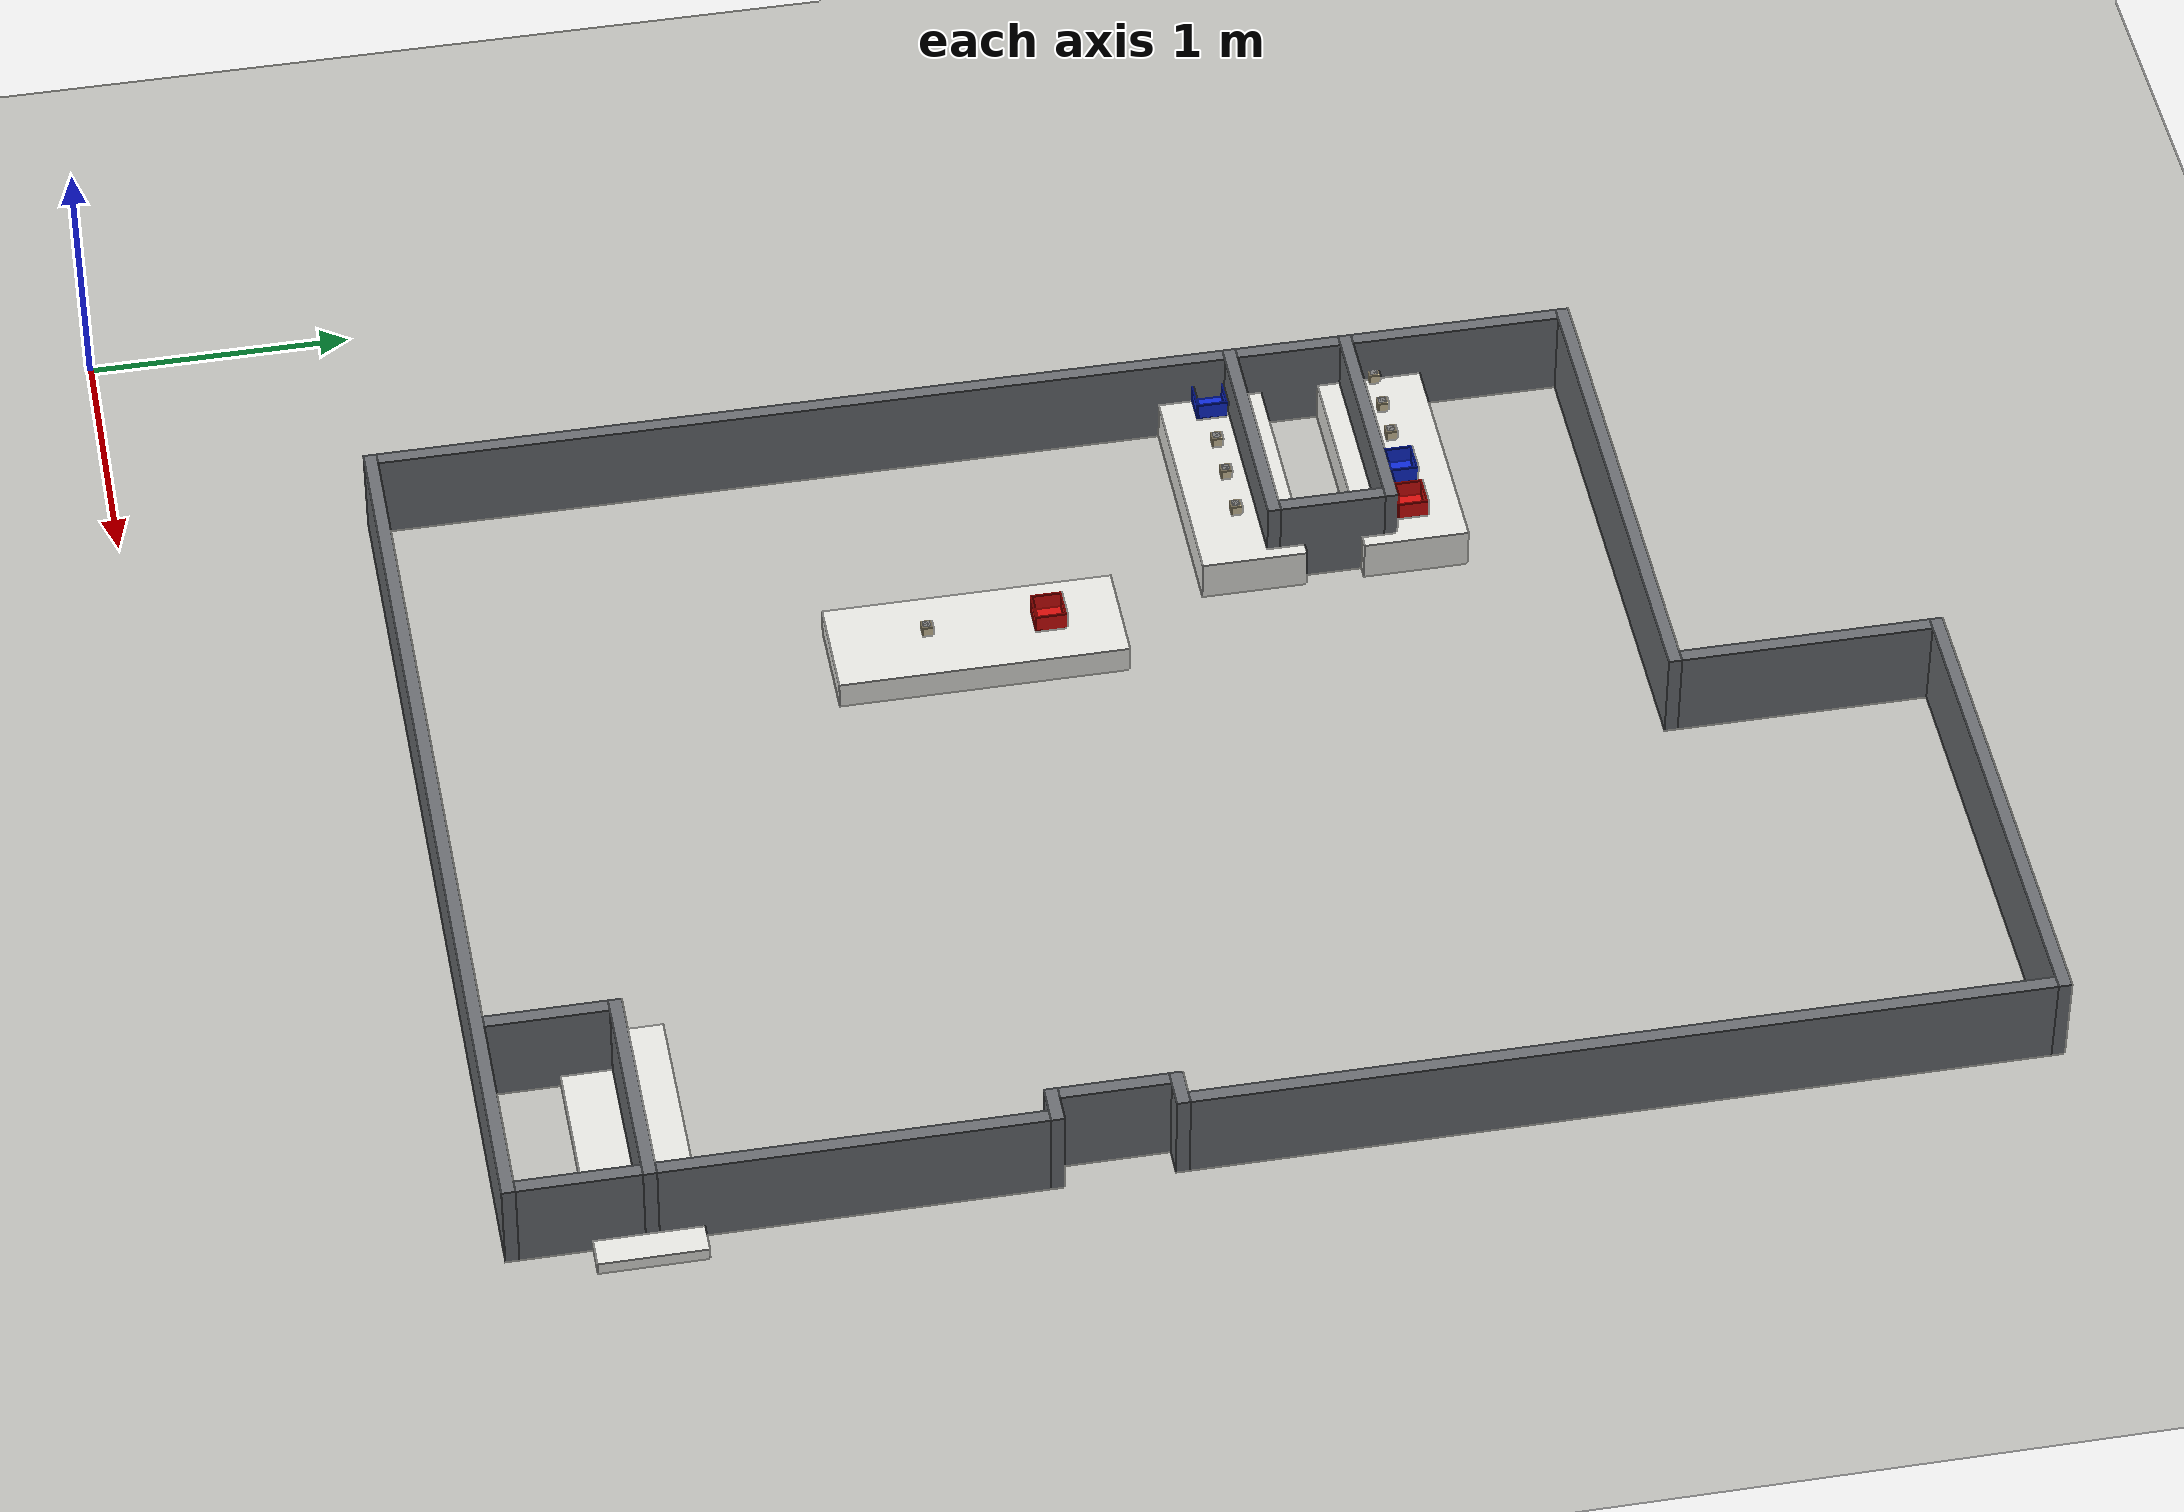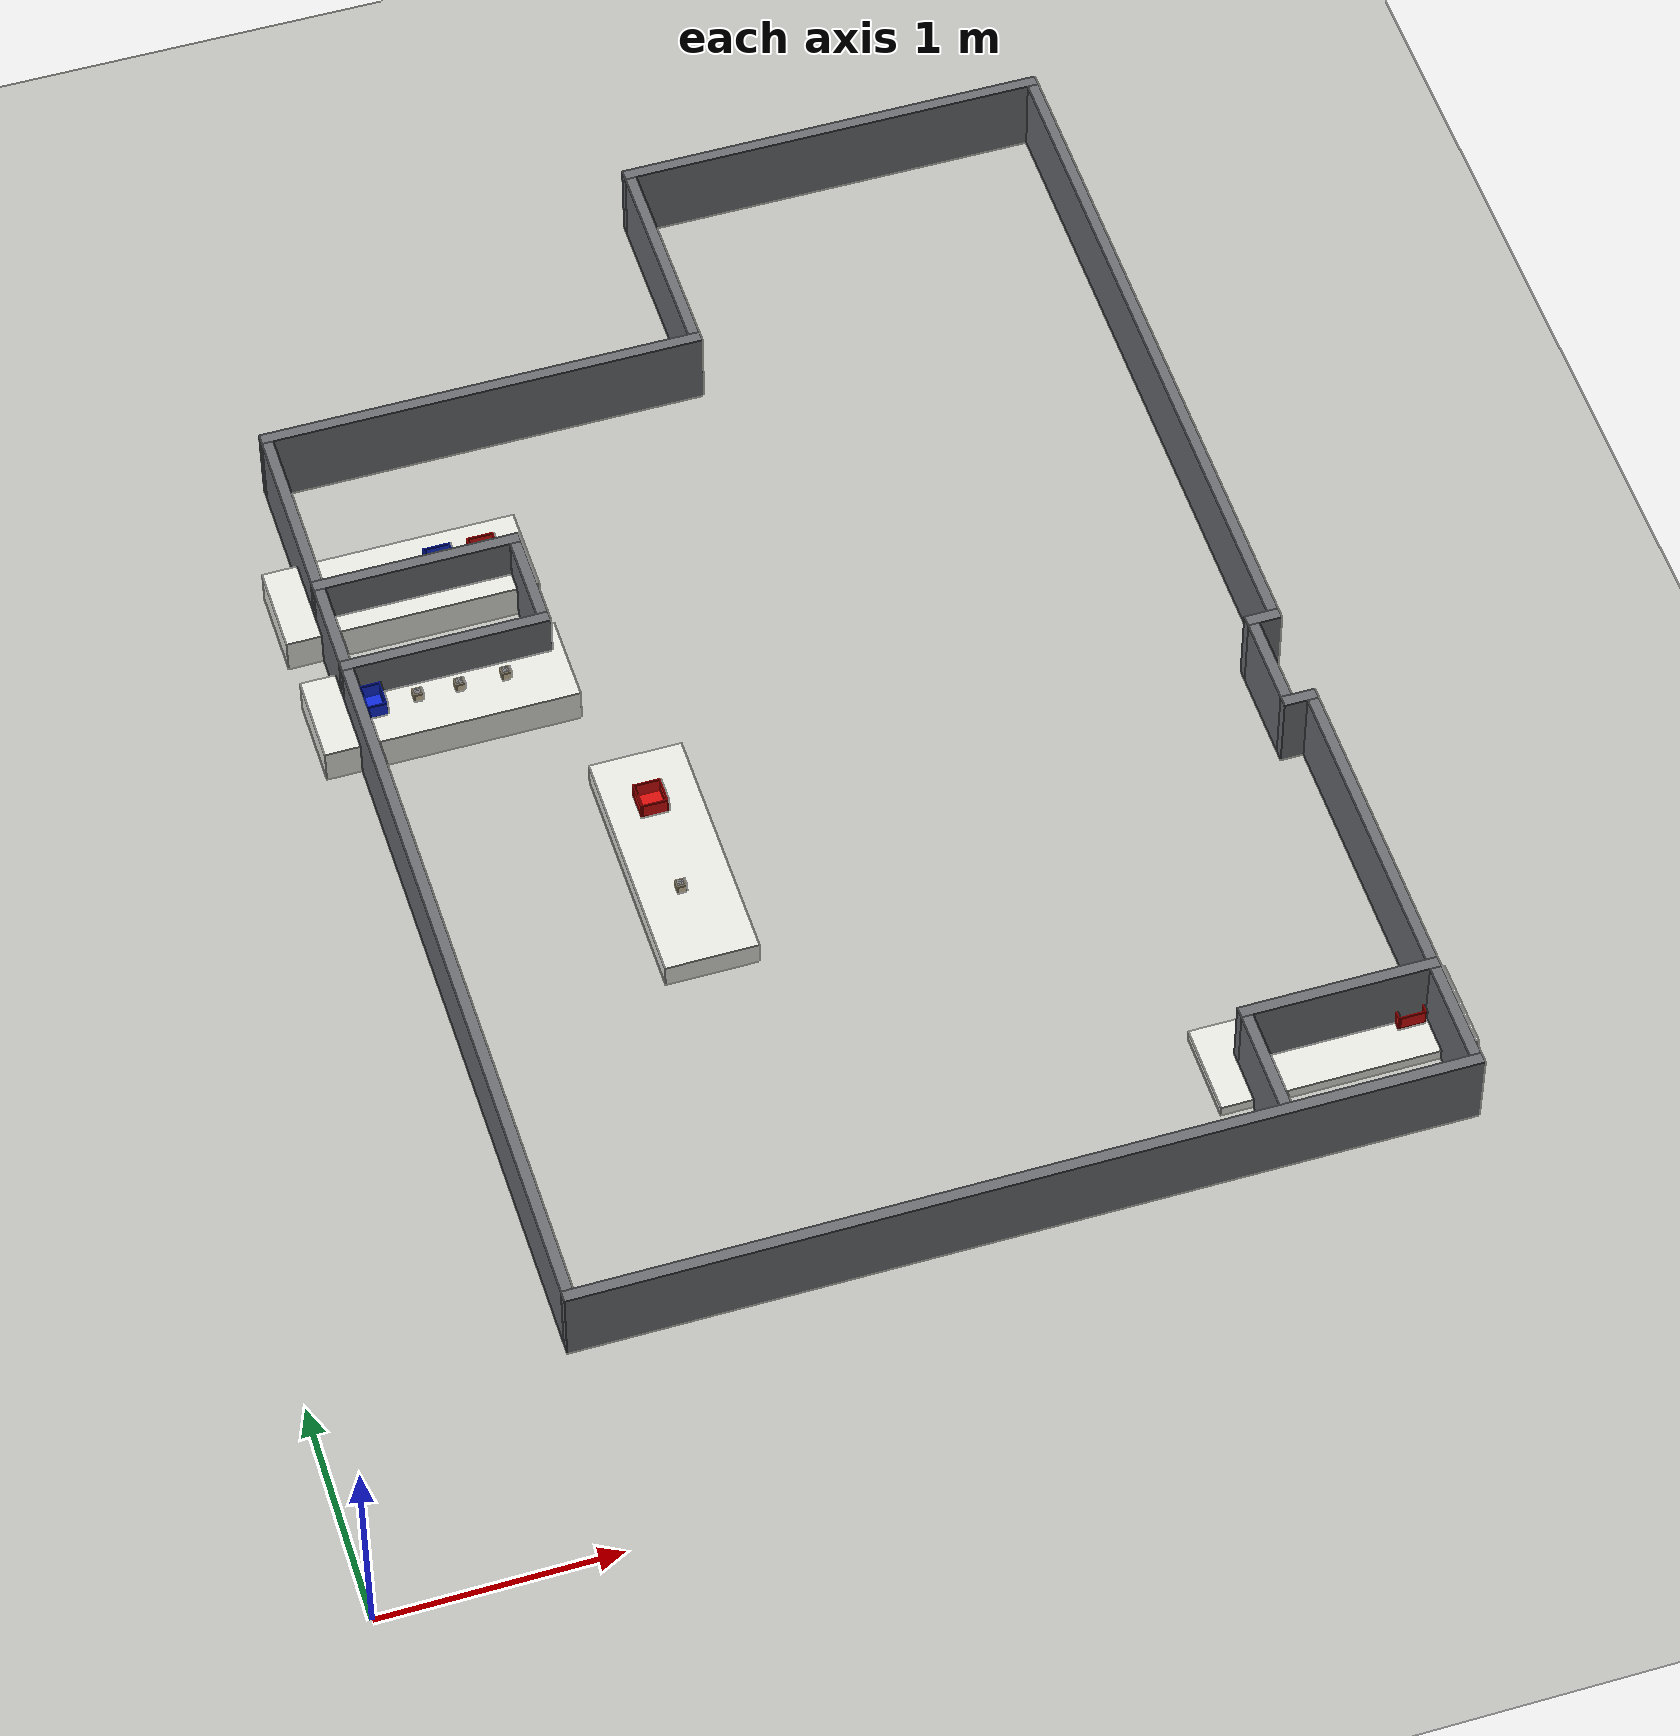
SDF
<?xml version="1.0"?>
<sdf version="1.9"><world name="arena">
  <physics name="physics" type="ignored"><max_step_size>0.004</max_step_size>
    <real_time_factor>1</real_time_factor></physics>
  <plugin filename="gz-sim-physics-system" name="gz::sim::systems::Physics"/>
  <plugin filename="gz-sim-user-commands-system" name="gz::sim::systems::UserCommands"/>
  <plugin filename="gz-sim-scene-broadcaster-system" name="gz::sim::systems::SceneBroadcaster"/>
  <plugin filename="gz-sim-sensors-system" name="gz::sim::systems::Sensors">
    <render_engine>ogre2</render_engine></plugin>
  <plugin filename="gz-sim-imu-system" name="gz::sim::systems::Imu"/>
  <gravity>0 0 -9.81</gravity>
  <light name="sun" type="directional"><pose>0 0 10 0 0 0</pose>
    <diffuse>0.85 0.85 0.85 1</diffuse><specular>0.1 0.1 0.1 1</specular>
    <direction>-0.4 0.2 -0.9</direction></light>
  <model name="floor"><static>true</static><link name="ground">
    <collision name="ground"><geometry><plane><normal>0 0 1</normal>
      <size>20 20</size></plane></geometry></collision>
    <visual name="floor_appearance"><geometry><plane><normal>0 0 1</normal>
      <size>20 20</size></plane></geometry>
      <material><ambient>0.75 0.75 0.73 1</ambient>
        <diffuse>0.75 0.75 0.73 1</diffuse></material></visual>
  </link></model>
<model name="map_wall_0">
      <static>true</static>
      <pose>3.88900 6.57000 0.18000 0 0 0.0000000</pose>
      <link name="body">
        <collision name="collision"><geometry><box><size>1.90000 0.05000 0.36000</size></box></geometry></collision>
        <visual name="appearance"><geometry><box><size>1.90000 0.05000 0.36000</size></box></geometry>
          <material><ambient>0.42 0.43 0.45 1</ambient><diffuse>0.42 0.43 0.45 1</diffuse></material></visual>
      </link>
    </model>
<model name="map_wall_1">
      <static>true</static>
      <pose>2.96400 6.07000 0.18000 0 0 0.0000000</pose>
      <link name="body">
        <collision name="collision"><geometry><box><size>0.05000 0.95000 0.36000</size></box></geometry></collision>
        <visual name="appearance"><geometry><box><size>0.05000 0.95000 0.36000</size></box></geometry>
          <material><ambient>0.42 0.43 0.45 1</ambient><diffuse>0.42 0.43 0.45 1</diffuse></material></visual>
      </link>
    </model>
<model name="map_wall_2">
      <static>true</static>
      <pose>2.01400 5.57000 0.18000 0 0 0.0000000</pose>
      <link name="body">
        <collision name="collision"><geometry><box><size>1.95000 0.05000 0.36000</size></box></geometry></collision>
        <visual name="appearance"><geometry><box><size>1.95000 0.05000 0.36000</size></box></geometry>
          <material><ambient>0.42 0.43 0.45 1</ambient><diffuse>0.42 0.43 0.45 1</diffuse></material></visual>
      </link>
    </model>
<model name="map_wall_3">
      <static>true</static>
      <pose>1.06400 5.14500 0.18000 0 0 0.0000000</pose>
      <link name="body">
        <collision name="collision"><geometry><box><size>0.05000 0.80000 0.36000</size></box></geometry></collision>
        <visual name="appearance"><geometry><box><size>0.05000 0.80000 0.36000</size></box></geometry>
          <material><ambient>0.42 0.43 0.45 1</ambient><diffuse>0.42 0.43 0.45 1</diffuse></material></visual>
      </link>
    </model>
<model name="map_wall_4">
      <static>true</static>
      <pose>1.48900 4.72000 0.18000 0 0 0.0000000</pose>
      <link name="body">
        <collision name="collision"><geometry><box><size>0.90000 0.05000 0.36000</size></box></geometry></collision>
        <visual name="appearance"><geometry><box><size>0.90000 0.05000 0.36000</size></box></geometry>
          <material><ambient>0.42 0.43 0.45 1</ambient><diffuse>0.42 0.43 0.45 1</diffuse></material></visual>
      </link>
    </model>
<model name="map_wall_5">
      <static>true</static>
      <pose>1.06400 4.49500 0.18000 0 0 0.0000000</pose>
      <link name="body">
        <collision name="collision"><geometry><box><size>0.05000 0.40000 0.36000</size></box></geometry></collision>
        <visual name="appearance"><geometry><box><size>0.05000 0.40000 0.36000</size></box></geometry>
          <material><ambient>0.42 0.43 0.45 1</ambient><diffuse>0.42 0.43 0.45 1</diffuse></material></visual>
      </link>
    </model>
<model name="map_wall_6">
      <static>true</static>
      <pose>1.91400 4.49500 0.18000 0 0 0.0000000</pose>
      <link name="body">
        <collision name="collision"><geometry><box><size>0.05000 0.40000 0.36000</size></box></geometry></collision>
        <visual name="appearance"><geometry><box><size>0.05000 0.40000 0.36000</size></box></geometry>
          <material><ambient>0.42 0.43 0.45 1</ambient><diffuse>0.42 0.43 0.45 1</diffuse></material></visual>
      </link>
    </model>
<model name="map_wall_7">
      <static>true</static>
      <pose>1.48900 4.27000 0.18000 0 0 0.0000000</pose>
      <link name="body">
        <collision name="collision"><geometry><box><size>0.90000 0.05000 0.36000</size></box></geometry></collision>
        <visual name="appearance"><geometry><box><size>0.90000 0.05000 0.36000</size></box></geometry>
          <material><ambient>0.42 0.43 0.45 1</ambient><diffuse>0.42 0.43 0.45 1</diffuse></material></visual>
      </link>
    </model>
<model name="map_wall_8">
      <static>true</static>
      <pose>4.81400 4.97000 0.18000 0 0 0.0000000</pose>
      <link name="body">
        <collision name="collision"><geometry><box><size>0.05000 3.15000 0.36000</size></box></geometry></collision>
        <visual name="appearance"><geometry><box><size>0.05000 3.15000 0.36000</size></box></geometry>
          <material><ambient>0.42 0.43 0.45 1</ambient><diffuse>0.42 0.43 0.45 1</diffuse></material></visual>
      </link>
    </model>
<model name="map_wall_9">
      <static>true</static>
      <pose>4.76400 3.37000 0.18000 0 0 0.0000000</pose>
      <link name="body">
        <collision name="collision"><geometry><box><size>0.15000 0.05000 0.36000</size></box></geometry></collision>
        <visual name="appearance"><geometry><box><size>0.15000 0.05000 0.36000</size></box></geometry>
          <material><ambient>0.42 0.43 0.45 1</ambient><diffuse>0.42 0.43 0.45 1</diffuse></material></visual>
      </link>
    </model>
<model name="map_wall_10">
      <static>true</static>
      <pose>4.71400 3.14500 0.18000 0 0 0.0000000</pose>
      <link name="body">
        <collision name="collision"><geometry><box><size>0.05000 0.40000 0.36000</size></box></geometry></collision>
        <visual name="appearance"><geometry><box><size>0.05000 0.40000 0.36000</size></box></geometry>
          <material><ambient>0.42 0.43 0.45 1</ambient><diffuse>0.42 0.43 0.45 1</diffuse></material></visual>
      </link>
    </model>
<model name="map_wall_11">
      <static>true</static>
      <pose>4.76400 2.92000 0.18000 0 0 0.0000000</pose>
      <link name="body">
        <collision name="collision"><geometry><box><size>0.15000 0.05000 0.36000</size></box></geometry></collision>
        <visual name="appearance"><geometry><box><size>0.15000 0.05000 0.36000</size></box></geometry>
          <material><ambient>0.42 0.43 0.45 1</ambient><diffuse>0.42 0.43 0.45 1</diffuse></material></visual>
      </link>
    </model>
<model name="map_wall_12">
      <static>true</static>
      <pose>4.81400 2.19500 0.18000 0 0 0.0000000</pose>
      <link name="body">
        <collision name="collision"><geometry><box><size>0.05000 1.40000 0.36000</size></box></geometry></collision>
        <visual name="appearance"><geometry><box><size>0.05000 1.40000 0.36000</size></box></geometry>
          <material><ambient>0.42 0.43 0.45 1</ambient><diffuse>0.42 0.43 0.45 1</diffuse></material></visual>
      </link>
    </model>
<model name="map_wall_13">
      <static>true</static>
      <pose>4.41400 1.47000 0.18000 0 0 0.0000000</pose>
      <link name="body">
        <collision name="collision"><geometry><box><size>0.85000 0.05000 0.36000</size></box></geometry></collision>
        <visual name="appearance"><geometry><box><size>0.85000 0.05000 0.36000</size></box></geometry>
          <material><ambient>0.42 0.43 0.45 1</ambient><diffuse>0.42 0.43 0.45 1</diffuse></material></visual>
      </link>
    </model>
<model name="map_wall_14">
      <static>true</static>
      <pose>1.06400 2.62000 0.18000 0 0 0.0000000</pose>
      <link name="body">
        <collision name="collision"><geometry><box><size>0.05000 3.25000 0.36000</size></box></geometry></collision>
        <visual name="appearance"><geometry><box><size>0.05000 3.25000 0.36000</size></box></geometry>
          <material><ambient>0.42 0.43 0.45 1</ambient><diffuse>0.42 0.43 0.45 1</diffuse></material></visual>
      </link>
    </model>
<model name="map_wall_15">
      <static>true</static>
      <pose>4.01400 1.22000 0.18000 0 0 0.0000000</pose>
      <link name="body">
        <collision name="collision"><geometry><box><size>0.05000 0.45000 0.36000</size></box></geometry></collision>
        <visual name="appearance"><geometry><box><size>0.05000 0.45000 0.36000</size></box></geometry>
          <material><ambient>0.42 0.43 0.45 1</ambient><diffuse>0.42 0.43 0.45 1</diffuse></material></visual>
      </link>
    </model>
<model name="map_wall_16">
      <static>true</static>
      <pose>4.81400 1.22000 0.18000 0 0 0.0000000</pose>
      <link name="body">
        <collision name="collision"><geometry><box><size>0.05000 0.45000 0.36000</size></box></geometry></collision>
        <visual name="appearance"><geometry><box><size>0.05000 0.45000 0.36000</size></box></geometry>
          <material><ambient>0.42 0.43 0.45 1</ambient><diffuse>0.42 0.43 0.45 1</diffuse></material></visual>
      </link>
    </model>
<model name="map_wall_17">
      <static>true</static>
      <pose>2.93900 0.97000 0.18000 0 0 0.0000000</pose>
      <link name="body">
        <collision name="collision"><geometry><box><size>3.80000 0.05000 0.36000</size></box></geometry></collision>
        <visual name="appearance"><geometry><box><size>3.80000 0.05000 0.36000</size></box></geometry>
          <material><ambient>0.42 0.43 0.45 1</ambient><diffuse>0.42 0.43 0.45 1</diffuse></material></visual>
      </link>
    </model>
<model name="ws_1_table">
      <static>true</static>
      <pose>4.40028 1.45700 0.02500 0 0 -1.5700000</pose>
      <link name="body">
        <collision name="collision"><geometry><box><size>0.40000 1.10000 0.05000</size></box></geometry></collision>
        <visual name="appearance"><geometry><box><size>0.40000 1.10000 0.05000</size></box></geometry>
          <material><ambient>0.91 0.91 0.89 1</ambient><diffuse>0.91 0.91 0.89 1</diffuse></material></visual>
      </link>
    </model>
<model name="cube_1">
      <pose>4.12026 1.47678 0.07000 0 0 0</pose>
      <link name="body">
        <inertial><mass>0.04</mass><inertia>
          <ixx>0.000010667</ixx><iyy>0.000010667</iyy><izz>0.000010667</izz>
          <ixy>0</ixy><ixz>0</ixz><iyz>0</iyz>
        </inertia></inertial>
        <collision name="cube"><geometry><box><size>0.04 0.04 0.04</size></box></geometry>
          <surface><friction><ode><mu>1.2</mu><mu2>1.2</mu2></ode></friction></surface>
        </collision>
        <visual name="cube_appearance"><geometry><box><size>0.04 0.04 0.04</size></box></geometry>
          <material><ambient>0.85 0.79 0.64 1</ambient><diffuse>0.85 0.79 0.64 1</diffuse></material>
        </visual>
        <visual name="tag_0_0">
          <pose>-0.0140 0.0140 0.0202 0 0 0</pose>
          <geometry><plane><normal>0 0 1</normal><size>0.004 0.004</size></plane></geometry>
          <material><ambient>0.01 0.01 0.01 1</ambient>
            <diffuse>0.01 0.01 0.01 1</diffuse></material>
        </visual><visual name="tag_0_1">
          <pose>-0.0100 0.0140 0.0202 0 0 0</pose>
          <geometry><plane><normal>0 0 1</normal><size>0.004 0.004</size></plane></geometry>
          <material><ambient>0.01 0.01 0.01 1</ambient>
            <diffuse>0.01 0.01 0.01 1</diffuse></material>
        </visual><visual name="tag_0_2">
          <pose>-0.0060 0.0140 0.0202 0 0 0</pose>
          <geometry><plane><normal>0 0 1</normal><size>0.004 0.004</size></plane></geometry>
          <material><ambient>0.01 0.01 0.01 1</ambient>
            <diffuse>0.01 0.01 0.01 1</diffuse></material>
        </visual><visual name="tag_0_3">
          <pose>-0.0020 0.0140 0.0202 0 0 0</pose>
          <geometry><plane><normal>0 0 1</normal><size>0.004 0.004</size></plane></geometry>
          <material><ambient>0.01 0.01 0.01 1</ambient>
            <diffuse>0.01 0.01 0.01 1</diffuse></material>
        </visual><visual name="tag_0_4">
          <pose>0.0020 0.0140 0.0202 0 0 0</pose>
          <geometry><plane><normal>0 0 1</normal><size>0.004 0.004</size></plane></geometry>
          <material><ambient>0.01 0.01 0.01 1</ambient>
            <diffuse>0.01 0.01 0.01 1</diffuse></material>
        </visual><visual name="tag_0_5">
          <pose>0.0060 0.0140 0.0202 0 0 0</pose>
          <geometry><plane><normal>0 0 1</normal><size>0.004 0.004</size></plane></geometry>
          <material><ambient>0.01 0.01 0.01 1</ambient>
            <diffuse>0.01 0.01 0.01 1</diffuse></material>
        </visual><visual name="tag_0_6">
          <pose>0.0100 0.0140 0.0202 0 0 0</pose>
          <geometry><plane><normal>0 0 1</normal><size>0.004 0.004</size></plane></geometry>
          <material><ambient>0.01 0.01 0.01 1</ambient>
            <diffuse>0.01 0.01 0.01 1</diffuse></material>
        </visual><visual name="tag_0_7">
          <pose>0.0140 0.0140 0.0202 0 0 0</pose>
          <geometry><plane><normal>0 0 1</normal><size>0.004 0.004</size></plane></geometry>
          <material><ambient>0.01 0.01 0.01 1</ambient>
            <diffuse>0.01 0.01 0.01 1</diffuse></material>
        </visual><visual name="tag_1_0">
          <pose>-0.0140 0.0100 0.0202 0 0 0</pose>
          <geometry><plane><normal>0 0 1</normal><size>0.004 0.004</size></plane></geometry>
          <material><ambient>0.01 0.01 0.01 1</ambient>
            <diffuse>0.01 0.01 0.01 1</diffuse></material>
        </visual><visual name="tag_1_1">
          <pose>-0.0100 0.0100 0.0202 0 0 0</pose>
          <geometry><plane><normal>0 0 1</normal><size>0.004 0.004</size></plane></geometry>
          <material><ambient>0.95 0.95 0.95 1</ambient>
            <diffuse>0.95 0.95 0.95 1</diffuse></material>
        </visual><visual name="tag_1_2">
          <pose>-0.0060 0.0100 0.0202 0 0 0</pose>
          <geometry><plane><normal>0 0 1</normal><size>0.004 0.004</size></plane></geometry>
          <material><ambient>0.01 0.01 0.01 1</ambient>
            <diffuse>0.01 0.01 0.01 1</diffuse></material>
        </visual><visual name="tag_1_3">
          <pose>-0.0020 0.0100 0.0202 0 0 0</pose>
          <geometry><plane><normal>0 0 1</normal><size>0.004 0.004</size></plane></geometry>
          <material><ambient>0.01 0.01 0.01 1</ambient>
            <diffuse>0.01 0.01 0.01 1</diffuse></material>
        </visual><visual name="tag_1_4">
          <pose>0.0020 0.0100 0.0202 0 0 0</pose>
          <geometry><plane><normal>0 0 1</normal><size>0.004 0.004</size></plane></geometry>
          <material><ambient>0.95 0.95 0.95 1</ambient>
            <diffuse>0.95 0.95 0.95 1</diffuse></material>
        </visual><visual name="tag_1_5">
          <pose>0.0060 0.0100 0.0202 0 0 0</pose>
          <geometry><plane><normal>0 0 1</normal><size>0.004 0.004</size></plane></geometry>
          <material><ambient>0.01 0.01 0.01 1</ambient>
            <diffuse>0.01 0.01 0.01 1</diffuse></material>
        </visual><visual name="tag_1_6">
          <pose>0.0100 0.0100 0.0202 0 0 0</pose>
          <geometry><plane><normal>0 0 1</normal><size>0.004 0.004</size></plane></geometry>
          <material><ambient>0.01 0.01 0.01 1</ambient>
            <diffuse>0.01 0.01 0.01 1</diffuse></material>
        </visual><visual name="tag_1_7">
          <pose>0.0140 0.0100 0.0202 0 0 0</pose>
          <geometry><plane><normal>0 0 1</normal><size>0.004 0.004</size></plane></geometry>
          <material><ambient>0.01 0.01 0.01 1</ambient>
            <diffuse>0.01 0.01 0.01 1</diffuse></material>
        </visual><visual name="tag_2_0">
          <pose>-0.0140 0.0060 0.0202 0 0 0</pose>
          <geometry><plane><normal>0 0 1</normal><size>0.004 0.004</size></plane></geometry>
          <material><ambient>0.01 0.01 0.01 1</ambient>
            <diffuse>0.01 0.01 0.01 1</diffuse></material>
        </visual><visual name="tag_2_1">
          <pose>-0.0100 0.0060 0.0202 0 0 0</pose>
          <geometry><plane><normal>0 0 1</normal><size>0.004 0.004</size></plane></geometry>
          <material><ambient>0.95 0.95 0.95 1</ambient>
            <diffuse>0.95 0.95 0.95 1</diffuse></material>
        </visual><visual name="tag_2_2">
          <pose>-0.0060 0.0060 0.0202 0 0 0</pose>
          <geometry><plane><normal>0 0 1</normal><size>0.004 0.004</size></plane></geometry>
          <material><ambient>0.01 0.01 0.01 1</ambient>
            <diffuse>0.01 0.01 0.01 1</diffuse></material>
        </visual><visual name="tag_2_3">
          <pose>-0.0020 0.0060 0.0202 0 0 0</pose>
          <geometry><plane><normal>0 0 1</normal><size>0.004 0.004</size></plane></geometry>
          <material><ambient>0.95 0.95 0.95 1</ambient>
            <diffuse>0.95 0.95 0.95 1</diffuse></material>
        </visual><visual name="tag_2_4">
          <pose>0.0020 0.0060 0.0202 0 0 0</pose>
          <geometry><plane><normal>0 0 1</normal><size>0.004 0.004</size></plane></geometry>
          <material><ambient>0.95 0.95 0.95 1</ambient>
            <diffuse>0.95 0.95 0.95 1</diffuse></material>
        </visual><visual name="tag_2_5">
          <pose>0.0060 0.0060 0.0202 0 0 0</pose>
          <geometry><plane><normal>0 0 1</normal><size>0.004 0.004</size></plane></geometry>
          <material><ambient>0.01 0.01 0.01 1</ambient>
            <diffuse>0.01 0.01 0.01 1</diffuse></material>
        </visual><visual name="tag_2_6">
          <pose>0.0100 0.0060 0.0202 0 0 0</pose>
          <geometry><plane><normal>0 0 1</normal><size>0.004 0.004</size></plane></geometry>
          <material><ambient>0.95 0.95 0.95 1</ambient>
            <diffuse>0.95 0.95 0.95 1</diffuse></material>
        </visual><visual name="tag_2_7">
          <pose>0.0140 0.0060 0.0202 0 0 0</pose>
          <geometry><plane><normal>0 0 1</normal><size>0.004 0.004</size></plane></geometry>
          <material><ambient>0.01 0.01 0.01 1</ambient>
            <diffuse>0.01 0.01 0.01 1</diffuse></material>
        </visual><visual name="tag_3_0">
          <pose>-0.0140 0.0020 0.0202 0 0 0</pose>
          <geometry><plane><normal>0 0 1</normal><size>0.004 0.004</size></plane></geometry>
          <material><ambient>0.01 0.01 0.01 1</ambient>
            <diffuse>0.01 0.01 0.01 1</diffuse></material>
        </visual><visual name="tag_3_1">
          <pose>-0.0100 0.0020 0.0202 0 0 0</pose>
          <geometry><plane><normal>0 0 1</normal><size>0.004 0.004</size></plane></geometry>
          <material><ambient>0.01 0.01 0.01 1</ambient>
            <diffuse>0.01 0.01 0.01 1</diffuse></material>
        </visual><visual name="tag_3_2">
          <pose>-0.0060 0.0020 0.0202 0 0 0</pose>
          <geometry><plane><normal>0 0 1</normal><size>0.004 0.004</size></plane></geometry>
          <material><ambient>0.01 0.01 0.01 1</ambient>
            <diffuse>0.01 0.01 0.01 1</diffuse></material>
        </visual><visual name="tag_3_3">
          <pose>-0.0020 0.0020 0.0202 0 0 0</pose>
          <geometry><plane><normal>0 0 1</normal><size>0.004 0.004</size></plane></geometry>
          <material><ambient>0.01 0.01 0.01 1</ambient>
            <diffuse>0.01 0.01 0.01 1</diffuse></material>
        </visual><visual name="tag_3_4">
          <pose>0.0020 0.0020 0.0202 0 0 0</pose>
          <geometry><plane><normal>0 0 1</normal><size>0.004 0.004</size></plane></geometry>
          <material><ambient>0.95 0.95 0.95 1</ambient>
            <diffuse>0.95 0.95 0.95 1</diffuse></material>
        </visual><visual name="tag_3_5">
          <pose>0.0060 0.0020 0.0202 0 0 0</pose>
          <geometry><plane><normal>0 0 1</normal><size>0.004 0.004</size></plane></geometry>
          <material><ambient>0.95 0.95 0.95 1</ambient>
            <diffuse>0.95 0.95 0.95 1</diffuse></material>
        </visual><visual name="tag_3_6">
          <pose>0.0100 0.0020 0.0202 0 0 0</pose>
          <geometry><plane><normal>0 0 1</normal><size>0.004 0.004</size></plane></geometry>
          <material><ambient>0.01 0.01 0.01 1</ambient>
            <diffuse>0.01 0.01 0.01 1</diffuse></material>
        </visual><visual name="tag_3_7">
          <pose>0.0140 0.0020 0.0202 0 0 0</pose>
          <geometry><plane><normal>0 0 1</normal><size>0.004 0.004</size></plane></geometry>
          <material><ambient>0.01 0.01 0.01 1</ambient>
            <diffuse>0.01 0.01 0.01 1</diffuse></material>
        </visual><visual name="tag_4_0">
          <pose>-0.0140 -0.0020 0.0202 0 0 0</pose>
          <geometry><plane><normal>0 0 1</normal><size>0.004 0.004</size></plane></geometry>
          <material><ambient>0.01 0.01 0.01 1</ambient>
            <diffuse>0.01 0.01 0.01 1</diffuse></material>
        </visual><visual name="tag_4_1">
          <pose>-0.0100 -0.0020 0.0202 0 0 0</pose>
          <geometry><plane><normal>0 0 1</normal><size>0.004 0.004</size></plane></geometry>
          <material><ambient>0.01 0.01 0.01 1</ambient>
            <diffuse>0.01 0.01 0.01 1</diffuse></material>
        </visual><visual name="tag_4_2">
          <pose>-0.0060 -0.0020 0.0202 0 0 0</pose>
          <geometry><plane><normal>0 0 1</normal><size>0.004 0.004</size></plane></geometry>
          <material><ambient>0.01 0.01 0.01 1</ambient>
            <diffuse>0.01 0.01 0.01 1</diffuse></material>
        </visual><visual name="tag_4_3">
          <pose>-0.0020 -0.0020 0.0202 0 0 0</pose>
          <geometry><plane><normal>0 0 1</normal><size>0.004 0.004</size></plane></geometry>
          <material><ambient>0.95 0.95 0.95 1</ambient>
            <diffuse>0.95 0.95 0.95 1</diffuse></material>
        </visual><visual name="tag_4_4">
          <pose>0.0020 -0.0020 0.0202 0 0 0</pose>
          <geometry><plane><normal>0 0 1</normal><size>0.004 0.004</size></plane></geometry>
          <material><ambient>0.95 0.95 0.95 1</ambient>
            <diffuse>0.95 0.95 0.95 1</diffuse></material>
        </visual><visual name="tag_4_5">
          <pose>0.0060 -0.0020 0.0202 0 0 0</pose>
          <geometry><plane><normal>0 0 1</normal><size>0.004 0.004</size></plane></geometry>
          <material><ambient>0.95 0.95 0.95 1</ambient>
            <diffuse>0.95 0.95 0.95 1</diffuse></material>
        </visual><visual name="tag_4_6">
          <pose>0.0100 -0.0020 0.0202 0 0 0</pose>
          <geometry><plane><normal>0 0 1</normal><size>0.004 0.004</size></plane></geometry>
          <material><ambient>0.95 0.95 0.95 1</ambient>
            <diffuse>0.95 0.95 0.95 1</diffuse></material>
        </visual><visual name="tag_4_7">
          <pose>0.0140 -0.0020 0.0202 0 0 0</pose>
          <geometry><plane><normal>0 0 1</normal><size>0.004 0.004</size></plane></geometry>
          <material><ambient>0.01 0.01 0.01 1</ambient>
            <diffuse>0.01 0.01 0.01 1</diffuse></material>
        </visual><visual name="tag_5_0">
          <pose>-0.0140 -0.0060 0.0202 0 0 0</pose>
          <geometry><plane><normal>0 0 1</normal><size>0.004 0.004</size></plane></geometry>
          <material><ambient>0.01 0.01 0.01 1</ambient>
            <diffuse>0.01 0.01 0.01 1</diffuse></material>
        </visual><visual name="tag_5_1">
          <pose>-0.0100 -0.0060 0.0202 0 0 0</pose>
          <geometry><plane><normal>0 0 1</normal><size>0.004 0.004</size></plane></geometry>
          <material><ambient>0.95 0.95 0.95 1</ambient>
            <diffuse>0.95 0.95 0.95 1</diffuse></material>
        </visual><visual name="tag_5_2">
          <pose>-0.0060 -0.0060 0.0202 0 0 0</pose>
          <geometry><plane><normal>0 0 1</normal><size>0.004 0.004</size></plane></geometry>
          <material><ambient>0.95 0.95 0.95 1</ambient>
            <diffuse>0.95 0.95 0.95 1</diffuse></material>
        </visual><visual name="tag_5_3">
          <pose>-0.0020 -0.0060 0.0202 0 0 0</pose>
          <geometry><plane><normal>0 0 1</normal><size>0.004 0.004</size></plane></geometry>
          <material><ambient>0.95 0.95 0.95 1</ambient>
            <diffuse>0.95 0.95 0.95 1</diffuse></material>
        </visual><visual name="tag_5_4">
          <pose>0.0020 -0.0060 0.0202 0 0 0</pose>
          <geometry><plane><normal>0 0 1</normal><size>0.004 0.004</size></plane></geometry>
          <material><ambient>0.01 0.01 0.01 1</ambient>
            <diffuse>0.01 0.01 0.01 1</diffuse></material>
        </visual><visual name="tag_5_5">
          <pose>0.0060 -0.0060 0.0202 0 0 0</pose>
          <geometry><plane><normal>0 0 1</normal><size>0.004 0.004</size></plane></geometry>
          <material><ambient>0.95 0.95 0.95 1</ambient>
            <diffuse>0.95 0.95 0.95 1</diffuse></material>
        </visual><visual name="tag_5_6">
          <pose>0.0100 -0.0060 0.0202 0 0 0</pose>
          <geometry><plane><normal>0 0 1</normal><size>0.004 0.004</size></plane></geometry>
          <material><ambient>0.01 0.01 0.01 1</ambient>
            <diffuse>0.01 0.01 0.01 1</diffuse></material>
        </visual><visual name="tag_5_7">
          <pose>0.0140 -0.0060 0.0202 0 0 0</pose>
          <geometry><plane><normal>0 0 1</normal><size>0.004 0.004</size></plane></geometry>
          <material><ambient>0.01 0.01 0.01 1</ambient>
            <diffuse>0.01 0.01 0.01 1</diffuse></material>
        </visual><visual name="tag_6_0">
          <pose>-0.0140 -0.0100 0.0202 0 0 0</pose>
          <geometry><plane><normal>0 0 1</normal><size>0.004 0.004</size></plane></geometry>
          <material><ambient>0.01 0.01 0.01 1</ambient>
            <diffuse>0.01 0.01 0.01 1</diffuse></material>
        </visual><visual name="tag_6_1">
          <pose>-0.0100 -0.0100 0.0202 0 0 0</pose>
          <geometry><plane><normal>0 0 1</normal><size>0.004 0.004</size></plane></geometry>
          <material><ambient>0.01 0.01 0.01 1</ambient>
            <diffuse>0.01 0.01 0.01 1</diffuse></material>
        </visual><visual name="tag_6_2">
          <pose>-0.0060 -0.0100 0.0202 0 0 0</pose>
          <geometry><plane><normal>0 0 1</normal><size>0.004 0.004</size></plane></geometry>
          <material><ambient>0.95 0.95 0.95 1</ambient>
            <diffuse>0.95 0.95 0.95 1</diffuse></material>
        </visual><visual name="tag_6_3">
          <pose>-0.0020 -0.0100 0.0202 0 0 0</pose>
          <geometry><plane><normal>0 0 1</normal><size>0.004 0.004</size></plane></geometry>
          <material><ambient>0.95 0.95 0.95 1</ambient>
            <diffuse>0.95 0.95 0.95 1</diffuse></material>
        </visual><visual name="tag_6_4">
          <pose>0.0020 -0.0100 0.0202 0 0 0</pose>
          <geometry><plane><normal>0 0 1</normal><size>0.004 0.004</size></plane></geometry>
          <material><ambient>0.01 0.01 0.01 1</ambient>
            <diffuse>0.01 0.01 0.01 1</diffuse></material>
        </visual><visual name="tag_6_5">
          <pose>0.0060 -0.0100 0.0202 0 0 0</pose>
          <geometry><plane><normal>0 0 1</normal><size>0.004 0.004</size></plane></geometry>
          <material><ambient>0.95 0.95 0.95 1</ambient>
            <diffuse>0.95 0.95 0.95 1</diffuse></material>
        </visual><visual name="tag_6_6">
          <pose>0.0100 -0.0100 0.0202 0 0 0</pose>
          <geometry><plane><normal>0 0 1</normal><size>0.004 0.004</size></plane></geometry>
          <material><ambient>0.95 0.95 0.95 1</ambient>
            <diffuse>0.95 0.95 0.95 1</diffuse></material>
        </visual><visual name="tag_6_7">
          <pose>0.0140 -0.0100 0.0202 0 0 0</pose>
          <geometry><plane><normal>0 0 1</normal><size>0.004 0.004</size></plane></geometry>
          <material><ambient>0.01 0.01 0.01 1</ambient>
            <diffuse>0.01 0.01 0.01 1</diffuse></material>
        </visual><visual name="tag_7_0">
          <pose>-0.0140 -0.0140 0.0202 0 0 0</pose>
          <geometry><plane><normal>0 0 1</normal><size>0.004 0.004</size></plane></geometry>
          <material><ambient>0.01 0.01 0.01 1</ambient>
            <diffuse>0.01 0.01 0.01 1</diffuse></material>
        </visual><visual name="tag_7_1">
          <pose>-0.0100 -0.0140 0.0202 0 0 0</pose>
          <geometry><plane><normal>0 0 1</normal><size>0.004 0.004</size></plane></geometry>
          <material><ambient>0.01 0.01 0.01 1</ambient>
            <diffuse>0.01 0.01 0.01 1</diffuse></material>
        </visual><visual name="tag_7_2">
          <pose>-0.0060 -0.0140 0.0202 0 0 0</pose>
          <geometry><plane><normal>0 0 1</normal><size>0.004 0.004</size></plane></geometry>
          <material><ambient>0.01 0.01 0.01 1</ambient>
            <diffuse>0.01 0.01 0.01 1</diffuse></material>
        </visual><visual name="tag_7_3">
          <pose>-0.0020 -0.0140 0.0202 0 0 0</pose>
          <geometry><plane><normal>0 0 1</normal><size>0.004 0.004</size></plane></geometry>
          <material><ambient>0.01 0.01 0.01 1</ambient>
            <diffuse>0.01 0.01 0.01 1</diffuse></material>
        </visual><visual name="tag_7_4">
          <pose>0.0020 -0.0140 0.0202 0 0 0</pose>
          <geometry><plane><normal>0 0 1</normal><size>0.004 0.004</size></plane></geometry>
          <material><ambient>0.01 0.01 0.01 1</ambient>
            <diffuse>0.01 0.01 0.01 1</diffuse></material>
        </visual><visual name="tag_7_5">
          <pose>0.0060 -0.0140 0.0202 0 0 0</pose>
          <geometry><plane><normal>0 0 1</normal><size>0.004 0.004</size></plane></geometry>
          <material><ambient>0.01 0.01 0.01 1</ambient>
            <diffuse>0.01 0.01 0.01 1</diffuse></material>
        </visual><visual name="tag_7_6">
          <pose>0.0100 -0.0140 0.0202 0 0 0</pose>
          <geometry><plane><normal>0 0 1</normal><size>0.004 0.004</size></plane></geometry>
          <material><ambient>0.01 0.01 0.01 1</ambient>
            <diffuse>0.01 0.01 0.01 1</diffuse></material>
        </visual><visual name="tag_7_7">
          <pose>0.0140 -0.0140 0.0202 0 0 0</pose>
          <geometry><plane><normal>0 0 1</normal><size>0.004 0.004</size></plane></geometry>
          <material><ambient>0.01 0.01 0.01 1</ambient>
            <diffuse>0.01 0.01 0.01 1</diffuse></material>
        </visual>
      </link>
    </model>
<model name="cube_2">
      <pose>4.30026 1.47692 0.07000 0 0 0</pose>
      <link name="body">
        <inertial><mass>0.04</mass><inertia>
          <ixx>0.000010667</ixx><iyy>0.000010667</iyy><izz>0.000010667</izz>
          <ixy>0</ixy><ixz>0</ixz><iyz>0</iyz>
        </inertia></inertial>
        <collision name="cube"><geometry><box><size>0.04 0.04 0.04</size></box></geometry>
          <surface><friction><ode><mu>1.2</mu><mu2>1.2</mu2></ode></friction></surface>
        </collision>
        <visual name="cube_appearance"><geometry><box><size>0.04 0.04 0.04</size></box></geometry>
          <material><ambient>0.85 0.79 0.64 1</ambient><diffuse>0.85 0.79 0.64 1</diffuse></material>
        </visual>
        <visual name="tag_0_0">
          <pose>-0.0140 0.0140 0.0202 0 0 0</pose>
          <geometry><plane><normal>0 0 1</normal><size>0.004 0.004</size></plane></geometry>
          <material><ambient>0.01 0.01 0.01 1</ambient>
            <diffuse>0.01 0.01 0.01 1</diffuse></material>
        </visual><visual name="tag_0_1">
          <pose>-0.0100 0.0140 0.0202 0 0 0</pose>
          <geometry><plane><normal>0 0 1</normal><size>0.004 0.004</size></plane></geometry>
          <material><ambient>0.01 0.01 0.01 1</ambient>
            <diffuse>0.01 0.01 0.01 1</diffuse></material>
        </visual><visual name="tag_0_2">
          <pose>-0.0060 0.0140 0.0202 0 0 0</pose>
          <geometry><plane><normal>0 0 1</normal><size>0.004 0.004</size></plane></geometry>
          <material><ambient>0.01 0.01 0.01 1</ambient>
            <diffuse>0.01 0.01 0.01 1</diffuse></material>
        </visual><visual name="tag_0_3">
          <pose>-0.0020 0.0140 0.0202 0 0 0</pose>
          <geometry><plane><normal>0 0 1</normal><size>0.004 0.004</size></plane></geometry>
          <material><ambient>0.01 0.01 0.01 1</ambient>
            <diffuse>0.01 0.01 0.01 1</diffuse></material>
        </visual><visual name="tag_0_4">
          <pose>0.0020 0.0140 0.0202 0 0 0</pose>
          <geometry><plane><normal>0 0 1</normal><size>0.004 0.004</size></plane></geometry>
          <material><ambient>0.01 0.01 0.01 1</ambient>
            <diffuse>0.01 0.01 0.01 1</diffuse></material>
        </visual><visual name="tag_0_5">
          <pose>0.0060 0.0140 0.0202 0 0 0</pose>
          <geometry><plane><normal>0 0 1</normal><size>0.004 0.004</size></plane></geometry>
          <material><ambient>0.01 0.01 0.01 1</ambient>
            <diffuse>0.01 0.01 0.01 1</diffuse></material>
        </visual><visual name="tag_0_6">
          <pose>0.0100 0.0140 0.0202 0 0 0</pose>
          <geometry><plane><normal>0 0 1</normal><size>0.004 0.004</size></plane></geometry>
          <material><ambient>0.01 0.01 0.01 1</ambient>
            <diffuse>0.01 0.01 0.01 1</diffuse></material>
        </visual><visual name="tag_0_7">
          <pose>0.0140 0.0140 0.0202 0 0 0</pose>
          <geometry><plane><normal>0 0 1</normal><size>0.004 0.004</size></plane></geometry>
          <material><ambient>0.01 0.01 0.01 1</ambient>
            <diffuse>0.01 0.01 0.01 1</diffuse></material>
        </visual><visual name="tag_1_0">
          <pose>-0.0140 0.0100 0.0202 0 0 0</pose>
          <geometry><plane><normal>0 0 1</normal><size>0.004 0.004</size></plane></geometry>
          <material><ambient>0.01 0.01 0.01 1</ambient>
            <diffuse>0.01 0.01 0.01 1</diffuse></material>
        </visual><visual name="tag_1_1">
          <pose>-0.0100 0.0100 0.0202 0 0 0</pose>
          <geometry><plane><normal>0 0 1</normal><size>0.004 0.004</size></plane></geometry>
          <material><ambient>0.01 0.01 0.01 1</ambient>
            <diffuse>0.01 0.01 0.01 1</diffuse></material>
        </visual><visual name="tag_1_2">
          <pose>-0.0060 0.0100 0.0202 0 0 0</pose>
          <geometry><plane><normal>0 0 1</normal><size>0.004 0.004</size></plane></geometry>
          <material><ambient>0.95 0.95 0.95 1</ambient>
            <diffuse>0.95 0.95 0.95 1</diffuse></material>
        </visual><visual name="tag_1_3">
          <pose>-0.0020 0.0100 0.0202 0 0 0</pose>
          <geometry><plane><normal>0 0 1</normal><size>0.004 0.004</size></plane></geometry>
          <material><ambient>0.95 0.95 0.95 1</ambient>
            <diffuse>0.95 0.95 0.95 1</diffuse></material>
        </visual><visual name="tag_1_4">
          <pose>0.0020 0.0100 0.0202 0 0 0</pose>
          <geometry><plane><normal>0 0 1</normal><size>0.004 0.004</size></plane></geometry>
          <material><ambient>0.95 0.95 0.95 1</ambient>
            <diffuse>0.95 0.95 0.95 1</diffuse></material>
        </visual><visual name="tag_1_5">
          <pose>0.0060 0.0100 0.0202 0 0 0</pose>
          <geometry><plane><normal>0 0 1</normal><size>0.004 0.004</size></plane></geometry>
          <material><ambient>0.01 0.01 0.01 1</ambient>
            <diffuse>0.01 0.01 0.01 1</diffuse></material>
        </visual><visual name="tag_1_6">
          <pose>0.0100 0.0100 0.0202 0 0 0</pose>
          <geometry><plane><normal>0 0 1</normal><size>0.004 0.004</size></plane></geometry>
          <material><ambient>0.01 0.01 0.01 1</ambient>
            <diffuse>0.01 0.01 0.01 1</diffuse></material>
        </visual><visual name="tag_1_7">
          <pose>0.0140 0.0100 0.0202 0 0 0</pose>
          <geometry><plane><normal>0 0 1</normal><size>0.004 0.004</size></plane></geometry>
          <material><ambient>0.01 0.01 0.01 1</ambient>
            <diffuse>0.01 0.01 0.01 1</diffuse></material>
        </visual><visual name="tag_2_0">
          <pose>-0.0140 0.0060 0.0202 0 0 0</pose>
          <geometry><plane><normal>0 0 1</normal><size>0.004 0.004</size></plane></geometry>
          <material><ambient>0.01 0.01 0.01 1</ambient>
            <diffuse>0.01 0.01 0.01 1</diffuse></material>
        </visual><visual name="tag_2_1">
          <pose>-0.0100 0.0060 0.0202 0 0 0</pose>
          <geometry><plane><normal>0 0 1</normal><size>0.004 0.004</size></plane></geometry>
          <material><ambient>0.01 0.01 0.01 1</ambient>
            <diffuse>0.01 0.01 0.01 1</diffuse></material>
        </visual><visual name="tag_2_2">
          <pose>-0.0060 0.0060 0.0202 0 0 0</pose>
          <geometry><plane><normal>0 0 1</normal><size>0.004 0.004</size></plane></geometry>
          <material><ambient>0.01 0.01 0.01 1</ambient>
            <diffuse>0.01 0.01 0.01 1</diffuse></material>
        </visual><visual name="tag_2_3">
          <pose>-0.0020 0.0060 0.0202 0 0 0</pose>
          <geometry><plane><normal>0 0 1</normal><size>0.004 0.004</size></plane></geometry>
          <material><ambient>0.95 0.95 0.95 1</ambient>
            <diffuse>0.95 0.95 0.95 1</diffuse></material>
        </visual><visual name="tag_2_4">
          <pose>0.0020 0.0060 0.0202 0 0 0</pose>
          <geometry><plane><normal>0 0 1</normal><size>0.004 0.004</size></plane></geometry>
          <material><ambient>0.01 0.01 0.01 1</ambient>
            <diffuse>0.01 0.01 0.01 1</diffuse></material>
        </visual><visual name="tag_2_5">
          <pose>0.0060 0.0060 0.0202 0 0 0</pose>
          <geometry><plane><normal>0 0 1</normal><size>0.004 0.004</size></plane></geometry>
          <material><ambient>0.01 0.01 0.01 1</ambient>
            <diffuse>0.01 0.01 0.01 1</diffuse></material>
        </visual><visual name="tag_2_6">
          <pose>0.0100 0.0060 0.0202 0 0 0</pose>
          <geometry><plane><normal>0 0 1</normal><size>0.004 0.004</size></plane></geometry>
          <material><ambient>0.01 0.01 0.01 1</ambient>
            <diffuse>0.01 0.01 0.01 1</diffuse></material>
        </visual><visual name="tag_2_7">
          <pose>0.0140 0.0060 0.0202 0 0 0</pose>
          <geometry><plane><normal>0 0 1</normal><size>0.004 0.004</size></plane></geometry>
          <material><ambient>0.01 0.01 0.01 1</ambient>
            <diffuse>0.01 0.01 0.01 1</diffuse></material>
        </visual><visual name="tag_3_0">
          <pose>-0.0140 0.0020 0.0202 0 0 0</pose>
          <geometry><plane><normal>0 0 1</normal><size>0.004 0.004</size></plane></geometry>
          <material><ambient>0.01 0.01 0.01 1</ambient>
            <diffuse>0.01 0.01 0.01 1</diffuse></material>
        </visual><visual name="tag_3_1">
          <pose>-0.0100 0.0020 0.0202 0 0 0</pose>
          <geometry><plane><normal>0 0 1</normal><size>0.004 0.004</size></plane></geometry>
          <material><ambient>0.95 0.95 0.95 1</ambient>
            <diffuse>0.95 0.95 0.95 1</diffuse></material>
        </visual><visual name="tag_3_2">
          <pose>-0.0060 0.0020 0.0202 0 0 0</pose>
          <geometry><plane><normal>0 0 1</normal><size>0.004 0.004</size></plane></geometry>
          <material><ambient>0.01 0.01 0.01 1</ambient>
            <diffuse>0.01 0.01 0.01 1</diffuse></material>
        </visual><visual name="tag_3_3">
          <pose>-0.0020 0.0020 0.0202 0 0 0</pose>
          <geometry><plane><normal>0 0 1</normal><size>0.004 0.004</size></plane></geometry>
          <material><ambient>0.01 0.01 0.01 1</ambient>
            <diffuse>0.01 0.01 0.01 1</diffuse></material>
        </visual><visual name="tag_3_4">
          <pose>0.0020 0.0020 0.0202 0 0 0</pose>
          <geometry><plane><normal>0 0 1</normal><size>0.004 0.004</size></plane></geometry>
          <material><ambient>0.95 0.95 0.95 1</ambient>
            <diffuse>0.95 0.95 0.95 1</diffuse></material>
        </visual><visual name="tag_3_5">
          <pose>0.0060 0.0020 0.0202 0 0 0</pose>
          <geometry><plane><normal>0 0 1</normal><size>0.004 0.004</size></plane></geometry>
          <material><ambient>0.01 0.01 0.01 1</ambient>
            <diffuse>0.01 0.01 0.01 1</diffuse></material>
        </visual><visual name="tag_3_6">
          <pose>0.0100 0.0020 0.0202 0 0 0</pose>
          <geometry><plane><normal>0 0 1</normal><size>0.004 0.004</size></plane></geometry>
          <material><ambient>0.01 0.01 0.01 1</ambient>
            <diffuse>0.01 0.01 0.01 1</diffuse></material>
        </visual><visual name="tag_3_7">
          <pose>0.0140 0.0020 0.0202 0 0 0</pose>
          <geometry><plane><normal>0 0 1</normal><size>0.004 0.004</size></plane></geometry>
          <material><ambient>0.01 0.01 0.01 1</ambient>
            <diffuse>0.01 0.01 0.01 1</diffuse></material>
        </visual><visual name="tag_4_0">
          <pose>-0.0140 -0.0020 0.0202 0 0 0</pose>
          <geometry><plane><normal>0 0 1</normal><size>0.004 0.004</size></plane></geometry>
          <material><ambient>0.01 0.01 0.01 1</ambient>
            <diffuse>0.01 0.01 0.01 1</diffuse></material>
        </visual><visual name="tag_4_1">
          <pose>-0.0100 -0.0020 0.0202 0 0 0</pose>
          <geometry><plane><normal>0 0 1</normal><size>0.004 0.004</size></plane></geometry>
          <material><ambient>0.01 0.01 0.01 1</ambient>
            <diffuse>0.01 0.01 0.01 1</diffuse></material>
        </visual><visual name="tag_4_2">
          <pose>-0.0060 -0.0020 0.0202 0 0 0</pose>
          <geometry><plane><normal>0 0 1</normal><size>0.004 0.004</size></plane></geometry>
          <material><ambient>0.01 0.01 0.01 1</ambient>
            <diffuse>0.01 0.01 0.01 1</diffuse></material>
        </visual><visual name="tag_4_3">
          <pose>-0.0020 -0.0020 0.0202 0 0 0</pose>
          <geometry><plane><normal>0 0 1</normal><size>0.004 0.004</size></plane></geometry>
          <material><ambient>0.01 0.01 0.01 1</ambient>
            <diffuse>0.01 0.01 0.01 1</diffuse></material>
        </visual><visual name="tag_4_4">
          <pose>0.0020 -0.0020 0.0202 0 0 0</pose>
          <geometry><plane><normal>0 0 1</normal><size>0.004 0.004</size></plane></geometry>
          <material><ambient>0.01 0.01 0.01 1</ambient>
            <diffuse>0.01 0.01 0.01 1</diffuse></material>
        </visual><visual name="tag_4_5">
          <pose>0.0060 -0.0020 0.0202 0 0 0</pose>
          <geometry><plane><normal>0 0 1</normal><size>0.004 0.004</size></plane></geometry>
          <material><ambient>0.01 0.01 0.01 1</ambient>
            <diffuse>0.01 0.01 0.01 1</diffuse></material>
        </visual><visual name="tag_4_6">
          <pose>0.0100 -0.0020 0.0202 0 0 0</pose>
          <geometry><plane><normal>0 0 1</normal><size>0.004 0.004</size></plane></geometry>
          <material><ambient>0.95 0.95 0.95 1</ambient>
            <diffuse>0.95 0.95 0.95 1</diffuse></material>
        </visual><visual name="tag_4_7">
          <pose>0.0140 -0.0020 0.0202 0 0 0</pose>
          <geometry><plane><normal>0 0 1</normal><size>0.004 0.004</size></plane></geometry>
          <material><ambient>0.01 0.01 0.01 1</ambient>
            <diffuse>0.01 0.01 0.01 1</diffuse></material>
        </visual><visual name="tag_5_0">
          <pose>-0.0140 -0.0060 0.0202 0 0 0</pose>
          <geometry><plane><normal>0 0 1</normal><size>0.004 0.004</size></plane></geometry>
          <material><ambient>0.01 0.01 0.01 1</ambient>
            <diffuse>0.01 0.01 0.01 1</diffuse></material>
        </visual><visual name="tag_5_1">
          <pose>-0.0100 -0.0060 0.0202 0 0 0</pose>
          <geometry><plane><normal>0 0 1</normal><size>0.004 0.004</size></plane></geometry>
          <material><ambient>0.01 0.01 0.01 1</ambient>
            <diffuse>0.01 0.01 0.01 1</diffuse></material>
        </visual><visual name="tag_5_2">
          <pose>-0.0060 -0.0060 0.0202 0 0 0</pose>
          <geometry><plane><normal>0 0 1</normal><size>0.004 0.004</size></plane></geometry>
          <material><ambient>0.95 0.95 0.95 1</ambient>
            <diffuse>0.95 0.95 0.95 1</diffuse></material>
        </visual><visual name="tag_5_3">
          <pose>-0.0020 -0.0060 0.0202 0 0 0</pose>
          <geometry><plane><normal>0 0 1</normal><size>0.004 0.004</size></plane></geometry>
          <material><ambient>0.01 0.01 0.01 1</ambient>
            <diffuse>0.01 0.01 0.01 1</diffuse></material>
        </visual><visual name="tag_5_4">
          <pose>0.0020 -0.0060 0.0202 0 0 0</pose>
          <geometry><plane><normal>0 0 1</normal><size>0.004 0.004</size></plane></geometry>
          <material><ambient>0.01 0.01 0.01 1</ambient>
            <diffuse>0.01 0.01 0.01 1</diffuse></material>
        </visual><visual name="tag_5_5">
          <pose>0.0060 -0.0060 0.0202 0 0 0</pose>
          <geometry><plane><normal>0 0 1</normal><size>0.004 0.004</size></plane></geometry>
          <material><ambient>0.95 0.95 0.95 1</ambient>
            <diffuse>0.95 0.95 0.95 1</diffuse></material>
        </visual><visual name="tag_5_6">
          <pose>0.0100 -0.0060 0.0202 0 0 0</pose>
          <geometry><plane><normal>0 0 1</normal><size>0.004 0.004</size></plane></geometry>
          <material><ambient>0.01 0.01 0.01 1</ambient>
            <diffuse>0.01 0.01 0.01 1</diffuse></material>
        </visual><visual name="tag_5_7">
          <pose>0.0140 -0.0060 0.0202 0 0 0</pose>
          <geometry><plane><normal>0 0 1</normal><size>0.004 0.004</size></plane></geometry>
          <material><ambient>0.01 0.01 0.01 1</ambient>
            <diffuse>0.01 0.01 0.01 1</diffuse></material>
        </visual><visual name="tag_6_0">
          <pose>-0.0140 -0.0100 0.0202 0 0 0</pose>
          <geometry><plane><normal>0 0 1</normal><size>0.004 0.004</size></plane></geometry>
          <material><ambient>0.01 0.01 0.01 1</ambient>
            <diffuse>0.01 0.01 0.01 1</diffuse></material>
        </visual><visual name="tag_6_1">
          <pose>-0.0100 -0.0100 0.0202 0 0 0</pose>
          <geometry><plane><normal>0 0 1</normal><size>0.004 0.004</size></plane></geometry>
          <material><ambient>0.95 0.95 0.95 1</ambient>
            <diffuse>0.95 0.95 0.95 1</diffuse></material>
        </visual><visual name="tag_6_2">
          <pose>-0.0060 -0.0100 0.0202 0 0 0</pose>
          <geometry><plane><normal>0 0 1</normal><size>0.004 0.004</size></plane></geometry>
          <material><ambient>0.95 0.95 0.95 1</ambient>
            <diffuse>0.95 0.95 0.95 1</diffuse></material>
        </visual><visual name="tag_6_3">
          <pose>-0.0020 -0.0100 0.0202 0 0 0</pose>
          <geometry><plane><normal>0 0 1</normal><size>0.004 0.004</size></plane></geometry>
          <material><ambient>0.95 0.95 0.95 1</ambient>
            <diffuse>0.95 0.95 0.95 1</diffuse></material>
        </visual><visual name="tag_6_4">
          <pose>0.0020 -0.0100 0.0202 0 0 0</pose>
          <geometry><plane><normal>0 0 1</normal><size>0.004 0.004</size></plane></geometry>
          <material><ambient>0.01 0.01 0.01 1</ambient>
            <diffuse>0.01 0.01 0.01 1</diffuse></material>
        </visual><visual name="tag_6_5">
          <pose>0.0060 -0.0100 0.0202 0 0 0</pose>
          <geometry><plane><normal>0 0 1</normal><size>0.004 0.004</size></plane></geometry>
          <material><ambient>0.95 0.95 0.95 1</ambient>
            <diffuse>0.95 0.95 0.95 1</diffuse></material>
        </visual><visual name="tag_6_6">
          <pose>0.0100 -0.0100 0.0202 0 0 0</pose>
          <geometry><plane><normal>0 0 1</normal><size>0.004 0.004</size></plane></geometry>
          <material><ambient>0.95 0.95 0.95 1</ambient>
            <diffuse>0.95 0.95 0.95 1</diffuse></material>
        </visual><visual name="tag_6_7">
          <pose>0.0140 -0.0100 0.0202 0 0 0</pose>
          <geometry><plane><normal>0 0 1</normal><size>0.004 0.004</size></plane></geometry>
          <material><ambient>0.01 0.01 0.01 1</ambient>
            <diffuse>0.01 0.01 0.01 1</diffuse></material>
        </visual><visual name="tag_7_0">
          <pose>-0.0140 -0.0140 0.0202 0 0 0</pose>
          <geometry><plane><normal>0 0 1</normal><size>0.004 0.004</size></plane></geometry>
          <material><ambient>0.01 0.01 0.01 1</ambient>
            <diffuse>0.01 0.01 0.01 1</diffuse></material>
        </visual><visual name="tag_7_1">
          <pose>-0.0100 -0.0140 0.0202 0 0 0</pose>
          <geometry><plane><normal>0 0 1</normal><size>0.004 0.004</size></plane></geometry>
          <material><ambient>0.01 0.01 0.01 1</ambient>
            <diffuse>0.01 0.01 0.01 1</diffuse></material>
        </visual><visual name="tag_7_2">
          <pose>-0.0060 -0.0140 0.0202 0 0 0</pose>
          <geometry><plane><normal>0 0 1</normal><size>0.004 0.004</size></plane></geometry>
          <material><ambient>0.01 0.01 0.01 1</ambient>
            <diffuse>0.01 0.01 0.01 1</diffuse></material>
        </visual><visual name="tag_7_3">
          <pose>-0.0020 -0.0140 0.0202 0 0 0</pose>
          <geometry><plane><normal>0 0 1</normal><size>0.004 0.004</size></plane></geometry>
          <material><ambient>0.01 0.01 0.01 1</ambient>
            <diffuse>0.01 0.01 0.01 1</diffuse></material>
        </visual><visual name="tag_7_4">
          <pose>0.0020 -0.0140 0.0202 0 0 0</pose>
          <geometry><plane><normal>0 0 1</normal><size>0.004 0.004</size></plane></geometry>
          <material><ambient>0.01 0.01 0.01 1</ambient>
            <diffuse>0.01 0.01 0.01 1</diffuse></material>
        </visual><visual name="tag_7_5">
          <pose>0.0060 -0.0140 0.0202 0 0 0</pose>
          <geometry><plane><normal>0 0 1</normal><size>0.004 0.004</size></plane></geometry>
          <material><ambient>0.01 0.01 0.01 1</ambient>
            <diffuse>0.01 0.01 0.01 1</diffuse></material>
        </visual><visual name="tag_7_6">
          <pose>0.0100 -0.0140 0.0202 0 0 0</pose>
          <geometry><plane><normal>0 0 1</normal><size>0.004 0.004</size></plane></geometry>
          <material><ambient>0.01 0.01 0.01 1</ambient>
            <diffuse>0.01 0.01 0.01 1</diffuse></material>
        </visual><visual name="tag_7_7">
          <pose>0.0140 -0.0140 0.0202 0 0 0</pose>
          <geometry><plane><normal>0 0 1</normal><size>0.004 0.004</size></plane></geometry>
          <material><ambient>0.01 0.01 0.01 1</ambient>
            <diffuse>0.01 0.01 0.01 1</diffuse></material>
        </visual>
      </link>
    </model>
<model name="cube_10">
      <pose>4.50026 1.47708 0.07000 0 0 0</pose>
      <link name="body">
        <inertial><mass>0.04</mass><inertia>
          <ixx>0.000010667</ixx><iyy>0.000010667</iyy><izz>0.000010667</izz>
          <ixy>0</ixy><ixz>0</ixz><iyz>0</iyz>
        </inertia></inertial>
        <collision name="cube"><geometry><box><size>0.04 0.04 0.04</size></box></geometry>
          <surface><friction><ode><mu>1.2</mu><mu2>1.2</mu2></ode></friction></surface>
        </collision>
        <visual name="cube_appearance"><geometry><box><size>0.04 0.04 0.04</size></box></geometry>
          <material><ambient>0.85 0.79 0.64 1</ambient><diffuse>0.85 0.79 0.64 1</diffuse></material>
        </visual>
        <visual name="tag_0_0">
          <pose>-0.0140 0.0140 0.0202 0 0 0</pose>
          <geometry><plane><normal>0 0 1</normal><size>0.004 0.004</size></plane></geometry>
          <material><ambient>0.01 0.01 0.01 1</ambient>
            <diffuse>0.01 0.01 0.01 1</diffuse></material>
        </visual><visual name="tag_0_1">
          <pose>-0.0100 0.0140 0.0202 0 0 0</pose>
          <geometry><plane><normal>0 0 1</normal><size>0.004 0.004</size></plane></geometry>
          <material><ambient>0.01 0.01 0.01 1</ambient>
            <diffuse>0.01 0.01 0.01 1</diffuse></material>
        </visual><visual name="tag_0_2">
          <pose>-0.0060 0.0140 0.0202 0 0 0</pose>
          <geometry><plane><normal>0 0 1</normal><size>0.004 0.004</size></plane></geometry>
          <material><ambient>0.01 0.01 0.01 1</ambient>
            <diffuse>0.01 0.01 0.01 1</diffuse></material>
        </visual><visual name="tag_0_3">
          <pose>-0.0020 0.0140 0.0202 0 0 0</pose>
          <geometry><plane><normal>0 0 1</normal><size>0.004 0.004</size></plane></geometry>
          <material><ambient>0.01 0.01 0.01 1</ambient>
            <diffuse>0.01 0.01 0.01 1</diffuse></material>
        </visual><visual name="tag_0_4">
          <pose>0.0020 0.0140 0.0202 0 0 0</pose>
          <geometry><plane><normal>0 0 1</normal><size>0.004 0.004</size></plane></geometry>
          <material><ambient>0.01 0.01 0.01 1</ambient>
            <diffuse>0.01 0.01 0.01 1</diffuse></material>
        </visual><visual name="tag_0_5">
          <pose>0.0060 0.0140 0.0202 0 0 0</pose>
          <geometry><plane><normal>0 0 1</normal><size>0.004 0.004</size></plane></geometry>
          <material><ambient>0.01 0.01 0.01 1</ambient>
            <diffuse>0.01 0.01 0.01 1</diffuse></material>
        </visual><visual name="tag_0_6">
          <pose>0.0100 0.0140 0.0202 0 0 0</pose>
          <geometry><plane><normal>0 0 1</normal><size>0.004 0.004</size></plane></geometry>
          <material><ambient>0.01 0.01 0.01 1</ambient>
            <diffuse>0.01 0.01 0.01 1</diffuse></material>
        </visual><visual name="tag_0_7">
          <pose>0.0140 0.0140 0.0202 0 0 0</pose>
          <geometry><plane><normal>0 0 1</normal><size>0.004 0.004</size></plane></geometry>
          <material><ambient>0.01 0.01 0.01 1</ambient>
            <diffuse>0.01 0.01 0.01 1</diffuse></material>
        </visual><visual name="tag_1_0">
          <pose>-0.0140 0.0100 0.0202 0 0 0</pose>
          <geometry><plane><normal>0 0 1</normal><size>0.004 0.004</size></plane></geometry>
          <material><ambient>0.01 0.01 0.01 1</ambient>
            <diffuse>0.01 0.01 0.01 1</diffuse></material>
        </visual><visual name="tag_1_1">
          <pose>-0.0100 0.0100 0.0202 0 0 0</pose>
          <geometry><plane><normal>0 0 1</normal><size>0.004 0.004</size></plane></geometry>
          <material><ambient>0.01 0.01 0.01 1</ambient>
            <diffuse>0.01 0.01 0.01 1</diffuse></material>
        </visual><visual name="tag_1_2">
          <pose>-0.0060 0.0100 0.0202 0 0 0</pose>
          <geometry><plane><normal>0 0 1</normal><size>0.004 0.004</size></plane></geometry>
          <material><ambient>0.95 0.95 0.95 1</ambient>
            <diffuse>0.95 0.95 0.95 1</diffuse></material>
        </visual><visual name="tag_1_3">
          <pose>-0.0020 0.0100 0.0202 0 0 0</pose>
          <geometry><plane><normal>0 0 1</normal><size>0.004 0.004</size></plane></geometry>
          <material><ambient>0.95 0.95 0.95 1</ambient>
            <diffuse>0.95 0.95 0.95 1</diffuse></material>
        </visual><visual name="tag_1_4">
          <pose>0.0020 0.0100 0.0202 0 0 0</pose>
          <geometry><plane><normal>0 0 1</normal><size>0.004 0.004</size></plane></geometry>
          <material><ambient>0.01 0.01 0.01 1</ambient>
            <diffuse>0.01 0.01 0.01 1</diffuse></material>
        </visual><visual name="tag_1_5">
          <pose>0.0060 0.0100 0.0202 0 0 0</pose>
          <geometry><plane><normal>0 0 1</normal><size>0.004 0.004</size></plane></geometry>
          <material><ambient>0.01 0.01 0.01 1</ambient>
            <diffuse>0.01 0.01 0.01 1</diffuse></material>
        </visual><visual name="tag_1_6">
          <pose>0.0100 0.0100 0.0202 0 0 0</pose>
          <geometry><plane><normal>0 0 1</normal><size>0.004 0.004</size></plane></geometry>
          <material><ambient>0.01 0.01 0.01 1</ambient>
            <diffuse>0.01 0.01 0.01 1</diffuse></material>
        </visual><visual name="tag_1_7">
          <pose>0.0140 0.0100 0.0202 0 0 0</pose>
          <geometry><plane><normal>0 0 1</normal><size>0.004 0.004</size></plane></geometry>
          <material><ambient>0.01 0.01 0.01 1</ambient>
            <diffuse>0.01 0.01 0.01 1</diffuse></material>
        </visual><visual name="tag_2_0">
          <pose>-0.0140 0.0060 0.0202 0 0 0</pose>
          <geometry><plane><normal>0 0 1</normal><size>0.004 0.004</size></plane></geometry>
          <material><ambient>0.01 0.01 0.01 1</ambient>
            <diffuse>0.01 0.01 0.01 1</diffuse></material>
        </visual><visual name="tag_2_1">
          <pose>-0.0100 0.0060 0.0202 0 0 0</pose>
          <geometry><plane><normal>0 0 1</normal><size>0.004 0.004</size></plane></geometry>
          <material><ambient>0.01 0.01 0.01 1</ambient>
            <diffuse>0.01 0.01 0.01 1</diffuse></material>
        </visual><visual name="tag_2_2">
          <pose>-0.0060 0.0060 0.0202 0 0 0</pose>
          <geometry><plane><normal>0 0 1</normal><size>0.004 0.004</size></plane></geometry>
          <material><ambient>0.95 0.95 0.95 1</ambient>
            <diffuse>0.95 0.95 0.95 1</diffuse></material>
        </visual><visual name="tag_2_3">
          <pose>-0.0020 0.0060 0.0202 0 0 0</pose>
          <geometry><plane><normal>0 0 1</normal><size>0.004 0.004</size></plane></geometry>
          <material><ambient>0.95 0.95 0.95 1</ambient>
            <diffuse>0.95 0.95 0.95 1</diffuse></material>
        </visual><visual name="tag_2_4">
          <pose>0.0020 0.0060 0.0202 0 0 0</pose>
          <geometry><plane><normal>0 0 1</normal><size>0.004 0.004</size></plane></geometry>
          <material><ambient>0.95 0.95 0.95 1</ambient>
            <diffuse>0.95 0.95 0.95 1</diffuse></material>
        </visual><visual name="tag_2_5">
          <pose>0.0060 0.0060 0.0202 0 0 0</pose>
          <geometry><plane><normal>0 0 1</normal><size>0.004 0.004</size></plane></geometry>
          <material><ambient>0.01 0.01 0.01 1</ambient>
            <diffuse>0.01 0.01 0.01 1</diffuse></material>
        </visual><visual name="tag_2_6">
          <pose>0.0100 0.0060 0.0202 0 0 0</pose>
          <geometry><plane><normal>0 0 1</normal><size>0.004 0.004</size></plane></geometry>
          <material><ambient>0.95 0.95 0.95 1</ambient>
            <diffuse>0.95 0.95 0.95 1</diffuse></material>
        </visual><visual name="tag_2_7">
          <pose>0.0140 0.0060 0.0202 0 0 0</pose>
          <geometry><plane><normal>0 0 1</normal><size>0.004 0.004</size></plane></geometry>
          <material><ambient>0.01 0.01 0.01 1</ambient>
            <diffuse>0.01 0.01 0.01 1</diffuse></material>
        </visual><visual name="tag_3_0">
          <pose>-0.0140 0.0020 0.0202 0 0 0</pose>
          <geometry><plane><normal>0 0 1</normal><size>0.004 0.004</size></plane></geometry>
          <material><ambient>0.01 0.01 0.01 1</ambient>
            <diffuse>0.01 0.01 0.01 1</diffuse></material>
        </visual><visual name="tag_3_1">
          <pose>-0.0100 0.0020 0.0202 0 0 0</pose>
          <geometry><plane><normal>0 0 1</normal><size>0.004 0.004</size></plane></geometry>
          <material><ambient>0.95 0.95 0.95 1</ambient>
            <diffuse>0.95 0.95 0.95 1</diffuse></material>
        </visual><visual name="tag_3_2">
          <pose>-0.0060 0.0020 0.0202 0 0 0</pose>
          <geometry><plane><normal>0 0 1</normal><size>0.004 0.004</size></plane></geometry>
          <material><ambient>0.01 0.01 0.01 1</ambient>
            <diffuse>0.01 0.01 0.01 1</diffuse></material>
        </visual><visual name="tag_3_3">
          <pose>-0.0020 0.0020 0.0202 0 0 0</pose>
          <geometry><plane><normal>0 0 1</normal><size>0.004 0.004</size></plane></geometry>
          <material><ambient>0.01 0.01 0.01 1</ambient>
            <diffuse>0.01 0.01 0.01 1</diffuse></material>
        </visual><visual name="tag_3_4">
          <pose>0.0020 0.0020 0.0202 0 0 0</pose>
          <geometry><plane><normal>0 0 1</normal><size>0.004 0.004</size></plane></geometry>
          <material><ambient>0.01 0.01 0.01 1</ambient>
            <diffuse>0.01 0.01 0.01 1</diffuse></material>
        </visual><visual name="tag_3_5">
          <pose>0.0060 0.0020 0.0202 0 0 0</pose>
          <geometry><plane><normal>0 0 1</normal><size>0.004 0.004</size></plane></geometry>
          <material><ambient>0.95 0.95 0.95 1</ambient>
            <diffuse>0.95 0.95 0.95 1</diffuse></material>
        </visual><visual name="tag_3_6">
          <pose>0.0100 0.0020 0.0202 0 0 0</pose>
          <geometry><plane><normal>0 0 1</normal><size>0.004 0.004</size></plane></geometry>
          <material><ambient>0.01 0.01 0.01 1</ambient>
            <diffuse>0.01 0.01 0.01 1</diffuse></material>
        </visual><visual name="tag_3_7">
          <pose>0.0140 0.0020 0.0202 0 0 0</pose>
          <geometry><plane><normal>0 0 1</normal><size>0.004 0.004</size></plane></geometry>
          <material><ambient>0.01 0.01 0.01 1</ambient>
            <diffuse>0.01 0.01 0.01 1</diffuse></material>
        </visual><visual name="tag_4_0">
          <pose>-0.0140 -0.0020 0.0202 0 0 0</pose>
          <geometry><plane><normal>0 0 1</normal><size>0.004 0.004</size></plane></geometry>
          <material><ambient>0.01 0.01 0.01 1</ambient>
            <diffuse>0.01 0.01 0.01 1</diffuse></material>
        </visual><visual name="tag_4_1">
          <pose>-0.0100 -0.0020 0.0202 0 0 0</pose>
          <geometry><plane><normal>0 0 1</normal><size>0.004 0.004</size></plane></geometry>
          <material><ambient>0.01 0.01 0.01 1</ambient>
            <diffuse>0.01 0.01 0.01 1</diffuse></material>
        </visual><visual name="tag_4_2">
          <pose>-0.0060 -0.0020 0.0202 0 0 0</pose>
          <geometry><plane><normal>0 0 1</normal><size>0.004 0.004</size></plane></geometry>
          <material><ambient>0.95 0.95 0.95 1</ambient>
            <diffuse>0.95 0.95 0.95 1</diffuse></material>
        </visual><visual name="tag_4_3">
          <pose>-0.0020 -0.0020 0.0202 0 0 0</pose>
          <geometry><plane><normal>0 0 1</normal><size>0.004 0.004</size></plane></geometry>
          <material><ambient>0.01 0.01 0.01 1</ambient>
            <diffuse>0.01 0.01 0.01 1</diffuse></material>
        </visual><visual name="tag_4_4">
          <pose>0.0020 -0.0020 0.0202 0 0 0</pose>
          <geometry><plane><normal>0 0 1</normal><size>0.004 0.004</size></plane></geometry>
          <material><ambient>0.95 0.95 0.95 1</ambient>
            <diffuse>0.95 0.95 0.95 1</diffuse></material>
        </visual><visual name="tag_4_5">
          <pose>0.0060 -0.0020 0.0202 0 0 0</pose>
          <geometry><plane><normal>0 0 1</normal><size>0.004 0.004</size></plane></geometry>
          <material><ambient>0.95 0.95 0.95 1</ambient>
            <diffuse>0.95 0.95 0.95 1</diffuse></material>
        </visual><visual name="tag_4_6">
          <pose>0.0100 -0.0020 0.0202 0 0 0</pose>
          <geometry><plane><normal>0 0 1</normal><size>0.004 0.004</size></plane></geometry>
          <material><ambient>0.95 0.95 0.95 1</ambient>
            <diffuse>0.95 0.95 0.95 1</diffuse></material>
        </visual><visual name="tag_4_7">
          <pose>0.0140 -0.0020 0.0202 0 0 0</pose>
          <geometry><plane><normal>0 0 1</normal><size>0.004 0.004</size></plane></geometry>
          <material><ambient>0.01 0.01 0.01 1</ambient>
            <diffuse>0.01 0.01 0.01 1</diffuse></material>
        </visual><visual name="tag_5_0">
          <pose>-0.0140 -0.0060 0.0202 0 0 0</pose>
          <geometry><plane><normal>0 0 1</normal><size>0.004 0.004</size></plane></geometry>
          <material><ambient>0.01 0.01 0.01 1</ambient>
            <diffuse>0.01 0.01 0.01 1</diffuse></material>
        </visual><visual name="tag_5_1">
          <pose>-0.0100 -0.0060 0.0202 0 0 0</pose>
          <geometry><plane><normal>0 0 1</normal><size>0.004 0.004</size></plane></geometry>
          <material><ambient>0.95 0.95 0.95 1</ambient>
            <diffuse>0.95 0.95 0.95 1</diffuse></material>
        </visual><visual name="tag_5_2">
          <pose>-0.0060 -0.0060 0.0202 0 0 0</pose>
          <geometry><plane><normal>0 0 1</normal><size>0.004 0.004</size></plane></geometry>
          <material><ambient>0.95 0.95 0.95 1</ambient>
            <diffuse>0.95 0.95 0.95 1</diffuse></material>
        </visual><visual name="tag_5_3">
          <pose>-0.0020 -0.0060 0.0202 0 0 0</pose>
          <geometry><plane><normal>0 0 1</normal><size>0.004 0.004</size></plane></geometry>
          <material><ambient>0.95 0.95 0.95 1</ambient>
            <diffuse>0.95 0.95 0.95 1</diffuse></material>
        </visual><visual name="tag_5_4">
          <pose>0.0020 -0.0060 0.0202 0 0 0</pose>
          <geometry><plane><normal>0 0 1</normal><size>0.004 0.004</size></plane></geometry>
          <material><ambient>0.95 0.95 0.95 1</ambient>
            <diffuse>0.95 0.95 0.95 1</diffuse></material>
        </visual><visual name="tag_5_5">
          <pose>0.0060 -0.0060 0.0202 0 0 0</pose>
          <geometry><plane><normal>0 0 1</normal><size>0.004 0.004</size></plane></geometry>
          <material><ambient>0.01 0.01 0.01 1</ambient>
            <diffuse>0.01 0.01 0.01 1</diffuse></material>
        </visual><visual name="tag_5_6">
          <pose>0.0100 -0.0060 0.0202 0 0 0</pose>
          <geometry><plane><normal>0 0 1</normal><size>0.004 0.004</size></plane></geometry>
          <material><ambient>0.01 0.01 0.01 1</ambient>
            <diffuse>0.01 0.01 0.01 1</diffuse></material>
        </visual><visual name="tag_5_7">
          <pose>0.0140 -0.0060 0.0202 0 0 0</pose>
          <geometry><plane><normal>0 0 1</normal><size>0.004 0.004</size></plane></geometry>
          <material><ambient>0.01 0.01 0.01 1</ambient>
            <diffuse>0.01 0.01 0.01 1</diffuse></material>
        </visual><visual name="tag_6_0">
          <pose>-0.0140 -0.0100 0.0202 0 0 0</pose>
          <geometry><plane><normal>0 0 1</normal><size>0.004 0.004</size></plane></geometry>
          <material><ambient>0.01 0.01 0.01 1</ambient>
            <diffuse>0.01 0.01 0.01 1</diffuse></material>
        </visual><visual name="tag_6_1">
          <pose>-0.0100 -0.0100 0.0202 0 0 0</pose>
          <geometry><plane><normal>0 0 1</normal><size>0.004 0.004</size></plane></geometry>
          <material><ambient>0.95 0.95 0.95 1</ambient>
            <diffuse>0.95 0.95 0.95 1</diffuse></material>
        </visual><visual name="tag_6_2">
          <pose>-0.0060 -0.0100 0.0202 0 0 0</pose>
          <geometry><plane><normal>0 0 1</normal><size>0.004 0.004</size></plane></geometry>
          <material><ambient>0.01 0.01 0.01 1</ambient>
            <diffuse>0.01 0.01 0.01 1</diffuse></material>
        </visual><visual name="tag_6_3">
          <pose>-0.0020 -0.0100 0.0202 0 0 0</pose>
          <geometry><plane><normal>0 0 1</normal><size>0.004 0.004</size></plane></geometry>
          <material><ambient>0.95 0.95 0.95 1</ambient>
            <diffuse>0.95 0.95 0.95 1</diffuse></material>
        </visual><visual name="tag_6_4">
          <pose>0.0020 -0.0100 0.0202 0 0 0</pose>
          <geometry><plane><normal>0 0 1</normal><size>0.004 0.004</size></plane></geometry>
          <material><ambient>0.95 0.95 0.95 1</ambient>
            <diffuse>0.95 0.95 0.95 1</diffuse></material>
        </visual><visual name="tag_6_5">
          <pose>0.0060 -0.0100 0.0202 0 0 0</pose>
          <geometry><plane><normal>0 0 1</normal><size>0.004 0.004</size></plane></geometry>
          <material><ambient>0.01 0.01 0.01 1</ambient>
            <diffuse>0.01 0.01 0.01 1</diffuse></material>
        </visual><visual name="tag_6_6">
          <pose>0.0100 -0.0100 0.0202 0 0 0</pose>
          <geometry><plane><normal>0 0 1</normal><size>0.004 0.004</size></plane></geometry>
          <material><ambient>0.01 0.01 0.01 1</ambient>
            <diffuse>0.01 0.01 0.01 1</diffuse></material>
        </visual><visual name="tag_6_7">
          <pose>0.0140 -0.0100 0.0202 0 0 0</pose>
          <geometry><plane><normal>0 0 1</normal><size>0.004 0.004</size></plane></geometry>
          <material><ambient>0.01 0.01 0.01 1</ambient>
            <diffuse>0.01 0.01 0.01 1</diffuse></material>
        </visual><visual name="tag_7_0">
          <pose>-0.0140 -0.0140 0.0202 0 0 0</pose>
          <geometry><plane><normal>0 0 1</normal><size>0.004 0.004</size></plane></geometry>
          <material><ambient>0.01 0.01 0.01 1</ambient>
            <diffuse>0.01 0.01 0.01 1</diffuse></material>
        </visual><visual name="tag_7_1">
          <pose>-0.0100 -0.0140 0.0202 0 0 0</pose>
          <geometry><plane><normal>0 0 1</normal><size>0.004 0.004</size></plane></geometry>
          <material><ambient>0.01 0.01 0.01 1</ambient>
            <diffuse>0.01 0.01 0.01 1</diffuse></material>
        </visual><visual name="tag_7_2">
          <pose>-0.0060 -0.0140 0.0202 0 0 0</pose>
          <geometry><plane><normal>0 0 1</normal><size>0.004 0.004</size></plane></geometry>
          <material><ambient>0.01 0.01 0.01 1</ambient>
            <diffuse>0.01 0.01 0.01 1</diffuse></material>
        </visual><visual name="tag_7_3">
          <pose>-0.0020 -0.0140 0.0202 0 0 0</pose>
          <geometry><plane><normal>0 0 1</normal><size>0.004 0.004</size></plane></geometry>
          <material><ambient>0.01 0.01 0.01 1</ambient>
            <diffuse>0.01 0.01 0.01 1</diffuse></material>
        </visual><visual name="tag_7_4">
          <pose>0.0020 -0.0140 0.0202 0 0 0</pose>
          <geometry><plane><normal>0 0 1</normal><size>0.004 0.004</size></plane></geometry>
          <material><ambient>0.01 0.01 0.01 1</ambient>
            <diffuse>0.01 0.01 0.01 1</diffuse></material>
        </visual><visual name="tag_7_5">
          <pose>0.0060 -0.0140 0.0202 0 0 0</pose>
          <geometry><plane><normal>0 0 1</normal><size>0.004 0.004</size></plane></geometry>
          <material><ambient>0.01 0.01 0.01 1</ambient>
            <diffuse>0.01 0.01 0.01 1</diffuse></material>
        </visual><visual name="tag_7_6">
          <pose>0.0100 -0.0140 0.0202 0 0 0</pose>
          <geometry><plane><normal>0 0 1</normal><size>0.004 0.004</size></plane></geometry>
          <material><ambient>0.01 0.01 0.01 1</ambient>
            <diffuse>0.01 0.01 0.01 1</diffuse></material>
        </visual><visual name="tag_7_7">
          <pose>0.0140 -0.0140 0.0202 0 0 0</pose>
          <geometry><plane><normal>0 0 1</normal><size>0.004 0.004</size></plane></geometry>
          <material><ambient>0.01 0.01 0.01 1</ambient>
            <diffuse>0.01 0.01 0.01 1</diffuse></material>
        </visual>
      </link>
    </model>
<model name="ws_1_red_base">
      <static>true</static>
      <pose>4.72027 1.46725 0.05300 0 0 0.0000000</pose>
      <link name="body">
        <collision name="collision"><geometry><box><size>0.12000 0.12000 0.00600</size></box></geometry></collision>
        <visual name="appearance"><geometry><box><size>0.12000 0.12000 0.00600</size></box></geometry>
          <material><ambient>0.85 0.05 0.04 1</ambient><diffuse>0.85 0.05 0.04 1</diffuse></material></visual>
      </link>
    </model>
<model name="ws_1_red_front">
      <static>true</static>
      <pose>4.77727 1.46725 0.08650 0 0 0.0000000</pose>
      <link name="body">
        <collision name="collision"><geometry><box><size>0.00600 0.12000 0.07300</size></box></geometry></collision>
        <visual name="appearance"><geometry><box><size>0.00600 0.12000 0.07300</size></box></geometry>
          <material><ambient>0.85 0.05 0.04 1</ambient><diffuse>0.85 0.05 0.04 1</diffuse></material></visual>
      </link>
    </model>
<model name="ws_1_red_back">
      <static>true</static>
      <pose>4.66327 1.46725 0.08650 0 0 0.0000000</pose>
      <link name="body">
        <collision name="collision"><geometry><box><size>0.00600 0.12000 0.07300</size></box></geometry></collision>
        <visual name="appearance"><geometry><box><size>0.00600 0.12000 0.07300</size></box></geometry>
          <material><ambient>0.85 0.05 0.04 1</ambient><diffuse>0.85 0.05 0.04 1</diffuse></material></visual>
      </link>
    </model>
<model name="ws_1_red_left">
      <static>true</static>
      <pose>4.72027 1.52425 0.08650 0 0 0.0000000</pose>
      <link name="body">
        <collision name="collision"><geometry><box><size>0.12000 0.00600 0.07300</size></box></geometry></collision>
        <visual name="appearance"><geometry><box><size>0.12000 0.00600 0.07300</size></box></geometry>
          <material><ambient>0.85 0.05 0.04 1</ambient><diffuse>0.85 0.05 0.04 1</diffuse></material></visual>
      </link>
    </model>
<model name="ws_1_red_right">
      <static>true</static>
      <pose>4.72027 1.41025 0.08650 0 0 0.0000000</pose>
      <link name="body">
        <collision name="collision"><geometry><box><size>0.12000 0.00600 0.07300</size></box></geometry></collision>
        <visual name="appearance"><geometry><box><size>0.12000 0.00600 0.07300</size></box></geometry>
          <material><ambient>0.85 0.05 0.04 1</ambient><diffuse>0.85 0.05 0.04 1</diffuse></material></visual>
      </link>
    </model>
<model name="ws_2_table">
      <static>true</static>
      <pose>1.43628 4.81000 0.08100 0 0 -1.5700000</pose>
      <link name="body">
        <collision name="collision"><geometry><box><size>0.40000 1.10000 0.16200</size></box></geometry></collision>
        <visual name="appearance"><geometry><box><size>0.40000 1.10000 0.16200</size></box></geometry>
          <material><ambient>0.91 0.91 0.89 1</ambient><diffuse>0.91 0.91 0.89 1</diffuse></material></visual>
      </link>
    </model>
<model name="cube_4">
      <pose>1.09626 4.82973 0.18200 0 0 0</pose>
      <link name="body">
        <inertial><mass>0.04</mass><inertia>
          <ixx>0.000010667</ixx><iyy>0.000010667</iyy><izz>0.000010667</izz>
          <ixy>0</ixy><ixz>0</ixz><iyz>0</iyz>
        </inertia></inertial>
        <collision name="cube"><geometry><box><size>0.04 0.04 0.04</size></box></geometry>
          <surface><friction><ode><mu>1.2</mu><mu2>1.2</mu2></ode></friction></surface>
        </collision>
        <visual name="cube_appearance"><geometry><box><size>0.04 0.04 0.04</size></box></geometry>
          <material><ambient>0.85 0.79 0.64 1</ambient><diffuse>0.85 0.79 0.64 1</diffuse></material>
        </visual>
        <visual name="tag_0_0">
          <pose>-0.0140 0.0140 0.0202 0 0 0</pose>
          <geometry><plane><normal>0 0 1</normal><size>0.004 0.004</size></plane></geometry>
          <material><ambient>0.01 0.01 0.01 1</ambient>
            <diffuse>0.01 0.01 0.01 1</diffuse></material>
        </visual><visual name="tag_0_1">
          <pose>-0.0100 0.0140 0.0202 0 0 0</pose>
          <geometry><plane><normal>0 0 1</normal><size>0.004 0.004</size></plane></geometry>
          <material><ambient>0.01 0.01 0.01 1</ambient>
            <diffuse>0.01 0.01 0.01 1</diffuse></material>
        </visual><visual name="tag_0_2">
          <pose>-0.0060 0.0140 0.0202 0 0 0</pose>
          <geometry><plane><normal>0 0 1</normal><size>0.004 0.004</size></plane></geometry>
          <material><ambient>0.01 0.01 0.01 1</ambient>
            <diffuse>0.01 0.01 0.01 1</diffuse></material>
        </visual><visual name="tag_0_3">
          <pose>-0.0020 0.0140 0.0202 0 0 0</pose>
          <geometry><plane><normal>0 0 1</normal><size>0.004 0.004</size></plane></geometry>
          <material><ambient>0.01 0.01 0.01 1</ambient>
            <diffuse>0.01 0.01 0.01 1</diffuse></material>
        </visual><visual name="tag_0_4">
          <pose>0.0020 0.0140 0.0202 0 0 0</pose>
          <geometry><plane><normal>0 0 1</normal><size>0.004 0.004</size></plane></geometry>
          <material><ambient>0.01 0.01 0.01 1</ambient>
            <diffuse>0.01 0.01 0.01 1</diffuse></material>
        </visual><visual name="tag_0_5">
          <pose>0.0060 0.0140 0.0202 0 0 0</pose>
          <geometry><plane><normal>0 0 1</normal><size>0.004 0.004</size></plane></geometry>
          <material><ambient>0.01 0.01 0.01 1</ambient>
            <diffuse>0.01 0.01 0.01 1</diffuse></material>
        </visual><visual name="tag_0_6">
          <pose>0.0100 0.0140 0.0202 0 0 0</pose>
          <geometry><plane><normal>0 0 1</normal><size>0.004 0.004</size></plane></geometry>
          <material><ambient>0.01 0.01 0.01 1</ambient>
            <diffuse>0.01 0.01 0.01 1</diffuse></material>
        </visual><visual name="tag_0_7">
          <pose>0.0140 0.0140 0.0202 0 0 0</pose>
          <geometry><plane><normal>0 0 1</normal><size>0.004 0.004</size></plane></geometry>
          <material><ambient>0.01 0.01 0.01 1</ambient>
            <diffuse>0.01 0.01 0.01 1</diffuse></material>
        </visual><visual name="tag_1_0">
          <pose>-0.0140 0.0100 0.0202 0 0 0</pose>
          <geometry><plane><normal>0 0 1</normal><size>0.004 0.004</size></plane></geometry>
          <material><ambient>0.01 0.01 0.01 1</ambient>
            <diffuse>0.01 0.01 0.01 1</diffuse></material>
        </visual><visual name="tag_1_1">
          <pose>-0.0100 0.0100 0.0202 0 0 0</pose>
          <geometry><plane><normal>0 0 1</normal><size>0.004 0.004</size></plane></geometry>
          <material><ambient>0.01 0.01 0.01 1</ambient>
            <diffuse>0.01 0.01 0.01 1</diffuse></material>
        </visual><visual name="tag_1_2">
          <pose>-0.0060 0.0100 0.0202 0 0 0</pose>
          <geometry><plane><normal>0 0 1</normal><size>0.004 0.004</size></plane></geometry>
          <material><ambient>0.95 0.95 0.95 1</ambient>
            <diffuse>0.95 0.95 0.95 1</diffuse></material>
        </visual><visual name="tag_1_3">
          <pose>-0.0020 0.0100 0.0202 0 0 0</pose>
          <geometry><plane><normal>0 0 1</normal><size>0.004 0.004</size></plane></geometry>
          <material><ambient>0.01 0.01 0.01 1</ambient>
            <diffuse>0.01 0.01 0.01 1</diffuse></material>
        </visual><visual name="tag_1_4">
          <pose>0.0020 0.0100 0.0202 0 0 0</pose>
          <geometry><plane><normal>0 0 1</normal><size>0.004 0.004</size></plane></geometry>
          <material><ambient>0.01 0.01 0.01 1</ambient>
            <diffuse>0.01 0.01 0.01 1</diffuse></material>
        </visual><visual name="tag_1_5">
          <pose>0.0060 0.0100 0.0202 0 0 0</pose>
          <geometry><plane><normal>0 0 1</normal><size>0.004 0.004</size></plane></geometry>
          <material><ambient>0.01 0.01 0.01 1</ambient>
            <diffuse>0.01 0.01 0.01 1</diffuse></material>
        </visual><visual name="tag_1_6">
          <pose>0.0100 0.0100 0.0202 0 0 0</pose>
          <geometry><plane><normal>0 0 1</normal><size>0.004 0.004</size></plane></geometry>
          <material><ambient>0.95 0.95 0.95 1</ambient>
            <diffuse>0.95 0.95 0.95 1</diffuse></material>
        </visual><visual name="tag_1_7">
          <pose>0.0140 0.0100 0.0202 0 0 0</pose>
          <geometry><plane><normal>0 0 1</normal><size>0.004 0.004</size></plane></geometry>
          <material><ambient>0.01 0.01 0.01 1</ambient>
            <diffuse>0.01 0.01 0.01 1</diffuse></material>
        </visual><visual name="tag_2_0">
          <pose>-0.0140 0.0060 0.0202 0 0 0</pose>
          <geometry><plane><normal>0 0 1</normal><size>0.004 0.004</size></plane></geometry>
          <material><ambient>0.01 0.01 0.01 1</ambient>
            <diffuse>0.01 0.01 0.01 1</diffuse></material>
        </visual><visual name="tag_2_1">
          <pose>-0.0100 0.0060 0.0202 0 0 0</pose>
          <geometry><plane><normal>0 0 1</normal><size>0.004 0.004</size></plane></geometry>
          <material><ambient>0.01 0.01 0.01 1</ambient>
            <diffuse>0.01 0.01 0.01 1</diffuse></material>
        </visual><visual name="tag_2_2">
          <pose>-0.0060 0.0060 0.0202 0 0 0</pose>
          <geometry><plane><normal>0 0 1</normal><size>0.004 0.004</size></plane></geometry>
          <material><ambient>0.01 0.01 0.01 1</ambient>
            <diffuse>0.01 0.01 0.01 1</diffuse></material>
        </visual><visual name="tag_2_3">
          <pose>-0.0020 0.0060 0.0202 0 0 0</pose>
          <geometry><plane><normal>0 0 1</normal><size>0.004 0.004</size></plane></geometry>
          <material><ambient>0.01 0.01 0.01 1</ambient>
            <diffuse>0.01 0.01 0.01 1</diffuse></material>
        </visual><visual name="tag_2_4">
          <pose>0.0020 0.0060 0.0202 0 0 0</pose>
          <geometry><plane><normal>0 0 1</normal><size>0.004 0.004</size></plane></geometry>
          <material><ambient>0.01 0.01 0.01 1</ambient>
            <diffuse>0.01 0.01 0.01 1</diffuse></material>
        </visual><visual name="tag_2_5">
          <pose>0.0060 0.0060 0.0202 0 0 0</pose>
          <geometry><plane><normal>0 0 1</normal><size>0.004 0.004</size></plane></geometry>
          <material><ambient>0.01 0.01 0.01 1</ambient>
            <diffuse>0.01 0.01 0.01 1</diffuse></material>
        </visual><visual name="tag_2_6">
          <pose>0.0100 0.0060 0.0202 0 0 0</pose>
          <geometry><plane><normal>0 0 1</normal><size>0.004 0.004</size></plane></geometry>
          <material><ambient>0.95 0.95 0.95 1</ambient>
            <diffuse>0.95 0.95 0.95 1</diffuse></material>
        </visual><visual name="tag_2_7">
          <pose>0.0140 0.0060 0.0202 0 0 0</pose>
          <geometry><plane><normal>0 0 1</normal><size>0.004 0.004</size></plane></geometry>
          <material><ambient>0.01 0.01 0.01 1</ambient>
            <diffuse>0.01 0.01 0.01 1</diffuse></material>
        </visual><visual name="tag_3_0">
          <pose>-0.0140 0.0020 0.0202 0 0 0</pose>
          <geometry><plane><normal>0 0 1</normal><size>0.004 0.004</size></plane></geometry>
          <material><ambient>0.01 0.01 0.01 1</ambient>
            <diffuse>0.01 0.01 0.01 1</diffuse></material>
        </visual><visual name="tag_3_1">
          <pose>-0.0100 0.0020 0.0202 0 0 0</pose>
          <geometry><plane><normal>0 0 1</normal><size>0.004 0.004</size></plane></geometry>
          <material><ambient>0.01 0.01 0.01 1</ambient>
            <diffuse>0.01 0.01 0.01 1</diffuse></material>
        </visual><visual name="tag_3_2">
          <pose>-0.0060 0.0020 0.0202 0 0 0</pose>
          <geometry><plane><normal>0 0 1</normal><size>0.004 0.004</size></plane></geometry>
          <material><ambient>0.95 0.95 0.95 1</ambient>
            <diffuse>0.95 0.95 0.95 1</diffuse></material>
        </visual><visual name="tag_3_3">
          <pose>-0.0020 0.0020 0.0202 0 0 0</pose>
          <geometry><plane><normal>0 0 1</normal><size>0.004 0.004</size></plane></geometry>
          <material><ambient>0.01 0.01 0.01 1</ambient>
            <diffuse>0.01 0.01 0.01 1</diffuse></material>
        </visual><visual name="tag_3_4">
          <pose>0.0020 0.0020 0.0202 0 0 0</pose>
          <geometry><plane><normal>0 0 1</normal><size>0.004 0.004</size></plane></geometry>
          <material><ambient>0.95 0.95 0.95 1</ambient>
            <diffuse>0.95 0.95 0.95 1</diffuse></material>
        </visual><visual name="tag_3_5">
          <pose>0.0060 0.0020 0.0202 0 0 0</pose>
          <geometry><plane><normal>0 0 1</normal><size>0.004 0.004</size></plane></geometry>
          <material><ambient>0.01 0.01 0.01 1</ambient>
            <diffuse>0.01 0.01 0.01 1</diffuse></material>
        </visual><visual name="tag_3_6">
          <pose>0.0100 0.0020 0.0202 0 0 0</pose>
          <geometry><plane><normal>0 0 1</normal><size>0.004 0.004</size></plane></geometry>
          <material><ambient>0.01 0.01 0.01 1</ambient>
            <diffuse>0.01 0.01 0.01 1</diffuse></material>
        </visual><visual name="tag_3_7">
          <pose>0.0140 0.0020 0.0202 0 0 0</pose>
          <geometry><plane><normal>0 0 1</normal><size>0.004 0.004</size></plane></geometry>
          <material><ambient>0.01 0.01 0.01 1</ambient>
            <diffuse>0.01 0.01 0.01 1</diffuse></material>
        </visual><visual name="tag_4_0">
          <pose>-0.0140 -0.0020 0.0202 0 0 0</pose>
          <geometry><plane><normal>0 0 1</normal><size>0.004 0.004</size></plane></geometry>
          <material><ambient>0.01 0.01 0.01 1</ambient>
            <diffuse>0.01 0.01 0.01 1</diffuse></material>
        </visual><visual name="tag_4_1">
          <pose>-0.0100 -0.0020 0.0202 0 0 0</pose>
          <geometry><plane><normal>0 0 1</normal><size>0.004 0.004</size></plane></geometry>
          <material><ambient>0.95 0.95 0.95 1</ambient>
            <diffuse>0.95 0.95 0.95 1</diffuse></material>
        </visual><visual name="tag_4_2">
          <pose>-0.0060 -0.0020 0.0202 0 0 0</pose>
          <geometry><plane><normal>0 0 1</normal><size>0.004 0.004</size></plane></geometry>
          <material><ambient>0.95 0.95 0.95 1</ambient>
            <diffuse>0.95 0.95 0.95 1</diffuse></material>
        </visual><visual name="tag_4_3">
          <pose>-0.0020 -0.0020 0.0202 0 0 0</pose>
          <geometry><plane><normal>0 0 1</normal><size>0.004 0.004</size></plane></geometry>
          <material><ambient>0.95 0.95 0.95 1</ambient>
            <diffuse>0.95 0.95 0.95 1</diffuse></material>
        </visual><visual name="tag_4_4">
          <pose>0.0020 -0.0020 0.0202 0 0 0</pose>
          <geometry><plane><normal>0 0 1</normal><size>0.004 0.004</size></plane></geometry>
          <material><ambient>0.95 0.95 0.95 1</ambient>
            <diffuse>0.95 0.95 0.95 1</diffuse></material>
        </visual><visual name="tag_4_5">
          <pose>0.0060 -0.0020 0.0202 0 0 0</pose>
          <geometry><plane><normal>0 0 1</normal><size>0.004 0.004</size></plane></geometry>
          <material><ambient>0.01 0.01 0.01 1</ambient>
            <diffuse>0.01 0.01 0.01 1</diffuse></material>
        </visual><visual name="tag_4_6">
          <pose>0.0100 -0.0020 0.0202 0 0 0</pose>
          <geometry><plane><normal>0 0 1</normal><size>0.004 0.004</size></plane></geometry>
          <material><ambient>0.95 0.95 0.95 1</ambient>
            <diffuse>0.95 0.95 0.95 1</diffuse></material>
        </visual><visual name="tag_4_7">
          <pose>0.0140 -0.0020 0.0202 0 0 0</pose>
          <geometry><plane><normal>0 0 1</normal><size>0.004 0.004</size></plane></geometry>
          <material><ambient>0.01 0.01 0.01 1</ambient>
            <diffuse>0.01 0.01 0.01 1</diffuse></material>
        </visual><visual name="tag_5_0">
          <pose>-0.0140 -0.0060 0.0202 0 0 0</pose>
          <geometry><plane><normal>0 0 1</normal><size>0.004 0.004</size></plane></geometry>
          <material><ambient>0.01 0.01 0.01 1</ambient>
            <diffuse>0.01 0.01 0.01 1</diffuse></material>
        </visual><visual name="tag_5_1">
          <pose>-0.0100 -0.0060 0.0202 0 0 0</pose>
          <geometry><plane><normal>0 0 1</normal><size>0.004 0.004</size></plane></geometry>
          <material><ambient>0.01 0.01 0.01 1</ambient>
            <diffuse>0.01 0.01 0.01 1</diffuse></material>
        </visual><visual name="tag_5_2">
          <pose>-0.0060 -0.0060 0.0202 0 0 0</pose>
          <geometry><plane><normal>0 0 1</normal><size>0.004 0.004</size></plane></geometry>
          <material><ambient>0.01 0.01 0.01 1</ambient>
            <diffuse>0.01 0.01 0.01 1</diffuse></material>
        </visual><visual name="tag_5_3">
          <pose>-0.0020 -0.0060 0.0202 0 0 0</pose>
          <geometry><plane><normal>0 0 1</normal><size>0.004 0.004</size></plane></geometry>
          <material><ambient>0.95 0.95 0.95 1</ambient>
            <diffuse>0.95 0.95 0.95 1</diffuse></material>
        </visual><visual name="tag_5_4">
          <pose>0.0020 -0.0060 0.0202 0 0 0</pose>
          <geometry><plane><normal>0 0 1</normal><size>0.004 0.004</size></plane></geometry>
          <material><ambient>0.95 0.95 0.95 1</ambient>
            <diffuse>0.95 0.95 0.95 1</diffuse></material>
        </visual><visual name="tag_5_5">
          <pose>0.0060 -0.0060 0.0202 0 0 0</pose>
          <geometry><plane><normal>0 0 1</normal><size>0.004 0.004</size></plane></geometry>
          <material><ambient>0.95 0.95 0.95 1</ambient>
            <diffuse>0.95 0.95 0.95 1</diffuse></material>
        </visual><visual name="tag_5_6">
          <pose>0.0100 -0.0060 0.0202 0 0 0</pose>
          <geometry><plane><normal>0 0 1</normal><size>0.004 0.004</size></plane></geometry>
          <material><ambient>0.95 0.95 0.95 1</ambient>
            <diffuse>0.95 0.95 0.95 1</diffuse></material>
        </visual><visual name="tag_5_7">
          <pose>0.0140 -0.0060 0.0202 0 0 0</pose>
          <geometry><plane><normal>0 0 1</normal><size>0.004 0.004</size></plane></geometry>
          <material><ambient>0.01 0.01 0.01 1</ambient>
            <diffuse>0.01 0.01 0.01 1</diffuse></material>
        </visual><visual name="tag_6_0">
          <pose>-0.0140 -0.0100 0.0202 0 0 0</pose>
          <geometry><plane><normal>0 0 1</normal><size>0.004 0.004</size></plane></geometry>
          <material><ambient>0.01 0.01 0.01 1</ambient>
            <diffuse>0.01 0.01 0.01 1</diffuse></material>
        </visual><visual name="tag_6_1">
          <pose>-0.0100 -0.0100 0.0202 0 0 0</pose>
          <geometry><plane><normal>0 0 1</normal><size>0.004 0.004</size></plane></geometry>
          <material><ambient>0.01 0.01 0.01 1</ambient>
            <diffuse>0.01 0.01 0.01 1</diffuse></material>
        </visual><visual name="tag_6_2">
          <pose>-0.0060 -0.0100 0.0202 0 0 0</pose>
          <geometry><plane><normal>0 0 1</normal><size>0.004 0.004</size></plane></geometry>
          <material><ambient>0.95 0.95 0.95 1</ambient>
            <diffuse>0.95 0.95 0.95 1</diffuse></material>
        </visual><visual name="tag_6_3">
          <pose>-0.0020 -0.0100 0.0202 0 0 0</pose>
          <geometry><plane><normal>0 0 1</normal><size>0.004 0.004</size></plane></geometry>
          <material><ambient>0.01 0.01 0.01 1</ambient>
            <diffuse>0.01 0.01 0.01 1</diffuse></material>
        </visual><visual name="tag_6_4">
          <pose>0.0020 -0.0100 0.0202 0 0 0</pose>
          <geometry><plane><normal>0 0 1</normal><size>0.004 0.004</size></plane></geometry>
          <material><ambient>0.95 0.95 0.95 1</ambient>
            <diffuse>0.95 0.95 0.95 1</diffuse></material>
        </visual><visual name="tag_6_5">
          <pose>0.0060 -0.0100 0.0202 0 0 0</pose>
          <geometry><plane><normal>0 0 1</normal><size>0.004 0.004</size></plane></geometry>
          <material><ambient>0.95 0.95 0.95 1</ambient>
            <diffuse>0.95 0.95 0.95 1</diffuse></material>
        </visual><visual name="tag_6_6">
          <pose>0.0100 -0.0100 0.0202 0 0 0</pose>
          <geometry><plane><normal>0 0 1</normal><size>0.004 0.004</size></plane></geometry>
          <material><ambient>0.95 0.95 0.95 1</ambient>
            <diffuse>0.95 0.95 0.95 1</diffuse></material>
        </visual><visual name="tag_6_7">
          <pose>0.0140 -0.0100 0.0202 0 0 0</pose>
          <geometry><plane><normal>0 0 1</normal><size>0.004 0.004</size></plane></geometry>
          <material><ambient>0.01 0.01 0.01 1</ambient>
            <diffuse>0.01 0.01 0.01 1</diffuse></material>
        </visual><visual name="tag_7_0">
          <pose>-0.0140 -0.0140 0.0202 0 0 0</pose>
          <geometry><plane><normal>0 0 1</normal><size>0.004 0.004</size></plane></geometry>
          <material><ambient>0.01 0.01 0.01 1</ambient>
            <diffuse>0.01 0.01 0.01 1</diffuse></material>
        </visual><visual name="tag_7_1">
          <pose>-0.0100 -0.0140 0.0202 0 0 0</pose>
          <geometry><plane><normal>0 0 1</normal><size>0.004 0.004</size></plane></geometry>
          <material><ambient>0.01 0.01 0.01 1</ambient>
            <diffuse>0.01 0.01 0.01 1</diffuse></material>
        </visual><visual name="tag_7_2">
          <pose>-0.0060 -0.0140 0.0202 0 0 0</pose>
          <geometry><plane><normal>0 0 1</normal><size>0.004 0.004</size></plane></geometry>
          <material><ambient>0.01 0.01 0.01 1</ambient>
            <diffuse>0.01 0.01 0.01 1</diffuse></material>
        </visual><visual name="tag_7_3">
          <pose>-0.0020 -0.0140 0.0202 0 0 0</pose>
          <geometry><plane><normal>0 0 1</normal><size>0.004 0.004</size></plane></geometry>
          <material><ambient>0.01 0.01 0.01 1</ambient>
            <diffuse>0.01 0.01 0.01 1</diffuse></material>
        </visual><visual name="tag_7_4">
          <pose>0.0020 -0.0140 0.0202 0 0 0</pose>
          <geometry><plane><normal>0 0 1</normal><size>0.004 0.004</size></plane></geometry>
          <material><ambient>0.01 0.01 0.01 1</ambient>
            <diffuse>0.01 0.01 0.01 1</diffuse></material>
        </visual><visual name="tag_7_5">
          <pose>0.0060 -0.0140 0.0202 0 0 0</pose>
          <geometry><plane><normal>0 0 1</normal><size>0.004 0.004</size></plane></geometry>
          <material><ambient>0.01 0.01 0.01 1</ambient>
            <diffuse>0.01 0.01 0.01 1</diffuse></material>
        </visual><visual name="tag_7_6">
          <pose>0.0100 -0.0140 0.0202 0 0 0</pose>
          <geometry><plane><normal>0 0 1</normal><size>0.004 0.004</size></plane></geometry>
          <material><ambient>0.01 0.01 0.01 1</ambient>
            <diffuse>0.01 0.01 0.01 1</diffuse></material>
        </visual><visual name="tag_7_7">
          <pose>0.0140 -0.0140 0.0202 0 0 0</pose>
          <geometry><plane><normal>0 0 1</normal><size>0.004 0.004</size></plane></geometry>
          <material><ambient>0.01 0.01 0.01 1</ambient>
            <diffuse>0.01 0.01 0.01 1</diffuse></material>
        </visual>
      </link>
    </model>
<model name="cube_5">
      <pose>1.25626 4.82986 0.18200 0 0 0</pose>
      <link name="body">
        <inertial><mass>0.04</mass><inertia>
          <ixx>0.000010667</ixx><iyy>0.000010667</iyy><izz>0.000010667</izz>
          <ixy>0</ixy><ixz>0</ixz><iyz>0</iyz>
        </inertia></inertial>
        <collision name="cube"><geometry><box><size>0.04 0.04 0.04</size></box></geometry>
          <surface><friction><ode><mu>1.2</mu><mu2>1.2</mu2></ode></friction></surface>
        </collision>
        <visual name="cube_appearance"><geometry><box><size>0.04 0.04 0.04</size></box></geometry>
          <material><ambient>0.85 0.79 0.64 1</ambient><diffuse>0.85 0.79 0.64 1</diffuse></material>
        </visual>
        <visual name="tag_0_0">
          <pose>-0.0140 0.0140 0.0202 0 0 0</pose>
          <geometry><plane><normal>0 0 1</normal><size>0.004 0.004</size></plane></geometry>
          <material><ambient>0.01 0.01 0.01 1</ambient>
            <diffuse>0.01 0.01 0.01 1</diffuse></material>
        </visual><visual name="tag_0_1">
          <pose>-0.0100 0.0140 0.0202 0 0 0</pose>
          <geometry><plane><normal>0 0 1</normal><size>0.004 0.004</size></plane></geometry>
          <material><ambient>0.01 0.01 0.01 1</ambient>
            <diffuse>0.01 0.01 0.01 1</diffuse></material>
        </visual><visual name="tag_0_2">
          <pose>-0.0060 0.0140 0.0202 0 0 0</pose>
          <geometry><plane><normal>0 0 1</normal><size>0.004 0.004</size></plane></geometry>
          <material><ambient>0.01 0.01 0.01 1</ambient>
            <diffuse>0.01 0.01 0.01 1</diffuse></material>
        </visual><visual name="tag_0_3">
          <pose>-0.0020 0.0140 0.0202 0 0 0</pose>
          <geometry><plane><normal>0 0 1</normal><size>0.004 0.004</size></plane></geometry>
          <material><ambient>0.01 0.01 0.01 1</ambient>
            <diffuse>0.01 0.01 0.01 1</diffuse></material>
        </visual><visual name="tag_0_4">
          <pose>0.0020 0.0140 0.0202 0 0 0</pose>
          <geometry><plane><normal>0 0 1</normal><size>0.004 0.004</size></plane></geometry>
          <material><ambient>0.01 0.01 0.01 1</ambient>
            <diffuse>0.01 0.01 0.01 1</diffuse></material>
        </visual><visual name="tag_0_5">
          <pose>0.0060 0.0140 0.0202 0 0 0</pose>
          <geometry><plane><normal>0 0 1</normal><size>0.004 0.004</size></plane></geometry>
          <material><ambient>0.01 0.01 0.01 1</ambient>
            <diffuse>0.01 0.01 0.01 1</diffuse></material>
        </visual><visual name="tag_0_6">
          <pose>0.0100 0.0140 0.0202 0 0 0</pose>
          <geometry><plane><normal>0 0 1</normal><size>0.004 0.004</size></plane></geometry>
          <material><ambient>0.01 0.01 0.01 1</ambient>
            <diffuse>0.01 0.01 0.01 1</diffuse></material>
        </visual><visual name="tag_0_7">
          <pose>0.0140 0.0140 0.0202 0 0 0</pose>
          <geometry><plane><normal>0 0 1</normal><size>0.004 0.004</size></plane></geometry>
          <material><ambient>0.01 0.01 0.01 1</ambient>
            <diffuse>0.01 0.01 0.01 1</diffuse></material>
        </visual><visual name="tag_1_0">
          <pose>-0.0140 0.0100 0.0202 0 0 0</pose>
          <geometry><plane><normal>0 0 1</normal><size>0.004 0.004</size></plane></geometry>
          <material><ambient>0.01 0.01 0.01 1</ambient>
            <diffuse>0.01 0.01 0.01 1</diffuse></material>
        </visual><visual name="tag_1_1">
          <pose>-0.0100 0.0100 0.0202 0 0 0</pose>
          <geometry><plane><normal>0 0 1</normal><size>0.004 0.004</size></plane></geometry>
          <material><ambient>0.01 0.01 0.01 1</ambient>
            <diffuse>0.01 0.01 0.01 1</diffuse></material>
        </visual><visual name="tag_1_2">
          <pose>-0.0060 0.0100 0.0202 0 0 0</pose>
          <geometry><plane><normal>0 0 1</normal><size>0.004 0.004</size></plane></geometry>
          <material><ambient>0.01 0.01 0.01 1</ambient>
            <diffuse>0.01 0.01 0.01 1</diffuse></material>
        </visual><visual name="tag_1_3">
          <pose>-0.0020 0.0100 0.0202 0 0 0</pose>
          <geometry><plane><normal>0 0 1</normal><size>0.004 0.004</size></plane></geometry>
          <material><ambient>0.95 0.95 0.95 1</ambient>
            <diffuse>0.95 0.95 0.95 1</diffuse></material>
        </visual><visual name="tag_1_4">
          <pose>0.0020 0.0100 0.0202 0 0 0</pose>
          <geometry><plane><normal>0 0 1</normal><size>0.004 0.004</size></plane></geometry>
          <material><ambient>0.95 0.95 0.95 1</ambient>
            <diffuse>0.95 0.95 0.95 1</diffuse></material>
        </visual><visual name="tag_1_5">
          <pose>0.0060 0.0100 0.0202 0 0 0</pose>
          <geometry><plane><normal>0 0 1</normal><size>0.004 0.004</size></plane></geometry>
          <material><ambient>0.01 0.01 0.01 1</ambient>
            <diffuse>0.01 0.01 0.01 1</diffuse></material>
        </visual><visual name="tag_1_6">
          <pose>0.0100 0.0100 0.0202 0 0 0</pose>
          <geometry><plane><normal>0 0 1</normal><size>0.004 0.004</size></plane></geometry>
          <material><ambient>0.95 0.95 0.95 1</ambient>
            <diffuse>0.95 0.95 0.95 1</diffuse></material>
        </visual><visual name="tag_1_7">
          <pose>0.0140 0.0100 0.0202 0 0 0</pose>
          <geometry><plane><normal>0 0 1</normal><size>0.004 0.004</size></plane></geometry>
          <material><ambient>0.01 0.01 0.01 1</ambient>
            <diffuse>0.01 0.01 0.01 1</diffuse></material>
        </visual><visual name="tag_2_0">
          <pose>-0.0140 0.0060 0.0202 0 0 0</pose>
          <geometry><plane><normal>0 0 1</normal><size>0.004 0.004</size></plane></geometry>
          <material><ambient>0.01 0.01 0.01 1</ambient>
            <diffuse>0.01 0.01 0.01 1</diffuse></material>
        </visual><visual name="tag_2_1">
          <pose>-0.0100 0.0060 0.0202 0 0 0</pose>
          <geometry><plane><normal>0 0 1</normal><size>0.004 0.004</size></plane></geometry>
          <material><ambient>0.01 0.01 0.01 1</ambient>
            <diffuse>0.01 0.01 0.01 1</diffuse></material>
        </visual><visual name="tag_2_2">
          <pose>-0.0060 0.0060 0.0202 0 0 0</pose>
          <geometry><plane><normal>0 0 1</normal><size>0.004 0.004</size></plane></geometry>
          <material><ambient>0.95 0.95 0.95 1</ambient>
            <diffuse>0.95 0.95 0.95 1</diffuse></material>
        </visual><visual name="tag_2_3">
          <pose>-0.0020 0.0060 0.0202 0 0 0</pose>
          <geometry><plane><normal>0 0 1</normal><size>0.004 0.004</size></plane></geometry>
          <material><ambient>0.95 0.95 0.95 1</ambient>
            <diffuse>0.95 0.95 0.95 1</diffuse></material>
        </visual><visual name="tag_2_4">
          <pose>0.0020 0.0060 0.0202 0 0 0</pose>
          <geometry><plane><normal>0 0 1</normal><size>0.004 0.004</size></plane></geometry>
          <material><ambient>0.95 0.95 0.95 1</ambient>
            <diffuse>0.95 0.95 0.95 1</diffuse></material>
        </visual><visual name="tag_2_5">
          <pose>0.0060 0.0060 0.0202 0 0 0</pose>
          <geometry><plane><normal>0 0 1</normal><size>0.004 0.004</size></plane></geometry>
          <material><ambient>0.01 0.01 0.01 1</ambient>
            <diffuse>0.01 0.01 0.01 1</diffuse></material>
        </visual><visual name="tag_2_6">
          <pose>0.0100 0.0060 0.0202 0 0 0</pose>
          <geometry><plane><normal>0 0 1</normal><size>0.004 0.004</size></plane></geometry>
          <material><ambient>0.01 0.01 0.01 1</ambient>
            <diffuse>0.01 0.01 0.01 1</diffuse></material>
        </visual><visual name="tag_2_7">
          <pose>0.0140 0.0060 0.0202 0 0 0</pose>
          <geometry><plane><normal>0 0 1</normal><size>0.004 0.004</size></plane></geometry>
          <material><ambient>0.01 0.01 0.01 1</ambient>
            <diffuse>0.01 0.01 0.01 1</diffuse></material>
        </visual><visual name="tag_3_0">
          <pose>-0.0140 0.0020 0.0202 0 0 0</pose>
          <geometry><plane><normal>0 0 1</normal><size>0.004 0.004</size></plane></geometry>
          <material><ambient>0.01 0.01 0.01 1</ambient>
            <diffuse>0.01 0.01 0.01 1</diffuse></material>
        </visual><visual name="tag_3_1">
          <pose>-0.0100 0.0020 0.0202 0 0 0</pose>
          <geometry><plane><normal>0 0 1</normal><size>0.004 0.004</size></plane></geometry>
          <material><ambient>0.95 0.95 0.95 1</ambient>
            <diffuse>0.95 0.95 0.95 1</diffuse></material>
        </visual><visual name="tag_3_2">
          <pose>-0.0060 0.0020 0.0202 0 0 0</pose>
          <geometry><plane><normal>0 0 1</normal><size>0.004 0.004</size></plane></geometry>
          <material><ambient>0.95 0.95 0.95 1</ambient>
            <diffuse>0.95 0.95 0.95 1</diffuse></material>
        </visual><visual name="tag_3_3">
          <pose>-0.0020 0.0020 0.0202 0 0 0</pose>
          <geometry><plane><normal>0 0 1</normal><size>0.004 0.004</size></plane></geometry>
          <material><ambient>0.01 0.01 0.01 1</ambient>
            <diffuse>0.01 0.01 0.01 1</diffuse></material>
        </visual><visual name="tag_3_4">
          <pose>0.0020 0.0020 0.0202 0 0 0</pose>
          <geometry><plane><normal>0 0 1</normal><size>0.004 0.004</size></plane></geometry>
          <material><ambient>0.95 0.95 0.95 1</ambient>
            <diffuse>0.95 0.95 0.95 1</diffuse></material>
        </visual><visual name="tag_3_5">
          <pose>0.0060 0.0020 0.0202 0 0 0</pose>
          <geometry><plane><normal>0 0 1</normal><size>0.004 0.004</size></plane></geometry>
          <material><ambient>0.01 0.01 0.01 1</ambient>
            <diffuse>0.01 0.01 0.01 1</diffuse></material>
        </visual><visual name="tag_3_6">
          <pose>0.0100 0.0020 0.0202 0 0 0</pose>
          <geometry><plane><normal>0 0 1</normal><size>0.004 0.004</size></plane></geometry>
          <material><ambient>0.95 0.95 0.95 1</ambient>
            <diffuse>0.95 0.95 0.95 1</diffuse></material>
        </visual><visual name="tag_3_7">
          <pose>0.0140 0.0020 0.0202 0 0 0</pose>
          <geometry><plane><normal>0 0 1</normal><size>0.004 0.004</size></plane></geometry>
          <material><ambient>0.01 0.01 0.01 1</ambient>
            <diffuse>0.01 0.01 0.01 1</diffuse></material>
        </visual><visual name="tag_4_0">
          <pose>-0.0140 -0.0020 0.0202 0 0 0</pose>
          <geometry><plane><normal>0 0 1</normal><size>0.004 0.004</size></plane></geometry>
          <material><ambient>0.01 0.01 0.01 1</ambient>
            <diffuse>0.01 0.01 0.01 1</diffuse></material>
        </visual><visual name="tag_4_1">
          <pose>-0.0100 -0.0020 0.0202 0 0 0</pose>
          <geometry><plane><normal>0 0 1</normal><size>0.004 0.004</size></plane></geometry>
          <material><ambient>0.01 0.01 0.01 1</ambient>
            <diffuse>0.01 0.01 0.01 1</diffuse></material>
        </visual><visual name="tag_4_2">
          <pose>-0.0060 -0.0020 0.0202 0 0 0</pose>
          <geometry><plane><normal>0 0 1</normal><size>0.004 0.004</size></plane></geometry>
          <material><ambient>0.95 0.95 0.95 1</ambient>
            <diffuse>0.95 0.95 0.95 1</diffuse></material>
        </visual><visual name="tag_4_3">
          <pose>-0.0020 -0.0020 0.0202 0 0 0</pose>
          <geometry><plane><normal>0 0 1</normal><size>0.004 0.004</size></plane></geometry>
          <material><ambient>0.95 0.95 0.95 1</ambient>
            <diffuse>0.95 0.95 0.95 1</diffuse></material>
        </visual><visual name="tag_4_4">
          <pose>0.0020 -0.0020 0.0202 0 0 0</pose>
          <geometry><plane><normal>0 0 1</normal><size>0.004 0.004</size></plane></geometry>
          <material><ambient>0.01 0.01 0.01 1</ambient>
            <diffuse>0.01 0.01 0.01 1</diffuse></material>
        </visual><visual name="tag_4_5">
          <pose>0.0060 -0.0020 0.0202 0 0 0</pose>
          <geometry><plane><normal>0 0 1</normal><size>0.004 0.004</size></plane></geometry>
          <material><ambient>0.95 0.95 0.95 1</ambient>
            <diffuse>0.95 0.95 0.95 1</diffuse></material>
        </visual><visual name="tag_4_6">
          <pose>0.0100 -0.0020 0.0202 0 0 0</pose>
          <geometry><plane><normal>0 0 1</normal><size>0.004 0.004</size></plane></geometry>
          <material><ambient>0.95 0.95 0.95 1</ambient>
            <diffuse>0.95 0.95 0.95 1</diffuse></material>
        </visual><visual name="tag_4_7">
          <pose>0.0140 -0.0020 0.0202 0 0 0</pose>
          <geometry><plane><normal>0 0 1</normal><size>0.004 0.004</size></plane></geometry>
          <material><ambient>0.01 0.01 0.01 1</ambient>
            <diffuse>0.01 0.01 0.01 1</diffuse></material>
        </visual><visual name="tag_5_0">
          <pose>-0.0140 -0.0060 0.0202 0 0 0</pose>
          <geometry><plane><normal>0 0 1</normal><size>0.004 0.004</size></plane></geometry>
          <material><ambient>0.01 0.01 0.01 1</ambient>
            <diffuse>0.01 0.01 0.01 1</diffuse></material>
        </visual><visual name="tag_5_1">
          <pose>-0.0100 -0.0060 0.0202 0 0 0</pose>
          <geometry><plane><normal>0 0 1</normal><size>0.004 0.004</size></plane></geometry>
          <material><ambient>0.95 0.95 0.95 1</ambient>
            <diffuse>0.95 0.95 0.95 1</diffuse></material>
        </visual><visual name="tag_5_2">
          <pose>-0.0060 -0.0060 0.0202 0 0 0</pose>
          <geometry><plane><normal>0 0 1</normal><size>0.004 0.004</size></plane></geometry>
          <material><ambient>0.01 0.01 0.01 1</ambient>
            <diffuse>0.01 0.01 0.01 1</diffuse></material>
        </visual><visual name="tag_5_3">
          <pose>-0.0020 -0.0060 0.0202 0 0 0</pose>
          <geometry><plane><normal>0 0 1</normal><size>0.004 0.004</size></plane></geometry>
          <material><ambient>0.01 0.01 0.01 1</ambient>
            <diffuse>0.01 0.01 0.01 1</diffuse></material>
        </visual><visual name="tag_5_4">
          <pose>0.0020 -0.0060 0.0202 0 0 0</pose>
          <geometry><plane><normal>0 0 1</normal><size>0.004 0.004</size></plane></geometry>
          <material><ambient>0.01 0.01 0.01 1</ambient>
            <diffuse>0.01 0.01 0.01 1</diffuse></material>
        </visual><visual name="tag_5_5">
          <pose>0.0060 -0.0060 0.0202 0 0 0</pose>
          <geometry><plane><normal>0 0 1</normal><size>0.004 0.004</size></plane></geometry>
          <material><ambient>0.95 0.95 0.95 1</ambient>
            <diffuse>0.95 0.95 0.95 1</diffuse></material>
        </visual><visual name="tag_5_6">
          <pose>0.0100 -0.0060 0.0202 0 0 0</pose>
          <geometry><plane><normal>0 0 1</normal><size>0.004 0.004</size></plane></geometry>
          <material><ambient>0.95 0.95 0.95 1</ambient>
            <diffuse>0.95 0.95 0.95 1</diffuse></material>
        </visual><visual name="tag_5_7">
          <pose>0.0140 -0.0060 0.0202 0 0 0</pose>
          <geometry><plane><normal>0 0 1</normal><size>0.004 0.004</size></plane></geometry>
          <material><ambient>0.01 0.01 0.01 1</ambient>
            <diffuse>0.01 0.01 0.01 1</diffuse></material>
        </visual><visual name="tag_6_0">
          <pose>-0.0140 -0.0100 0.0202 0 0 0</pose>
          <geometry><plane><normal>0 0 1</normal><size>0.004 0.004</size></plane></geometry>
          <material><ambient>0.01 0.01 0.01 1</ambient>
            <diffuse>0.01 0.01 0.01 1</diffuse></material>
        </visual><visual name="tag_6_1">
          <pose>-0.0100 -0.0100 0.0202 0 0 0</pose>
          <geometry><plane><normal>0 0 1</normal><size>0.004 0.004</size></plane></geometry>
          <material><ambient>0.01 0.01 0.01 1</ambient>
            <diffuse>0.01 0.01 0.01 1</diffuse></material>
        </visual><visual name="tag_6_2">
          <pose>-0.0060 -0.0100 0.0202 0 0 0</pose>
          <geometry><plane><normal>0 0 1</normal><size>0.004 0.004</size></plane></geometry>
          <material><ambient>0.01 0.01 0.01 1</ambient>
            <diffuse>0.01 0.01 0.01 1</diffuse></material>
        </visual><visual name="tag_6_3">
          <pose>-0.0020 -0.0100 0.0202 0 0 0</pose>
          <geometry><plane><normal>0 0 1</normal><size>0.004 0.004</size></plane></geometry>
          <material><ambient>0.95 0.95 0.95 1</ambient>
            <diffuse>0.95 0.95 0.95 1</diffuse></material>
        </visual><visual name="tag_6_4">
          <pose>0.0020 -0.0100 0.0202 0 0 0</pose>
          <geometry><plane><normal>0 0 1</normal><size>0.004 0.004</size></plane></geometry>
          <material><ambient>0.95 0.95 0.95 1</ambient>
            <diffuse>0.95 0.95 0.95 1</diffuse></material>
        </visual><visual name="tag_6_5">
          <pose>0.0060 -0.0100 0.0202 0 0 0</pose>
          <geometry><plane><normal>0 0 1</normal><size>0.004 0.004</size></plane></geometry>
          <material><ambient>0.95 0.95 0.95 1</ambient>
            <diffuse>0.95 0.95 0.95 1</diffuse></material>
        </visual><visual name="tag_6_6">
          <pose>0.0100 -0.0100 0.0202 0 0 0</pose>
          <geometry><plane><normal>0 0 1</normal><size>0.004 0.004</size></plane></geometry>
          <material><ambient>0.95 0.95 0.95 1</ambient>
            <diffuse>0.95 0.95 0.95 1</diffuse></material>
        </visual><visual name="tag_6_7">
          <pose>0.0140 -0.0100 0.0202 0 0 0</pose>
          <geometry><plane><normal>0 0 1</normal><size>0.004 0.004</size></plane></geometry>
          <material><ambient>0.01 0.01 0.01 1</ambient>
            <diffuse>0.01 0.01 0.01 1</diffuse></material>
        </visual><visual name="tag_7_0">
          <pose>-0.0140 -0.0140 0.0202 0 0 0</pose>
          <geometry><plane><normal>0 0 1</normal><size>0.004 0.004</size></plane></geometry>
          <material><ambient>0.01 0.01 0.01 1</ambient>
            <diffuse>0.01 0.01 0.01 1</diffuse></material>
        </visual><visual name="tag_7_1">
          <pose>-0.0100 -0.0140 0.0202 0 0 0</pose>
          <geometry><plane><normal>0 0 1</normal><size>0.004 0.004</size></plane></geometry>
          <material><ambient>0.01 0.01 0.01 1</ambient>
            <diffuse>0.01 0.01 0.01 1</diffuse></material>
        </visual><visual name="tag_7_2">
          <pose>-0.0060 -0.0140 0.0202 0 0 0</pose>
          <geometry><plane><normal>0 0 1</normal><size>0.004 0.004</size></plane></geometry>
          <material><ambient>0.01 0.01 0.01 1</ambient>
            <diffuse>0.01 0.01 0.01 1</diffuse></material>
        </visual><visual name="tag_7_3">
          <pose>-0.0020 -0.0140 0.0202 0 0 0</pose>
          <geometry><plane><normal>0 0 1</normal><size>0.004 0.004</size></plane></geometry>
          <material><ambient>0.01 0.01 0.01 1</ambient>
            <diffuse>0.01 0.01 0.01 1</diffuse></material>
        </visual><visual name="tag_7_4">
          <pose>0.0020 -0.0140 0.0202 0 0 0</pose>
          <geometry><plane><normal>0 0 1</normal><size>0.004 0.004</size></plane></geometry>
          <material><ambient>0.01 0.01 0.01 1</ambient>
            <diffuse>0.01 0.01 0.01 1</diffuse></material>
        </visual><visual name="tag_7_5">
          <pose>0.0060 -0.0140 0.0202 0 0 0</pose>
          <geometry><plane><normal>0 0 1</normal><size>0.004 0.004</size></plane></geometry>
          <material><ambient>0.01 0.01 0.01 1</ambient>
            <diffuse>0.01 0.01 0.01 1</diffuse></material>
        </visual><visual name="tag_7_6">
          <pose>0.0100 -0.0140 0.0202 0 0 0</pose>
          <geometry><plane><normal>0 0 1</normal><size>0.004 0.004</size></plane></geometry>
          <material><ambient>0.01 0.01 0.01 1</ambient>
            <diffuse>0.01 0.01 0.01 1</diffuse></material>
        </visual><visual name="tag_7_7">
          <pose>0.0140 -0.0140 0.0202 0 0 0</pose>
          <geometry><plane><normal>0 0 1</normal><size>0.004 0.004</size></plane></geometry>
          <material><ambient>0.01 0.01 0.01 1</ambient>
            <diffuse>0.01 0.01 0.01 1</diffuse></material>
        </visual>
      </link>
    </model>
<model name="cube_3">
      <pose>1.41626 4.82998 0.18200 0 0 0</pose>
      <link name="body">
        <inertial><mass>0.04</mass><inertia>
          <ixx>0.000010667</ixx><iyy>0.000010667</iyy><izz>0.000010667</izz>
          <ixy>0</ixy><ixz>0</ixz><iyz>0</iyz>
        </inertia></inertial>
        <collision name="cube"><geometry><box><size>0.04 0.04 0.04</size></box></geometry>
          <surface><friction><ode><mu>1.2</mu><mu2>1.2</mu2></ode></friction></surface>
        </collision>
        <visual name="cube_appearance"><geometry><box><size>0.04 0.04 0.04</size></box></geometry>
          <material><ambient>0.85 0.79 0.64 1</ambient><diffuse>0.85 0.79 0.64 1</diffuse></material>
        </visual>
        <visual name="tag_0_0">
          <pose>-0.0140 0.0140 0.0202 0 0 0</pose>
          <geometry><plane><normal>0 0 1</normal><size>0.004 0.004</size></plane></geometry>
          <material><ambient>0.01 0.01 0.01 1</ambient>
            <diffuse>0.01 0.01 0.01 1</diffuse></material>
        </visual><visual name="tag_0_1">
          <pose>-0.0100 0.0140 0.0202 0 0 0</pose>
          <geometry><plane><normal>0 0 1</normal><size>0.004 0.004</size></plane></geometry>
          <material><ambient>0.01 0.01 0.01 1</ambient>
            <diffuse>0.01 0.01 0.01 1</diffuse></material>
        </visual><visual name="tag_0_2">
          <pose>-0.0060 0.0140 0.0202 0 0 0</pose>
          <geometry><plane><normal>0 0 1</normal><size>0.004 0.004</size></plane></geometry>
          <material><ambient>0.01 0.01 0.01 1</ambient>
            <diffuse>0.01 0.01 0.01 1</diffuse></material>
        </visual><visual name="tag_0_3">
          <pose>-0.0020 0.0140 0.0202 0 0 0</pose>
          <geometry><plane><normal>0 0 1</normal><size>0.004 0.004</size></plane></geometry>
          <material><ambient>0.01 0.01 0.01 1</ambient>
            <diffuse>0.01 0.01 0.01 1</diffuse></material>
        </visual><visual name="tag_0_4">
          <pose>0.0020 0.0140 0.0202 0 0 0</pose>
          <geometry><plane><normal>0 0 1</normal><size>0.004 0.004</size></plane></geometry>
          <material><ambient>0.01 0.01 0.01 1</ambient>
            <diffuse>0.01 0.01 0.01 1</diffuse></material>
        </visual><visual name="tag_0_5">
          <pose>0.0060 0.0140 0.0202 0 0 0</pose>
          <geometry><plane><normal>0 0 1</normal><size>0.004 0.004</size></plane></geometry>
          <material><ambient>0.01 0.01 0.01 1</ambient>
            <diffuse>0.01 0.01 0.01 1</diffuse></material>
        </visual><visual name="tag_0_6">
          <pose>0.0100 0.0140 0.0202 0 0 0</pose>
          <geometry><plane><normal>0 0 1</normal><size>0.004 0.004</size></plane></geometry>
          <material><ambient>0.01 0.01 0.01 1</ambient>
            <diffuse>0.01 0.01 0.01 1</diffuse></material>
        </visual><visual name="tag_0_7">
          <pose>0.0140 0.0140 0.0202 0 0 0</pose>
          <geometry><plane><normal>0 0 1</normal><size>0.004 0.004</size></plane></geometry>
          <material><ambient>0.01 0.01 0.01 1</ambient>
            <diffuse>0.01 0.01 0.01 1</diffuse></material>
        </visual><visual name="tag_1_0">
          <pose>-0.0140 0.0100 0.0202 0 0 0</pose>
          <geometry><plane><normal>0 0 1</normal><size>0.004 0.004</size></plane></geometry>
          <material><ambient>0.01 0.01 0.01 1</ambient>
            <diffuse>0.01 0.01 0.01 1</diffuse></material>
        </visual><visual name="tag_1_1">
          <pose>-0.0100 0.0100 0.0202 0 0 0</pose>
          <geometry><plane><normal>0 0 1</normal><size>0.004 0.004</size></plane></geometry>
          <material><ambient>0.01 0.01 0.01 1</ambient>
            <diffuse>0.01 0.01 0.01 1</diffuse></material>
        </visual><visual name="tag_1_2">
          <pose>-0.0060 0.0100 0.0202 0 0 0</pose>
          <geometry><plane><normal>0 0 1</normal><size>0.004 0.004</size></plane></geometry>
          <material><ambient>0.01 0.01 0.01 1</ambient>
            <diffuse>0.01 0.01 0.01 1</diffuse></material>
        </visual><visual name="tag_1_3">
          <pose>-0.0020 0.0100 0.0202 0 0 0</pose>
          <geometry><plane><normal>0 0 1</normal><size>0.004 0.004</size></plane></geometry>
          <material><ambient>0.01 0.01 0.01 1</ambient>
            <diffuse>0.01 0.01 0.01 1</diffuse></material>
        </visual><visual name="tag_1_4">
          <pose>0.0020 0.0100 0.0202 0 0 0</pose>
          <geometry><plane><normal>0 0 1</normal><size>0.004 0.004</size></plane></geometry>
          <material><ambient>0.95 0.95 0.95 1</ambient>
            <diffuse>0.95 0.95 0.95 1</diffuse></material>
        </visual><visual name="tag_1_5">
          <pose>0.0060 0.0100 0.0202 0 0 0</pose>
          <geometry><plane><normal>0 0 1</normal><size>0.004 0.004</size></plane></geometry>
          <material><ambient>0.95 0.95 0.95 1</ambient>
            <diffuse>0.95 0.95 0.95 1</diffuse></material>
        </visual><visual name="tag_1_6">
          <pose>0.0100 0.0100 0.0202 0 0 0</pose>
          <geometry><plane><normal>0 0 1</normal><size>0.004 0.004</size></plane></geometry>
          <material><ambient>0.01 0.01 0.01 1</ambient>
            <diffuse>0.01 0.01 0.01 1</diffuse></material>
        </visual><visual name="tag_1_7">
          <pose>0.0140 0.0100 0.0202 0 0 0</pose>
          <geometry><plane><normal>0 0 1</normal><size>0.004 0.004</size></plane></geometry>
          <material><ambient>0.01 0.01 0.01 1</ambient>
            <diffuse>0.01 0.01 0.01 1</diffuse></material>
        </visual><visual name="tag_2_0">
          <pose>-0.0140 0.0060 0.0202 0 0 0</pose>
          <geometry><plane><normal>0 0 1</normal><size>0.004 0.004</size></plane></geometry>
          <material><ambient>0.01 0.01 0.01 1</ambient>
            <diffuse>0.01 0.01 0.01 1</diffuse></material>
        </visual><visual name="tag_2_1">
          <pose>-0.0100 0.0060 0.0202 0 0 0</pose>
          <geometry><plane><normal>0 0 1</normal><size>0.004 0.004</size></plane></geometry>
          <material><ambient>0.01 0.01 0.01 1</ambient>
            <diffuse>0.01 0.01 0.01 1</diffuse></material>
        </visual><visual name="tag_2_2">
          <pose>-0.0060 0.0060 0.0202 0 0 0</pose>
          <geometry><plane><normal>0 0 1</normal><size>0.004 0.004</size></plane></geometry>
          <material><ambient>0.95 0.95 0.95 1</ambient>
            <diffuse>0.95 0.95 0.95 1</diffuse></material>
        </visual><visual name="tag_2_3">
          <pose>-0.0020 0.0060 0.0202 0 0 0</pose>
          <geometry><plane><normal>0 0 1</normal><size>0.004 0.004</size></plane></geometry>
          <material><ambient>0.01 0.01 0.01 1</ambient>
            <diffuse>0.01 0.01 0.01 1</diffuse></material>
        </visual><visual name="tag_2_4">
          <pose>0.0020 0.0060 0.0202 0 0 0</pose>
          <geometry><plane><normal>0 0 1</normal><size>0.004 0.004</size></plane></geometry>
          <material><ambient>0.01 0.01 0.01 1</ambient>
            <diffuse>0.01 0.01 0.01 1</diffuse></material>
        </visual><visual name="tag_2_5">
          <pose>0.0060 0.0060 0.0202 0 0 0</pose>
          <geometry><plane><normal>0 0 1</normal><size>0.004 0.004</size></plane></geometry>
          <material><ambient>0.95 0.95 0.95 1</ambient>
            <diffuse>0.95 0.95 0.95 1</diffuse></material>
        </visual><visual name="tag_2_6">
          <pose>0.0100 0.0060 0.0202 0 0 0</pose>
          <geometry><plane><normal>0 0 1</normal><size>0.004 0.004</size></plane></geometry>
          <material><ambient>0.95 0.95 0.95 1</ambient>
            <diffuse>0.95 0.95 0.95 1</diffuse></material>
        </visual><visual name="tag_2_7">
          <pose>0.0140 0.0060 0.0202 0 0 0</pose>
          <geometry><plane><normal>0 0 1</normal><size>0.004 0.004</size></plane></geometry>
          <material><ambient>0.01 0.01 0.01 1</ambient>
            <diffuse>0.01 0.01 0.01 1</diffuse></material>
        </visual><visual name="tag_3_0">
          <pose>-0.0140 0.0020 0.0202 0 0 0</pose>
          <geometry><plane><normal>0 0 1</normal><size>0.004 0.004</size></plane></geometry>
          <material><ambient>0.01 0.01 0.01 1</ambient>
            <diffuse>0.01 0.01 0.01 1</diffuse></material>
        </visual><visual name="tag_3_1">
          <pose>-0.0100 0.0020 0.0202 0 0 0</pose>
          <geometry><plane><normal>0 0 1</normal><size>0.004 0.004</size></plane></geometry>
          <material><ambient>0.95 0.95 0.95 1</ambient>
            <diffuse>0.95 0.95 0.95 1</diffuse></material>
        </visual><visual name="tag_3_2">
          <pose>-0.0060 0.0020 0.0202 0 0 0</pose>
          <geometry><plane><normal>0 0 1</normal><size>0.004 0.004</size></plane></geometry>
          <material><ambient>0.01 0.01 0.01 1</ambient>
            <diffuse>0.01 0.01 0.01 1</diffuse></material>
        </visual><visual name="tag_3_3">
          <pose>-0.0020 0.0020 0.0202 0 0 0</pose>
          <geometry><plane><normal>0 0 1</normal><size>0.004 0.004</size></plane></geometry>
          <material><ambient>0.01 0.01 0.01 1</ambient>
            <diffuse>0.01 0.01 0.01 1</diffuse></material>
        </visual><visual name="tag_3_4">
          <pose>0.0020 0.0020 0.0202 0 0 0</pose>
          <geometry><plane><normal>0 0 1</normal><size>0.004 0.004</size></plane></geometry>
          <material><ambient>0.95 0.95 0.95 1</ambient>
            <diffuse>0.95 0.95 0.95 1</diffuse></material>
        </visual><visual name="tag_3_5">
          <pose>0.0060 0.0020 0.0202 0 0 0</pose>
          <geometry><plane><normal>0 0 1</normal><size>0.004 0.004</size></plane></geometry>
          <material><ambient>0.01 0.01 0.01 1</ambient>
            <diffuse>0.01 0.01 0.01 1</diffuse></material>
        </visual><visual name="tag_3_6">
          <pose>0.0100 0.0020 0.0202 0 0 0</pose>
          <geometry><plane><normal>0 0 1</normal><size>0.004 0.004</size></plane></geometry>
          <material><ambient>0.95 0.95 0.95 1</ambient>
            <diffuse>0.95 0.95 0.95 1</diffuse></material>
        </visual><visual name="tag_3_7">
          <pose>0.0140 0.0020 0.0202 0 0 0</pose>
          <geometry><plane><normal>0 0 1</normal><size>0.004 0.004</size></plane></geometry>
          <material><ambient>0.01 0.01 0.01 1</ambient>
            <diffuse>0.01 0.01 0.01 1</diffuse></material>
        </visual><visual name="tag_4_0">
          <pose>-0.0140 -0.0020 0.0202 0 0 0</pose>
          <geometry><plane><normal>0 0 1</normal><size>0.004 0.004</size></plane></geometry>
          <material><ambient>0.01 0.01 0.01 1</ambient>
            <diffuse>0.01 0.01 0.01 1</diffuse></material>
        </visual><visual name="tag_4_1">
          <pose>-0.0100 -0.0020 0.0202 0 0 0</pose>
          <geometry><plane><normal>0 0 1</normal><size>0.004 0.004</size></plane></geometry>
          <material><ambient>0.95 0.95 0.95 1</ambient>
            <diffuse>0.95 0.95 0.95 1</diffuse></material>
        </visual><visual name="tag_4_2">
          <pose>-0.0060 -0.0020 0.0202 0 0 0</pose>
          <geometry><plane><normal>0 0 1</normal><size>0.004 0.004</size></plane></geometry>
          <material><ambient>0.95 0.95 0.95 1</ambient>
            <diffuse>0.95 0.95 0.95 1</diffuse></material>
        </visual><visual name="tag_4_3">
          <pose>-0.0020 -0.0020 0.0202 0 0 0</pose>
          <geometry><plane><normal>0 0 1</normal><size>0.004 0.004</size></plane></geometry>
          <material><ambient>0.95 0.95 0.95 1</ambient>
            <diffuse>0.95 0.95 0.95 1</diffuse></material>
        </visual><visual name="tag_4_4">
          <pose>0.0020 -0.0020 0.0202 0 0 0</pose>
          <geometry><plane><normal>0 0 1</normal><size>0.004 0.004</size></plane></geometry>
          <material><ambient>0.01 0.01 0.01 1</ambient>
            <diffuse>0.01 0.01 0.01 1</diffuse></material>
        </visual><visual name="tag_4_5">
          <pose>0.0060 -0.0020 0.0202 0 0 0</pose>
          <geometry><plane><normal>0 0 1</normal><size>0.004 0.004</size></plane></geometry>
          <material><ambient>0.01 0.01 0.01 1</ambient>
            <diffuse>0.01 0.01 0.01 1</diffuse></material>
        </visual><visual name="tag_4_6">
          <pose>0.0100 -0.0020 0.0202 0 0 0</pose>
          <geometry><plane><normal>0 0 1</normal><size>0.004 0.004</size></plane></geometry>
          <material><ambient>0.95 0.95 0.95 1</ambient>
            <diffuse>0.95 0.95 0.95 1</diffuse></material>
        </visual><visual name="tag_4_7">
          <pose>0.0140 -0.0020 0.0202 0 0 0</pose>
          <geometry><plane><normal>0 0 1</normal><size>0.004 0.004</size></plane></geometry>
          <material><ambient>0.01 0.01 0.01 1</ambient>
            <diffuse>0.01 0.01 0.01 1</diffuse></material>
        </visual><visual name="tag_5_0">
          <pose>-0.0140 -0.0060 0.0202 0 0 0</pose>
          <geometry><plane><normal>0 0 1</normal><size>0.004 0.004</size></plane></geometry>
          <material><ambient>0.01 0.01 0.01 1</ambient>
            <diffuse>0.01 0.01 0.01 1</diffuse></material>
        </visual><visual name="tag_5_1">
          <pose>-0.0100 -0.0060 0.0202 0 0 0</pose>
          <geometry><plane><normal>0 0 1</normal><size>0.004 0.004</size></plane></geometry>
          <material><ambient>0.95 0.95 0.95 1</ambient>
            <diffuse>0.95 0.95 0.95 1</diffuse></material>
        </visual><visual name="tag_5_2">
          <pose>-0.0060 -0.0060 0.0202 0 0 0</pose>
          <geometry><plane><normal>0 0 1</normal><size>0.004 0.004</size></plane></geometry>
          <material><ambient>0.95 0.95 0.95 1</ambient>
            <diffuse>0.95 0.95 0.95 1</diffuse></material>
        </visual><visual name="tag_5_3">
          <pose>-0.0020 -0.0060 0.0202 0 0 0</pose>
          <geometry><plane><normal>0 0 1</normal><size>0.004 0.004</size></plane></geometry>
          <material><ambient>0.95 0.95 0.95 1</ambient>
            <diffuse>0.95 0.95 0.95 1</diffuse></material>
        </visual><visual name="tag_5_4">
          <pose>0.0020 -0.0060 0.0202 0 0 0</pose>
          <geometry><plane><normal>0 0 1</normal><size>0.004 0.004</size></plane></geometry>
          <material><ambient>0.01 0.01 0.01 1</ambient>
            <diffuse>0.01 0.01 0.01 1</diffuse></material>
        </visual><visual name="tag_5_5">
          <pose>0.0060 -0.0060 0.0202 0 0 0</pose>
          <geometry><plane><normal>0 0 1</normal><size>0.004 0.004</size></plane></geometry>
          <material><ambient>0.01 0.01 0.01 1</ambient>
            <diffuse>0.01 0.01 0.01 1</diffuse></material>
        </visual><visual name="tag_5_6">
          <pose>0.0100 -0.0060 0.0202 0 0 0</pose>
          <geometry><plane><normal>0 0 1</normal><size>0.004 0.004</size></plane></geometry>
          <material><ambient>0.01 0.01 0.01 1</ambient>
            <diffuse>0.01 0.01 0.01 1</diffuse></material>
        </visual><visual name="tag_5_7">
          <pose>0.0140 -0.0060 0.0202 0 0 0</pose>
          <geometry><plane><normal>0 0 1</normal><size>0.004 0.004</size></plane></geometry>
          <material><ambient>0.01 0.01 0.01 1</ambient>
            <diffuse>0.01 0.01 0.01 1</diffuse></material>
        </visual><visual name="tag_6_0">
          <pose>-0.0140 -0.0100 0.0202 0 0 0</pose>
          <geometry><plane><normal>0 0 1</normal><size>0.004 0.004</size></plane></geometry>
          <material><ambient>0.01 0.01 0.01 1</ambient>
            <diffuse>0.01 0.01 0.01 1</diffuse></material>
        </visual><visual name="tag_6_1">
          <pose>-0.0100 -0.0100 0.0202 0 0 0</pose>
          <geometry><plane><normal>0 0 1</normal><size>0.004 0.004</size></plane></geometry>
          <material><ambient>0.95 0.95 0.95 1</ambient>
            <diffuse>0.95 0.95 0.95 1</diffuse></material>
        </visual><visual name="tag_6_2">
          <pose>-0.0060 -0.0100 0.0202 0 0 0</pose>
          <geometry><plane><normal>0 0 1</normal><size>0.004 0.004</size></plane></geometry>
          <material><ambient>0.01 0.01 0.01 1</ambient>
            <diffuse>0.01 0.01 0.01 1</diffuse></material>
        </visual><visual name="tag_6_3">
          <pose>-0.0020 -0.0100 0.0202 0 0 0</pose>
          <geometry><plane><normal>0 0 1</normal><size>0.004 0.004</size></plane></geometry>
          <material><ambient>0.01 0.01 0.01 1</ambient>
            <diffuse>0.01 0.01 0.01 1</diffuse></material>
        </visual><visual name="tag_6_4">
          <pose>0.0020 -0.0100 0.0202 0 0 0</pose>
          <geometry><plane><normal>0 0 1</normal><size>0.004 0.004</size></plane></geometry>
          <material><ambient>0.95 0.95 0.95 1</ambient>
            <diffuse>0.95 0.95 0.95 1</diffuse></material>
        </visual><visual name="tag_6_5">
          <pose>0.0060 -0.0100 0.0202 0 0 0</pose>
          <geometry><plane><normal>0 0 1</normal><size>0.004 0.004</size></plane></geometry>
          <material><ambient>0.95 0.95 0.95 1</ambient>
            <diffuse>0.95 0.95 0.95 1</diffuse></material>
        </visual><visual name="tag_6_6">
          <pose>0.0100 -0.0100 0.0202 0 0 0</pose>
          <geometry><plane><normal>0 0 1</normal><size>0.004 0.004</size></plane></geometry>
          <material><ambient>0.95 0.95 0.95 1</ambient>
            <diffuse>0.95 0.95 0.95 1</diffuse></material>
        </visual><visual name="tag_6_7">
          <pose>0.0140 -0.0100 0.0202 0 0 0</pose>
          <geometry><plane><normal>0 0 1</normal><size>0.004 0.004</size></plane></geometry>
          <material><ambient>0.01 0.01 0.01 1</ambient>
            <diffuse>0.01 0.01 0.01 1</diffuse></material>
        </visual><visual name="tag_7_0">
          <pose>-0.0140 -0.0140 0.0202 0 0 0</pose>
          <geometry><plane><normal>0 0 1</normal><size>0.004 0.004</size></plane></geometry>
          <material><ambient>0.01 0.01 0.01 1</ambient>
            <diffuse>0.01 0.01 0.01 1</diffuse></material>
        </visual><visual name="tag_7_1">
          <pose>-0.0100 -0.0140 0.0202 0 0 0</pose>
          <geometry><plane><normal>0 0 1</normal><size>0.004 0.004</size></plane></geometry>
          <material><ambient>0.01 0.01 0.01 1</ambient>
            <diffuse>0.01 0.01 0.01 1</diffuse></material>
        </visual><visual name="tag_7_2">
          <pose>-0.0060 -0.0140 0.0202 0 0 0</pose>
          <geometry><plane><normal>0 0 1</normal><size>0.004 0.004</size></plane></geometry>
          <material><ambient>0.01 0.01 0.01 1</ambient>
            <diffuse>0.01 0.01 0.01 1</diffuse></material>
        </visual><visual name="tag_7_3">
          <pose>-0.0020 -0.0140 0.0202 0 0 0</pose>
          <geometry><plane><normal>0 0 1</normal><size>0.004 0.004</size></plane></geometry>
          <material><ambient>0.01 0.01 0.01 1</ambient>
            <diffuse>0.01 0.01 0.01 1</diffuse></material>
        </visual><visual name="tag_7_4">
          <pose>0.0020 -0.0140 0.0202 0 0 0</pose>
          <geometry><plane><normal>0 0 1</normal><size>0.004 0.004</size></plane></geometry>
          <material><ambient>0.01 0.01 0.01 1</ambient>
            <diffuse>0.01 0.01 0.01 1</diffuse></material>
        </visual><visual name="tag_7_5">
          <pose>0.0060 -0.0140 0.0202 0 0 0</pose>
          <geometry><plane><normal>0 0 1</normal><size>0.004 0.004</size></plane></geometry>
          <material><ambient>0.01 0.01 0.01 1</ambient>
            <diffuse>0.01 0.01 0.01 1</diffuse></material>
        </visual><visual name="tag_7_6">
          <pose>0.0100 -0.0140 0.0202 0 0 0</pose>
          <geometry><plane><normal>0 0 1</normal><size>0.004 0.004</size></plane></geometry>
          <material><ambient>0.01 0.01 0.01 1</ambient>
            <diffuse>0.01 0.01 0.01 1</diffuse></material>
        </visual><visual name="tag_7_7">
          <pose>0.0140 -0.0140 0.0202 0 0 0</pose>
          <geometry><plane><normal>0 0 1</normal><size>0.004 0.004</size></plane></geometry>
          <material><ambient>0.01 0.01 0.01 1</ambient>
            <diffuse>0.01 0.01 0.01 1</diffuse></material>
        </visual>
      </link>
    </model>
<model name="ws_2_blue_base">
      <static>true</static>
      <pose>1.61627 4.82014 0.16500 0 0 0.0000000</pose>
      <link name="body">
        <collision name="collision"><geometry><box><size>0.12000 0.12000 0.00600</size></box></geometry></collision>
        <visual name="appearance"><geometry><box><size>0.12000 0.12000 0.00600</size></box></geometry>
          <material><ambient>0.06 0.17 0.85 1</ambient><diffuse>0.06 0.17 0.85 1</diffuse></material></visual>
      </link>
    </model>
<model name="ws_2_blue_front">
      <static>true</static>
      <pose>1.67327 4.82014 0.19850 0 0 0.0000000</pose>
      <link name="body">
        <collision name="collision"><geometry><box><size>0.00600 0.12000 0.07300</size></box></geometry></collision>
        <visual name="appearance"><geometry><box><size>0.00600 0.12000 0.07300</size></box></geometry>
          <material><ambient>0.06 0.17 0.85 1</ambient><diffuse>0.06 0.17 0.85 1</diffuse></material></visual>
      </link>
    </model>
<model name="ws_2_blue_back">
      <static>true</static>
      <pose>1.55927 4.82014 0.19850 0 0 0.0000000</pose>
      <link name="body">
        <collision name="collision"><geometry><box><size>0.00600 0.12000 0.07300</size></box></geometry></collision>
        <visual name="appearance"><geometry><box><size>0.00600 0.12000 0.07300</size></box></geometry>
          <material><ambient>0.06 0.17 0.85 1</ambient><diffuse>0.06 0.17 0.85 1</diffuse></material></visual>
      </link>
    </model>
<model name="ws_2_blue_left">
      <static>true</static>
      <pose>1.61627 4.87714 0.19850 0 0 0.0000000</pose>
      <link name="body">
        <collision name="collision"><geometry><box><size>0.12000 0.00600 0.07300</size></box></geometry></collision>
        <visual name="appearance"><geometry><box><size>0.12000 0.00600 0.07300</size></box></geometry>
          <material><ambient>0.06 0.17 0.85 1</ambient><diffuse>0.06 0.17 0.85 1</diffuse></material></visual>
      </link>
    </model>
<model name="ws_2_blue_right">
      <static>true</static>
      <pose>1.61627 4.76314 0.19850 0 0 0.0000000</pose>
      <link name="body">
        <collision name="collision"><geometry><box><size>0.12000 0.00600 0.07300</size></box></geometry></collision>
        <visual name="appearance"><geometry><box><size>0.12000 0.00600 0.07300</size></box></geometry>
          <material><ambient>0.06 0.17 0.85 1</ambient><diffuse>0.06 0.17 0.85 1</diffuse></material></visual>
      </link>
    </model>
<model name="ws_2_red_base">
      <static>true</static>
      <pose>1.80627 4.82029 0.16500 0 0 0.0000000</pose>
      <link name="body">
        <collision name="collision"><geometry><box><size>0.12000 0.12000 0.00600</size></box></geometry></collision>
        <visual name="appearance"><geometry><box><size>0.12000 0.12000 0.00600</size></box></geometry>
          <material><ambient>0.85 0.05 0.04 1</ambient><diffuse>0.85 0.05 0.04 1</diffuse></material></visual>
      </link>
    </model>
<model name="ws_2_red_front">
      <static>true</static>
      <pose>1.86327 4.82029 0.19850 0 0 0.0000000</pose>
      <link name="body">
        <collision name="collision"><geometry><box><size>0.00600 0.12000 0.07300</size></box></geometry></collision>
        <visual name="appearance"><geometry><box><size>0.00600 0.12000 0.07300</size></box></geometry>
          <material><ambient>0.85 0.05 0.04 1</ambient><diffuse>0.85 0.05 0.04 1</diffuse></material></visual>
      </link>
    </model>
<model name="ws_2_red_back">
      <static>true</static>
      <pose>1.74927 4.82029 0.19850 0 0 0.0000000</pose>
      <link name="body">
        <collision name="collision"><geometry><box><size>0.00600 0.12000 0.07300</size></box></geometry></collision>
        <visual name="appearance"><geometry><box><size>0.00600 0.12000 0.07300</size></box></geometry>
          <material><ambient>0.85 0.05 0.04 1</ambient><diffuse>0.85 0.05 0.04 1</diffuse></material></visual>
      </link>
    </model>
<model name="ws_2_red_left">
      <static>true</static>
      <pose>1.80627 4.87729 0.19850 0 0 0.0000000</pose>
      <link name="body">
        <collision name="collision"><geometry><box><size>0.12000 0.00600 0.07300</size></box></geometry></collision>
        <visual name="appearance"><geometry><box><size>0.12000 0.00600 0.07300</size></box></geometry>
          <material><ambient>0.85 0.05 0.04 1</ambient><diffuse>0.85 0.05 0.04 1</diffuse></material></visual>
      </link>
    </model>
<model name="ws_2_red_right">
      <static>true</static>
      <pose>1.80627 4.76329 0.19850 0 0 0.0000000</pose>
      <link name="body">
        <collision name="collision"><geometry><box><size>0.12000 0.00600 0.07300</size></box></geometry></collision>
        <visual name="appearance"><geometry><box><size>0.12000 0.00600 0.07300</size></box></geometry>
          <material><ambient>0.85 0.05 0.04 1</ambient><diffuse>0.85 0.05 0.04 1</diffuse></material></visual>
      </link>
    </model>
<model name="ws_3_table">
      <static>true</static>
      <pose>1.43628 4.19000 0.08100 0 0 1.5700000</pose>
      <link name="body">
        <collision name="collision"><geometry><box><size>0.40000 1.10000 0.16200</size></box></geometry></collision>
        <visual name="appearance"><geometry><box><size>0.40000 1.10000 0.16200</size></box></geometry>
          <material><ambient>0.91 0.91 0.89 1</ambient><diffuse>0.91 0.91 0.89 1</diffuse></material></visual>
      </link>
    </model>
<model name="cube_6">
      <pose>1.71626 4.16978 0.18200 0 0 0</pose>
      <link name="body">
        <inertial><mass>0.04</mass><inertia>
          <ixx>0.000010667</ixx><iyy>0.000010667</iyy><izz>0.000010667</izz>
          <ixy>0</ixy><ixz>0</ixz><iyz>0</iyz>
        </inertia></inertial>
        <collision name="cube"><geometry><box><size>0.04 0.04 0.04</size></box></geometry>
          <surface><friction><ode><mu>1.2</mu><mu2>1.2</mu2></ode></friction></surface>
        </collision>
        <visual name="cube_appearance"><geometry><box><size>0.04 0.04 0.04</size></box></geometry>
          <material><ambient>0.85 0.79 0.64 1</ambient><diffuse>0.85 0.79 0.64 1</diffuse></material>
        </visual>
        <visual name="tag_0_0">
          <pose>-0.0140 0.0140 0.0202 0 0 0</pose>
          <geometry><plane><normal>0 0 1</normal><size>0.004 0.004</size></plane></geometry>
          <material><ambient>0.01 0.01 0.01 1</ambient>
            <diffuse>0.01 0.01 0.01 1</diffuse></material>
        </visual><visual name="tag_0_1">
          <pose>-0.0100 0.0140 0.0202 0 0 0</pose>
          <geometry><plane><normal>0 0 1</normal><size>0.004 0.004</size></plane></geometry>
          <material><ambient>0.01 0.01 0.01 1</ambient>
            <diffuse>0.01 0.01 0.01 1</diffuse></material>
        </visual><visual name="tag_0_2">
          <pose>-0.0060 0.0140 0.0202 0 0 0</pose>
          <geometry><plane><normal>0 0 1</normal><size>0.004 0.004</size></plane></geometry>
          <material><ambient>0.01 0.01 0.01 1</ambient>
            <diffuse>0.01 0.01 0.01 1</diffuse></material>
        </visual><visual name="tag_0_3">
          <pose>-0.0020 0.0140 0.0202 0 0 0</pose>
          <geometry><plane><normal>0 0 1</normal><size>0.004 0.004</size></plane></geometry>
          <material><ambient>0.01 0.01 0.01 1</ambient>
            <diffuse>0.01 0.01 0.01 1</diffuse></material>
        </visual><visual name="tag_0_4">
          <pose>0.0020 0.0140 0.0202 0 0 0</pose>
          <geometry><plane><normal>0 0 1</normal><size>0.004 0.004</size></plane></geometry>
          <material><ambient>0.01 0.01 0.01 1</ambient>
            <diffuse>0.01 0.01 0.01 1</diffuse></material>
        </visual><visual name="tag_0_5">
          <pose>0.0060 0.0140 0.0202 0 0 0</pose>
          <geometry><plane><normal>0 0 1</normal><size>0.004 0.004</size></plane></geometry>
          <material><ambient>0.01 0.01 0.01 1</ambient>
            <diffuse>0.01 0.01 0.01 1</diffuse></material>
        </visual><visual name="tag_0_6">
          <pose>0.0100 0.0140 0.0202 0 0 0</pose>
          <geometry><plane><normal>0 0 1</normal><size>0.004 0.004</size></plane></geometry>
          <material><ambient>0.01 0.01 0.01 1</ambient>
            <diffuse>0.01 0.01 0.01 1</diffuse></material>
        </visual><visual name="tag_0_7">
          <pose>0.0140 0.0140 0.0202 0 0 0</pose>
          <geometry><plane><normal>0 0 1</normal><size>0.004 0.004</size></plane></geometry>
          <material><ambient>0.01 0.01 0.01 1</ambient>
            <diffuse>0.01 0.01 0.01 1</diffuse></material>
        </visual><visual name="tag_1_0">
          <pose>-0.0140 0.0100 0.0202 0 0 0</pose>
          <geometry><plane><normal>0 0 1</normal><size>0.004 0.004</size></plane></geometry>
          <material><ambient>0.01 0.01 0.01 1</ambient>
            <diffuse>0.01 0.01 0.01 1</diffuse></material>
        </visual><visual name="tag_1_1">
          <pose>-0.0100 0.0100 0.0202 0 0 0</pose>
          <geometry><plane><normal>0 0 1</normal><size>0.004 0.004</size></plane></geometry>
          <material><ambient>0.95 0.95 0.95 1</ambient>
            <diffuse>0.95 0.95 0.95 1</diffuse></material>
        </visual><visual name="tag_1_2">
          <pose>-0.0060 0.0100 0.0202 0 0 0</pose>
          <geometry><plane><normal>0 0 1</normal><size>0.004 0.004</size></plane></geometry>
          <material><ambient>0.01 0.01 0.01 1</ambient>
            <diffuse>0.01 0.01 0.01 1</diffuse></material>
        </visual><visual name="tag_1_3">
          <pose>-0.0020 0.0100 0.0202 0 0 0</pose>
          <geometry><plane><normal>0 0 1</normal><size>0.004 0.004</size></plane></geometry>
          <material><ambient>0.95 0.95 0.95 1</ambient>
            <diffuse>0.95 0.95 0.95 1</diffuse></material>
        </visual><visual name="tag_1_4">
          <pose>0.0020 0.0100 0.0202 0 0 0</pose>
          <geometry><plane><normal>0 0 1</normal><size>0.004 0.004</size></plane></geometry>
          <material><ambient>0.01 0.01 0.01 1</ambient>
            <diffuse>0.01 0.01 0.01 1</diffuse></material>
        </visual><visual name="tag_1_5">
          <pose>0.0060 0.0100 0.0202 0 0 0</pose>
          <geometry><plane><normal>0 0 1</normal><size>0.004 0.004</size></plane></geometry>
          <material><ambient>0.01 0.01 0.01 1</ambient>
            <diffuse>0.01 0.01 0.01 1</diffuse></material>
        </visual><visual name="tag_1_6">
          <pose>0.0100 0.0100 0.0202 0 0 0</pose>
          <geometry><plane><normal>0 0 1</normal><size>0.004 0.004</size></plane></geometry>
          <material><ambient>0.01 0.01 0.01 1</ambient>
            <diffuse>0.01 0.01 0.01 1</diffuse></material>
        </visual><visual name="tag_1_7">
          <pose>0.0140 0.0100 0.0202 0 0 0</pose>
          <geometry><plane><normal>0 0 1</normal><size>0.004 0.004</size></plane></geometry>
          <material><ambient>0.01 0.01 0.01 1</ambient>
            <diffuse>0.01 0.01 0.01 1</diffuse></material>
        </visual><visual name="tag_2_0">
          <pose>-0.0140 0.0060 0.0202 0 0 0</pose>
          <geometry><plane><normal>0 0 1</normal><size>0.004 0.004</size></plane></geometry>
          <material><ambient>0.01 0.01 0.01 1</ambient>
            <diffuse>0.01 0.01 0.01 1</diffuse></material>
        </visual><visual name="tag_2_1">
          <pose>-0.0100 0.0060 0.0202 0 0 0</pose>
          <geometry><plane><normal>0 0 1</normal><size>0.004 0.004</size></plane></geometry>
          <material><ambient>0.01 0.01 0.01 1</ambient>
            <diffuse>0.01 0.01 0.01 1</diffuse></material>
        </visual><visual name="tag_2_2">
          <pose>-0.0060 0.0060 0.0202 0 0 0</pose>
          <geometry><plane><normal>0 0 1</normal><size>0.004 0.004</size></plane></geometry>
          <material><ambient>0.95 0.95 0.95 1</ambient>
            <diffuse>0.95 0.95 0.95 1</diffuse></material>
        </visual><visual name="tag_2_3">
          <pose>-0.0020 0.0060 0.0202 0 0 0</pose>
          <geometry><plane><normal>0 0 1</normal><size>0.004 0.004</size></plane></geometry>
          <material><ambient>0.01 0.01 0.01 1</ambient>
            <diffuse>0.01 0.01 0.01 1</diffuse></material>
        </visual><visual name="tag_2_4">
          <pose>0.0020 0.0060 0.0202 0 0 0</pose>
          <geometry><plane><normal>0 0 1</normal><size>0.004 0.004</size></plane></geometry>
          <material><ambient>0.01 0.01 0.01 1</ambient>
            <diffuse>0.01 0.01 0.01 1</diffuse></material>
        </visual><visual name="tag_2_5">
          <pose>0.0060 0.0060 0.0202 0 0 0</pose>
          <geometry><plane><normal>0 0 1</normal><size>0.004 0.004</size></plane></geometry>
          <material><ambient>0.01 0.01 0.01 1</ambient>
            <diffuse>0.01 0.01 0.01 1</diffuse></material>
        </visual><visual name="tag_2_6">
          <pose>0.0100 0.0060 0.0202 0 0 0</pose>
          <geometry><plane><normal>0 0 1</normal><size>0.004 0.004</size></plane></geometry>
          <material><ambient>0.01 0.01 0.01 1</ambient>
            <diffuse>0.01 0.01 0.01 1</diffuse></material>
        </visual><visual name="tag_2_7">
          <pose>0.0140 0.0060 0.0202 0 0 0</pose>
          <geometry><plane><normal>0 0 1</normal><size>0.004 0.004</size></plane></geometry>
          <material><ambient>0.01 0.01 0.01 1</ambient>
            <diffuse>0.01 0.01 0.01 1</diffuse></material>
        </visual><visual name="tag_3_0">
          <pose>-0.0140 0.0020 0.0202 0 0 0</pose>
          <geometry><plane><normal>0 0 1</normal><size>0.004 0.004</size></plane></geometry>
          <material><ambient>0.01 0.01 0.01 1</ambient>
            <diffuse>0.01 0.01 0.01 1</diffuse></material>
        </visual><visual name="tag_3_1">
          <pose>-0.0100 0.0020 0.0202 0 0 0</pose>
          <geometry><plane><normal>0 0 1</normal><size>0.004 0.004</size></plane></geometry>
          <material><ambient>0.95 0.95 0.95 1</ambient>
            <diffuse>0.95 0.95 0.95 1</diffuse></material>
        </visual><visual name="tag_3_2">
          <pose>-0.0060 0.0020 0.0202 0 0 0</pose>
          <geometry><plane><normal>0 0 1</normal><size>0.004 0.004</size></plane></geometry>
          <material><ambient>0.01 0.01 0.01 1</ambient>
            <diffuse>0.01 0.01 0.01 1</diffuse></material>
        </visual><visual name="tag_3_3">
          <pose>-0.0020 0.0020 0.0202 0 0 0</pose>
          <geometry><plane><normal>0 0 1</normal><size>0.004 0.004</size></plane></geometry>
          <material><ambient>0.95 0.95 0.95 1</ambient>
            <diffuse>0.95 0.95 0.95 1</diffuse></material>
        </visual><visual name="tag_3_4">
          <pose>0.0020 0.0020 0.0202 0 0 0</pose>
          <geometry><plane><normal>0 0 1</normal><size>0.004 0.004</size></plane></geometry>
          <material><ambient>0.95 0.95 0.95 1</ambient>
            <diffuse>0.95 0.95 0.95 1</diffuse></material>
        </visual><visual name="tag_3_5">
          <pose>0.0060 0.0020 0.0202 0 0 0</pose>
          <geometry><plane><normal>0 0 1</normal><size>0.004 0.004</size></plane></geometry>
          <material><ambient>0.95 0.95 0.95 1</ambient>
            <diffuse>0.95 0.95 0.95 1</diffuse></material>
        </visual><visual name="tag_3_6">
          <pose>0.0100 0.0020 0.0202 0 0 0</pose>
          <geometry><plane><normal>0 0 1</normal><size>0.004 0.004</size></plane></geometry>
          <material><ambient>0.01 0.01 0.01 1</ambient>
            <diffuse>0.01 0.01 0.01 1</diffuse></material>
        </visual><visual name="tag_3_7">
          <pose>0.0140 0.0020 0.0202 0 0 0</pose>
          <geometry><plane><normal>0 0 1</normal><size>0.004 0.004</size></plane></geometry>
          <material><ambient>0.01 0.01 0.01 1</ambient>
            <diffuse>0.01 0.01 0.01 1</diffuse></material>
        </visual><visual name="tag_4_0">
          <pose>-0.0140 -0.0020 0.0202 0 0 0</pose>
          <geometry><plane><normal>0 0 1</normal><size>0.004 0.004</size></plane></geometry>
          <material><ambient>0.01 0.01 0.01 1</ambient>
            <diffuse>0.01 0.01 0.01 1</diffuse></material>
        </visual><visual name="tag_4_1">
          <pose>-0.0100 -0.0020 0.0202 0 0 0</pose>
          <geometry><plane><normal>0 0 1</normal><size>0.004 0.004</size></plane></geometry>
          <material><ambient>0.95 0.95 0.95 1</ambient>
            <diffuse>0.95 0.95 0.95 1</diffuse></material>
        </visual><visual name="tag_4_2">
          <pose>-0.0060 -0.0020 0.0202 0 0 0</pose>
          <geometry><plane><normal>0 0 1</normal><size>0.004 0.004</size></plane></geometry>
          <material><ambient>0.01 0.01 0.01 1</ambient>
            <diffuse>0.01 0.01 0.01 1</diffuse></material>
        </visual><visual name="tag_4_3">
          <pose>-0.0020 -0.0020 0.0202 0 0 0</pose>
          <geometry><plane><normal>0 0 1</normal><size>0.004 0.004</size></plane></geometry>
          <material><ambient>0.01 0.01 0.01 1</ambient>
            <diffuse>0.01 0.01 0.01 1</diffuse></material>
        </visual><visual name="tag_4_4">
          <pose>0.0020 -0.0020 0.0202 0 0 0</pose>
          <geometry><plane><normal>0 0 1</normal><size>0.004 0.004</size></plane></geometry>
          <material><ambient>0.95 0.95 0.95 1</ambient>
            <diffuse>0.95 0.95 0.95 1</diffuse></material>
        </visual><visual name="tag_4_5">
          <pose>0.0060 -0.0020 0.0202 0 0 0</pose>
          <geometry><plane><normal>0 0 1</normal><size>0.004 0.004</size></plane></geometry>
          <material><ambient>0.01 0.01 0.01 1</ambient>
            <diffuse>0.01 0.01 0.01 1</diffuse></material>
        </visual><visual name="tag_4_6">
          <pose>0.0100 -0.0020 0.0202 0 0 0</pose>
          <geometry><plane><normal>0 0 1</normal><size>0.004 0.004</size></plane></geometry>
          <material><ambient>0.95 0.95 0.95 1</ambient>
            <diffuse>0.95 0.95 0.95 1</diffuse></material>
        </visual><visual name="tag_4_7">
          <pose>0.0140 -0.0020 0.0202 0 0 0</pose>
          <geometry><plane><normal>0 0 1</normal><size>0.004 0.004</size></plane></geometry>
          <material><ambient>0.01 0.01 0.01 1</ambient>
            <diffuse>0.01 0.01 0.01 1</diffuse></material>
        </visual><visual name="tag_5_0">
          <pose>-0.0140 -0.0060 0.0202 0 0 0</pose>
          <geometry><plane><normal>0 0 1</normal><size>0.004 0.004</size></plane></geometry>
          <material><ambient>0.01 0.01 0.01 1</ambient>
            <diffuse>0.01 0.01 0.01 1</diffuse></material>
        </visual><visual name="tag_5_1">
          <pose>-0.0100 -0.0060 0.0202 0 0 0</pose>
          <geometry><plane><normal>0 0 1</normal><size>0.004 0.004</size></plane></geometry>
          <material><ambient>0.01 0.01 0.01 1</ambient>
            <diffuse>0.01 0.01 0.01 1</diffuse></material>
        </visual><visual name="tag_5_2">
          <pose>-0.0060 -0.0060 0.0202 0 0 0</pose>
          <geometry><plane><normal>0 0 1</normal><size>0.004 0.004</size></plane></geometry>
          <material><ambient>0.95 0.95 0.95 1</ambient>
            <diffuse>0.95 0.95 0.95 1</diffuse></material>
        </visual><visual name="tag_5_3">
          <pose>-0.0020 -0.0060 0.0202 0 0 0</pose>
          <geometry><plane><normal>0 0 1</normal><size>0.004 0.004</size></plane></geometry>
          <material><ambient>0.95 0.95 0.95 1</ambient>
            <diffuse>0.95 0.95 0.95 1</diffuse></material>
        </visual><visual name="tag_5_4">
          <pose>0.0020 -0.0060 0.0202 0 0 0</pose>
          <geometry><plane><normal>0 0 1</normal><size>0.004 0.004</size></plane></geometry>
          <material><ambient>0.01 0.01 0.01 1</ambient>
            <diffuse>0.01 0.01 0.01 1</diffuse></material>
        </visual><visual name="tag_5_5">
          <pose>0.0060 -0.0060 0.0202 0 0 0</pose>
          <geometry><plane><normal>0 0 1</normal><size>0.004 0.004</size></plane></geometry>
          <material><ambient>0.95 0.95 0.95 1</ambient>
            <diffuse>0.95 0.95 0.95 1</diffuse></material>
        </visual><visual name="tag_5_6">
          <pose>0.0100 -0.0060 0.0202 0 0 0</pose>
          <geometry><plane><normal>0 0 1</normal><size>0.004 0.004</size></plane></geometry>
          <material><ambient>0.01 0.01 0.01 1</ambient>
            <diffuse>0.01 0.01 0.01 1</diffuse></material>
        </visual><visual name="tag_5_7">
          <pose>0.0140 -0.0060 0.0202 0 0 0</pose>
          <geometry><plane><normal>0 0 1</normal><size>0.004 0.004</size></plane></geometry>
          <material><ambient>0.01 0.01 0.01 1</ambient>
            <diffuse>0.01 0.01 0.01 1</diffuse></material>
        </visual><visual name="tag_6_0">
          <pose>-0.0140 -0.0100 0.0202 0 0 0</pose>
          <geometry><plane><normal>0 0 1</normal><size>0.004 0.004</size></plane></geometry>
          <material><ambient>0.01 0.01 0.01 1</ambient>
            <diffuse>0.01 0.01 0.01 1</diffuse></material>
        </visual><visual name="tag_6_1">
          <pose>-0.0100 -0.0100 0.0202 0 0 0</pose>
          <geometry><plane><normal>0 0 1</normal><size>0.004 0.004</size></plane></geometry>
          <material><ambient>0.95 0.95 0.95 1</ambient>
            <diffuse>0.95 0.95 0.95 1</diffuse></material>
        </visual><visual name="tag_6_2">
          <pose>-0.0060 -0.0100 0.0202 0 0 0</pose>
          <geometry><plane><normal>0 0 1</normal><size>0.004 0.004</size></plane></geometry>
          <material><ambient>0.01 0.01 0.01 1</ambient>
            <diffuse>0.01 0.01 0.01 1</diffuse></material>
        </visual><visual name="tag_6_3">
          <pose>-0.0020 -0.0100 0.0202 0 0 0</pose>
          <geometry><plane><normal>0 0 1</normal><size>0.004 0.004</size></plane></geometry>
          <material><ambient>0.01 0.01 0.01 1</ambient>
            <diffuse>0.01 0.01 0.01 1</diffuse></material>
        </visual><visual name="tag_6_4">
          <pose>0.0020 -0.0100 0.0202 0 0 0</pose>
          <geometry><plane><normal>0 0 1</normal><size>0.004 0.004</size></plane></geometry>
          <material><ambient>0.01 0.01 0.01 1</ambient>
            <diffuse>0.01 0.01 0.01 1</diffuse></material>
        </visual><visual name="tag_6_5">
          <pose>0.0060 -0.0100 0.0202 0 0 0</pose>
          <geometry><plane><normal>0 0 1</normal><size>0.004 0.004</size></plane></geometry>
          <material><ambient>0.01 0.01 0.01 1</ambient>
            <diffuse>0.01 0.01 0.01 1</diffuse></material>
        </visual><visual name="tag_6_6">
          <pose>0.0100 -0.0100 0.0202 0 0 0</pose>
          <geometry><plane><normal>0 0 1</normal><size>0.004 0.004</size></plane></geometry>
          <material><ambient>0.01 0.01 0.01 1</ambient>
            <diffuse>0.01 0.01 0.01 1</diffuse></material>
        </visual><visual name="tag_6_7">
          <pose>0.0140 -0.0100 0.0202 0 0 0</pose>
          <geometry><plane><normal>0 0 1</normal><size>0.004 0.004</size></plane></geometry>
          <material><ambient>0.01 0.01 0.01 1</ambient>
            <diffuse>0.01 0.01 0.01 1</diffuse></material>
        </visual><visual name="tag_7_0">
          <pose>-0.0140 -0.0140 0.0202 0 0 0</pose>
          <geometry><plane><normal>0 0 1</normal><size>0.004 0.004</size></plane></geometry>
          <material><ambient>0.01 0.01 0.01 1</ambient>
            <diffuse>0.01 0.01 0.01 1</diffuse></material>
        </visual><visual name="tag_7_1">
          <pose>-0.0100 -0.0140 0.0202 0 0 0</pose>
          <geometry><plane><normal>0 0 1</normal><size>0.004 0.004</size></plane></geometry>
          <material><ambient>0.01 0.01 0.01 1</ambient>
            <diffuse>0.01 0.01 0.01 1</diffuse></material>
        </visual><visual name="tag_7_2">
          <pose>-0.0060 -0.0140 0.0202 0 0 0</pose>
          <geometry><plane><normal>0 0 1</normal><size>0.004 0.004</size></plane></geometry>
          <material><ambient>0.01 0.01 0.01 1</ambient>
            <diffuse>0.01 0.01 0.01 1</diffuse></material>
        </visual><visual name="tag_7_3">
          <pose>-0.0020 -0.0140 0.0202 0 0 0</pose>
          <geometry><plane><normal>0 0 1</normal><size>0.004 0.004</size></plane></geometry>
          <material><ambient>0.01 0.01 0.01 1</ambient>
            <diffuse>0.01 0.01 0.01 1</diffuse></material>
        </visual><visual name="tag_7_4">
          <pose>0.0020 -0.0140 0.0202 0 0 0</pose>
          <geometry><plane><normal>0 0 1</normal><size>0.004 0.004</size></plane></geometry>
          <material><ambient>0.01 0.01 0.01 1</ambient>
            <diffuse>0.01 0.01 0.01 1</diffuse></material>
        </visual><visual name="tag_7_5">
          <pose>0.0060 -0.0140 0.0202 0 0 0</pose>
          <geometry><plane><normal>0 0 1</normal><size>0.004 0.004</size></plane></geometry>
          <material><ambient>0.01 0.01 0.01 1</ambient>
            <diffuse>0.01 0.01 0.01 1</diffuse></material>
        </visual><visual name="tag_7_6">
          <pose>0.0100 -0.0140 0.0202 0 0 0</pose>
          <geometry><plane><normal>0 0 1</normal><size>0.004 0.004</size></plane></geometry>
          <material><ambient>0.01 0.01 0.01 1</ambient>
            <diffuse>0.01 0.01 0.01 1</diffuse></material>
        </visual><visual name="tag_7_7">
          <pose>0.0140 -0.0140 0.0202 0 0 0</pose>
          <geometry><plane><normal>0 0 1</normal><size>0.004 0.004</size></plane></geometry>
          <material><ambient>0.01 0.01 0.01 1</ambient>
            <diffuse>0.01 0.01 0.01 1</diffuse></material>
        </visual>
      </link>
    </model>
<model name="cube_12">
      <pose>1.51626 4.16994 0.18200 0 0 0</pose>
      <link name="body">
        <inertial><mass>0.04</mass><inertia>
          <ixx>0.000010667</ixx><iyy>0.000010667</iyy><izz>0.000010667</izz>
          <ixy>0</ixy><ixz>0</ixz><iyz>0</iyz>
        </inertia></inertial>
        <collision name="cube"><geometry><box><size>0.04 0.04 0.04</size></box></geometry>
          <surface><friction><ode><mu>1.2</mu><mu2>1.2</mu2></ode></friction></surface>
        </collision>
        <visual name="cube_appearance"><geometry><box><size>0.04 0.04 0.04</size></box></geometry>
          <material><ambient>0.85 0.79 0.64 1</ambient><diffuse>0.85 0.79 0.64 1</diffuse></material>
        </visual>
        <visual name="tag_0_0">
          <pose>-0.0140 0.0140 0.0202 0 0 0</pose>
          <geometry><plane><normal>0 0 1</normal><size>0.004 0.004</size></plane></geometry>
          <material><ambient>0.01 0.01 0.01 1</ambient>
            <diffuse>0.01 0.01 0.01 1</diffuse></material>
        </visual><visual name="tag_0_1">
          <pose>-0.0100 0.0140 0.0202 0 0 0</pose>
          <geometry><plane><normal>0 0 1</normal><size>0.004 0.004</size></plane></geometry>
          <material><ambient>0.01 0.01 0.01 1</ambient>
            <diffuse>0.01 0.01 0.01 1</diffuse></material>
        </visual><visual name="tag_0_2">
          <pose>-0.0060 0.0140 0.0202 0 0 0</pose>
          <geometry><plane><normal>0 0 1</normal><size>0.004 0.004</size></plane></geometry>
          <material><ambient>0.01 0.01 0.01 1</ambient>
            <diffuse>0.01 0.01 0.01 1</diffuse></material>
        </visual><visual name="tag_0_3">
          <pose>-0.0020 0.0140 0.0202 0 0 0</pose>
          <geometry><plane><normal>0 0 1</normal><size>0.004 0.004</size></plane></geometry>
          <material><ambient>0.01 0.01 0.01 1</ambient>
            <diffuse>0.01 0.01 0.01 1</diffuse></material>
        </visual><visual name="tag_0_4">
          <pose>0.0020 0.0140 0.0202 0 0 0</pose>
          <geometry><plane><normal>0 0 1</normal><size>0.004 0.004</size></plane></geometry>
          <material><ambient>0.01 0.01 0.01 1</ambient>
            <diffuse>0.01 0.01 0.01 1</diffuse></material>
        </visual><visual name="tag_0_5">
          <pose>0.0060 0.0140 0.0202 0 0 0</pose>
          <geometry><plane><normal>0 0 1</normal><size>0.004 0.004</size></plane></geometry>
          <material><ambient>0.01 0.01 0.01 1</ambient>
            <diffuse>0.01 0.01 0.01 1</diffuse></material>
        </visual><visual name="tag_0_6">
          <pose>0.0100 0.0140 0.0202 0 0 0</pose>
          <geometry><plane><normal>0 0 1</normal><size>0.004 0.004</size></plane></geometry>
          <material><ambient>0.01 0.01 0.01 1</ambient>
            <diffuse>0.01 0.01 0.01 1</diffuse></material>
        </visual><visual name="tag_0_7">
          <pose>0.0140 0.0140 0.0202 0 0 0</pose>
          <geometry><plane><normal>0 0 1</normal><size>0.004 0.004</size></plane></geometry>
          <material><ambient>0.01 0.01 0.01 1</ambient>
            <diffuse>0.01 0.01 0.01 1</diffuse></material>
        </visual><visual name="tag_1_0">
          <pose>-0.0140 0.0100 0.0202 0 0 0</pose>
          <geometry><plane><normal>0 0 1</normal><size>0.004 0.004</size></plane></geometry>
          <material><ambient>0.01 0.01 0.01 1</ambient>
            <diffuse>0.01 0.01 0.01 1</diffuse></material>
        </visual><visual name="tag_1_1">
          <pose>-0.0100 0.0100 0.0202 0 0 0</pose>
          <geometry><plane><normal>0 0 1</normal><size>0.004 0.004</size></plane></geometry>
          <material><ambient>0.01 0.01 0.01 1</ambient>
            <diffuse>0.01 0.01 0.01 1</diffuse></material>
        </visual><visual name="tag_1_2">
          <pose>-0.0060 0.0100 0.0202 0 0 0</pose>
          <geometry><plane><normal>0 0 1</normal><size>0.004 0.004</size></plane></geometry>
          <material><ambient>0.95 0.95 0.95 1</ambient>
            <diffuse>0.95 0.95 0.95 1</diffuse></material>
        </visual><visual name="tag_1_3">
          <pose>-0.0020 0.0100 0.0202 0 0 0</pose>
          <geometry><plane><normal>0 0 1</normal><size>0.004 0.004</size></plane></geometry>
          <material><ambient>0.01 0.01 0.01 1</ambient>
            <diffuse>0.01 0.01 0.01 1</diffuse></material>
        </visual><visual name="tag_1_4">
          <pose>0.0020 0.0100 0.0202 0 0 0</pose>
          <geometry><plane><normal>0 0 1</normal><size>0.004 0.004</size></plane></geometry>
          <material><ambient>0.95 0.95 0.95 1</ambient>
            <diffuse>0.95 0.95 0.95 1</diffuse></material>
        </visual><visual name="tag_1_5">
          <pose>0.0060 0.0100 0.0202 0 0 0</pose>
          <geometry><plane><normal>0 0 1</normal><size>0.004 0.004</size></plane></geometry>
          <material><ambient>0.95 0.95 0.95 1</ambient>
            <diffuse>0.95 0.95 0.95 1</diffuse></material>
        </visual><visual name="tag_1_6">
          <pose>0.0100 0.0100 0.0202 0 0 0</pose>
          <geometry><plane><normal>0 0 1</normal><size>0.004 0.004</size></plane></geometry>
          <material><ambient>0.01 0.01 0.01 1</ambient>
            <diffuse>0.01 0.01 0.01 1</diffuse></material>
        </visual><visual name="tag_1_7">
          <pose>0.0140 0.0100 0.0202 0 0 0</pose>
          <geometry><plane><normal>0 0 1</normal><size>0.004 0.004</size></plane></geometry>
          <material><ambient>0.01 0.01 0.01 1</ambient>
            <diffuse>0.01 0.01 0.01 1</diffuse></material>
        </visual><visual name="tag_2_0">
          <pose>-0.0140 0.0060 0.0202 0 0 0</pose>
          <geometry><plane><normal>0 0 1</normal><size>0.004 0.004</size></plane></geometry>
          <material><ambient>0.01 0.01 0.01 1</ambient>
            <diffuse>0.01 0.01 0.01 1</diffuse></material>
        </visual><visual name="tag_2_1">
          <pose>-0.0100 0.0060 0.0202 0 0 0</pose>
          <geometry><plane><normal>0 0 1</normal><size>0.004 0.004</size></plane></geometry>
          <material><ambient>0.01 0.01 0.01 1</ambient>
            <diffuse>0.01 0.01 0.01 1</diffuse></material>
        </visual><visual name="tag_2_2">
          <pose>-0.0060 0.0060 0.0202 0 0 0</pose>
          <geometry><plane><normal>0 0 1</normal><size>0.004 0.004</size></plane></geometry>
          <material><ambient>0.95 0.95 0.95 1</ambient>
            <diffuse>0.95 0.95 0.95 1</diffuse></material>
        </visual><visual name="tag_2_3">
          <pose>-0.0020 0.0060 0.0202 0 0 0</pose>
          <geometry><plane><normal>0 0 1</normal><size>0.004 0.004</size></plane></geometry>
          <material><ambient>0.01 0.01 0.01 1</ambient>
            <diffuse>0.01 0.01 0.01 1</diffuse></material>
        </visual><visual name="tag_2_4">
          <pose>0.0020 0.0060 0.0202 0 0 0</pose>
          <geometry><plane><normal>0 0 1</normal><size>0.004 0.004</size></plane></geometry>
          <material><ambient>0.95 0.95 0.95 1</ambient>
            <diffuse>0.95 0.95 0.95 1</diffuse></material>
        </visual><visual name="tag_2_5">
          <pose>0.0060 0.0060 0.0202 0 0 0</pose>
          <geometry><plane><normal>0 0 1</normal><size>0.004 0.004</size></plane></geometry>
          <material><ambient>0.01 0.01 0.01 1</ambient>
            <diffuse>0.01 0.01 0.01 1</diffuse></material>
        </visual><visual name="tag_2_6">
          <pose>0.0100 0.0060 0.0202 0 0 0</pose>
          <geometry><plane><normal>0 0 1</normal><size>0.004 0.004</size></plane></geometry>
          <material><ambient>0.01 0.01 0.01 1</ambient>
            <diffuse>0.01 0.01 0.01 1</diffuse></material>
        </visual><visual name="tag_2_7">
          <pose>0.0140 0.0060 0.0202 0 0 0</pose>
          <geometry><plane><normal>0 0 1</normal><size>0.004 0.004</size></plane></geometry>
          <material><ambient>0.01 0.01 0.01 1</ambient>
            <diffuse>0.01 0.01 0.01 1</diffuse></material>
        </visual><visual name="tag_3_0">
          <pose>-0.0140 0.0020 0.0202 0 0 0</pose>
          <geometry><plane><normal>0 0 1</normal><size>0.004 0.004</size></plane></geometry>
          <material><ambient>0.01 0.01 0.01 1</ambient>
            <diffuse>0.01 0.01 0.01 1</diffuse></material>
        </visual><visual name="tag_3_1">
          <pose>-0.0100 0.0020 0.0202 0 0 0</pose>
          <geometry><plane><normal>0 0 1</normal><size>0.004 0.004</size></plane></geometry>
          <material><ambient>0.95 0.95 0.95 1</ambient>
            <diffuse>0.95 0.95 0.95 1</diffuse></material>
        </visual><visual name="tag_3_2">
          <pose>-0.0060 0.0020 0.0202 0 0 0</pose>
          <geometry><plane><normal>0 0 1</normal><size>0.004 0.004</size></plane></geometry>
          <material><ambient>0.95 0.95 0.95 1</ambient>
            <diffuse>0.95 0.95 0.95 1</diffuse></material>
        </visual><visual name="tag_3_3">
          <pose>-0.0020 0.0020 0.0202 0 0 0</pose>
          <geometry><plane><normal>0 0 1</normal><size>0.004 0.004</size></plane></geometry>
          <material><ambient>0.01 0.01 0.01 1</ambient>
            <diffuse>0.01 0.01 0.01 1</diffuse></material>
        </visual><visual name="tag_3_4">
          <pose>0.0020 0.0020 0.0202 0 0 0</pose>
          <geometry><plane><normal>0 0 1</normal><size>0.004 0.004</size></plane></geometry>
          <material><ambient>0.01 0.01 0.01 1</ambient>
            <diffuse>0.01 0.01 0.01 1</diffuse></material>
        </visual><visual name="tag_3_5">
          <pose>0.0060 0.0020 0.0202 0 0 0</pose>
          <geometry><plane><normal>0 0 1</normal><size>0.004 0.004</size></plane></geometry>
          <material><ambient>0.95 0.95 0.95 1</ambient>
            <diffuse>0.95 0.95 0.95 1</diffuse></material>
        </visual><visual name="tag_3_6">
          <pose>0.0100 0.0020 0.0202 0 0 0</pose>
          <geometry><plane><normal>0 0 1</normal><size>0.004 0.004</size></plane></geometry>
          <material><ambient>0.01 0.01 0.01 1</ambient>
            <diffuse>0.01 0.01 0.01 1</diffuse></material>
        </visual><visual name="tag_3_7">
          <pose>0.0140 0.0020 0.0202 0 0 0</pose>
          <geometry><plane><normal>0 0 1</normal><size>0.004 0.004</size></plane></geometry>
          <material><ambient>0.01 0.01 0.01 1</ambient>
            <diffuse>0.01 0.01 0.01 1</diffuse></material>
        </visual><visual name="tag_4_0">
          <pose>-0.0140 -0.0020 0.0202 0 0 0</pose>
          <geometry><plane><normal>0 0 1</normal><size>0.004 0.004</size></plane></geometry>
          <material><ambient>0.01 0.01 0.01 1</ambient>
            <diffuse>0.01 0.01 0.01 1</diffuse></material>
        </visual><visual name="tag_4_1">
          <pose>-0.0100 -0.0020 0.0202 0 0 0</pose>
          <geometry><plane><normal>0 0 1</normal><size>0.004 0.004</size></plane></geometry>
          <material><ambient>0.95 0.95 0.95 1</ambient>
            <diffuse>0.95 0.95 0.95 1</diffuse></material>
        </visual><visual name="tag_4_2">
          <pose>-0.0060 -0.0020 0.0202 0 0 0</pose>
          <geometry><plane><normal>0 0 1</normal><size>0.004 0.004</size></plane></geometry>
          <material><ambient>0.01 0.01 0.01 1</ambient>
            <diffuse>0.01 0.01 0.01 1</diffuse></material>
        </visual><visual name="tag_4_3">
          <pose>-0.0020 -0.0020 0.0202 0 0 0</pose>
          <geometry><plane><normal>0 0 1</normal><size>0.004 0.004</size></plane></geometry>
          <material><ambient>0.01 0.01 0.01 1</ambient>
            <diffuse>0.01 0.01 0.01 1</diffuse></material>
        </visual><visual name="tag_4_4">
          <pose>0.0020 -0.0020 0.0202 0 0 0</pose>
          <geometry><plane><normal>0 0 1</normal><size>0.004 0.004</size></plane></geometry>
          <material><ambient>0.95 0.95 0.95 1</ambient>
            <diffuse>0.95 0.95 0.95 1</diffuse></material>
        </visual><visual name="tag_4_5">
          <pose>0.0060 -0.0020 0.0202 0 0 0</pose>
          <geometry><plane><normal>0 0 1</normal><size>0.004 0.004</size></plane></geometry>
          <material><ambient>0.01 0.01 0.01 1</ambient>
            <diffuse>0.01 0.01 0.01 1</diffuse></material>
        </visual><visual name="tag_4_6">
          <pose>0.0100 -0.0020 0.0202 0 0 0</pose>
          <geometry><plane><normal>0 0 1</normal><size>0.004 0.004</size></plane></geometry>
          <material><ambient>0.01 0.01 0.01 1</ambient>
            <diffuse>0.01 0.01 0.01 1</diffuse></material>
        </visual><visual name="tag_4_7">
          <pose>0.0140 -0.0020 0.0202 0 0 0</pose>
          <geometry><plane><normal>0 0 1</normal><size>0.004 0.004</size></plane></geometry>
          <material><ambient>0.01 0.01 0.01 1</ambient>
            <diffuse>0.01 0.01 0.01 1</diffuse></material>
        </visual><visual name="tag_5_0">
          <pose>-0.0140 -0.0060 0.0202 0 0 0</pose>
          <geometry><plane><normal>0 0 1</normal><size>0.004 0.004</size></plane></geometry>
          <material><ambient>0.01 0.01 0.01 1</ambient>
            <diffuse>0.01 0.01 0.01 1</diffuse></material>
        </visual><visual name="tag_5_1">
          <pose>-0.0100 -0.0060 0.0202 0 0 0</pose>
          <geometry><plane><normal>0 0 1</normal><size>0.004 0.004</size></plane></geometry>
          <material><ambient>0.01 0.01 0.01 1</ambient>
            <diffuse>0.01 0.01 0.01 1</diffuse></material>
        </visual><visual name="tag_5_2">
          <pose>-0.0060 -0.0060 0.0202 0 0 0</pose>
          <geometry><plane><normal>0 0 1</normal><size>0.004 0.004</size></plane></geometry>
          <material><ambient>0.95 0.95 0.95 1</ambient>
            <diffuse>0.95 0.95 0.95 1</diffuse></material>
        </visual><visual name="tag_5_3">
          <pose>-0.0020 -0.0060 0.0202 0 0 0</pose>
          <geometry><plane><normal>0 0 1</normal><size>0.004 0.004</size></plane></geometry>
          <material><ambient>0.01 0.01 0.01 1</ambient>
            <diffuse>0.01 0.01 0.01 1</diffuse></material>
        </visual><visual name="tag_5_4">
          <pose>0.0020 -0.0060 0.0202 0 0 0</pose>
          <geometry><plane><normal>0 0 1</normal><size>0.004 0.004</size></plane></geometry>
          <material><ambient>0.95 0.95 0.95 1</ambient>
            <diffuse>0.95 0.95 0.95 1</diffuse></material>
        </visual><visual name="tag_5_5">
          <pose>0.0060 -0.0060 0.0202 0 0 0</pose>
          <geometry><plane><normal>0 0 1</normal><size>0.004 0.004</size></plane></geometry>
          <material><ambient>0.95 0.95 0.95 1</ambient>
            <diffuse>0.95 0.95 0.95 1</diffuse></material>
        </visual><visual name="tag_5_6">
          <pose>0.0100 -0.0060 0.0202 0 0 0</pose>
          <geometry><plane><normal>0 0 1</normal><size>0.004 0.004</size></plane></geometry>
          <material><ambient>0.95 0.95 0.95 1</ambient>
            <diffuse>0.95 0.95 0.95 1</diffuse></material>
        </visual><visual name="tag_5_7">
          <pose>0.0140 -0.0060 0.0202 0 0 0</pose>
          <geometry><plane><normal>0 0 1</normal><size>0.004 0.004</size></plane></geometry>
          <material><ambient>0.01 0.01 0.01 1</ambient>
            <diffuse>0.01 0.01 0.01 1</diffuse></material>
        </visual><visual name="tag_6_0">
          <pose>-0.0140 -0.0100 0.0202 0 0 0</pose>
          <geometry><plane><normal>0 0 1</normal><size>0.004 0.004</size></plane></geometry>
          <material><ambient>0.01 0.01 0.01 1</ambient>
            <diffuse>0.01 0.01 0.01 1</diffuse></material>
        </visual><visual name="tag_6_1">
          <pose>-0.0100 -0.0100 0.0202 0 0 0</pose>
          <geometry><plane><normal>0 0 1</normal><size>0.004 0.004</size></plane></geometry>
          <material><ambient>0.01 0.01 0.01 1</ambient>
            <diffuse>0.01 0.01 0.01 1</diffuse></material>
        </visual><visual name="tag_6_2">
          <pose>-0.0060 -0.0100 0.0202 0 0 0</pose>
          <geometry><plane><normal>0 0 1</normal><size>0.004 0.004</size></plane></geometry>
          <material><ambient>0.01 0.01 0.01 1</ambient>
            <diffuse>0.01 0.01 0.01 1</diffuse></material>
        </visual><visual name="tag_6_3">
          <pose>-0.0020 -0.0100 0.0202 0 0 0</pose>
          <geometry><plane><normal>0 0 1</normal><size>0.004 0.004</size></plane></geometry>
          <material><ambient>0.01 0.01 0.01 1</ambient>
            <diffuse>0.01 0.01 0.01 1</diffuse></material>
        </visual><visual name="tag_6_4">
          <pose>0.0020 -0.0100 0.0202 0 0 0</pose>
          <geometry><plane><normal>0 0 1</normal><size>0.004 0.004</size></plane></geometry>
          <material><ambient>0.01 0.01 0.01 1</ambient>
            <diffuse>0.01 0.01 0.01 1</diffuse></material>
        </visual><visual name="tag_6_5">
          <pose>0.0060 -0.0100 0.0202 0 0 0</pose>
          <geometry><plane><normal>0 0 1</normal><size>0.004 0.004</size></plane></geometry>
          <material><ambient>0.95 0.95 0.95 1</ambient>
            <diffuse>0.95 0.95 0.95 1</diffuse></material>
        </visual><visual name="tag_6_6">
          <pose>0.0100 -0.0100 0.0202 0 0 0</pose>
          <geometry><plane><normal>0 0 1</normal><size>0.004 0.004</size></plane></geometry>
          <material><ambient>0.01 0.01 0.01 1</ambient>
            <diffuse>0.01 0.01 0.01 1</diffuse></material>
        </visual><visual name="tag_6_7">
          <pose>0.0140 -0.0100 0.0202 0 0 0</pose>
          <geometry><plane><normal>0 0 1</normal><size>0.004 0.004</size></plane></geometry>
          <material><ambient>0.01 0.01 0.01 1</ambient>
            <diffuse>0.01 0.01 0.01 1</diffuse></material>
        </visual><visual name="tag_7_0">
          <pose>-0.0140 -0.0140 0.0202 0 0 0</pose>
          <geometry><plane><normal>0 0 1</normal><size>0.004 0.004</size></plane></geometry>
          <material><ambient>0.01 0.01 0.01 1</ambient>
            <diffuse>0.01 0.01 0.01 1</diffuse></material>
        </visual><visual name="tag_7_1">
          <pose>-0.0100 -0.0140 0.0202 0 0 0</pose>
          <geometry><plane><normal>0 0 1</normal><size>0.004 0.004</size></plane></geometry>
          <material><ambient>0.01 0.01 0.01 1</ambient>
            <diffuse>0.01 0.01 0.01 1</diffuse></material>
        </visual><visual name="tag_7_2">
          <pose>-0.0060 -0.0140 0.0202 0 0 0</pose>
          <geometry><plane><normal>0 0 1</normal><size>0.004 0.004</size></plane></geometry>
          <material><ambient>0.01 0.01 0.01 1</ambient>
            <diffuse>0.01 0.01 0.01 1</diffuse></material>
        </visual><visual name="tag_7_3">
          <pose>-0.0020 -0.0140 0.0202 0 0 0</pose>
          <geometry><plane><normal>0 0 1</normal><size>0.004 0.004</size></plane></geometry>
          <material><ambient>0.01 0.01 0.01 1</ambient>
            <diffuse>0.01 0.01 0.01 1</diffuse></material>
        </visual><visual name="tag_7_4">
          <pose>0.0020 -0.0140 0.0202 0 0 0</pose>
          <geometry><plane><normal>0 0 1</normal><size>0.004 0.004</size></plane></geometry>
          <material><ambient>0.01 0.01 0.01 1</ambient>
            <diffuse>0.01 0.01 0.01 1</diffuse></material>
        </visual><visual name="tag_7_5">
          <pose>0.0060 -0.0140 0.0202 0 0 0</pose>
          <geometry><plane><normal>0 0 1</normal><size>0.004 0.004</size></plane></geometry>
          <material><ambient>0.01 0.01 0.01 1</ambient>
            <diffuse>0.01 0.01 0.01 1</diffuse></material>
        </visual><visual name="tag_7_6">
          <pose>0.0100 -0.0140 0.0202 0 0 0</pose>
          <geometry><plane><normal>0 0 1</normal><size>0.004 0.004</size></plane></geometry>
          <material><ambient>0.01 0.01 0.01 1</ambient>
            <diffuse>0.01 0.01 0.01 1</diffuse></material>
        </visual><visual name="tag_7_7">
          <pose>0.0140 -0.0140 0.0202 0 0 0</pose>
          <geometry><plane><normal>0 0 1</normal><size>0.004 0.004</size></plane></geometry>
          <material><ambient>0.01 0.01 0.01 1</ambient>
            <diffuse>0.01 0.01 0.01 1</diffuse></material>
        </visual>
      </link>
    </model>
<model name="cube_11">
      <pose>1.33626 4.17008 0.18200 0 0 0</pose>
      <link name="body">
        <inertial><mass>0.04</mass><inertia>
          <ixx>0.000010667</ixx><iyy>0.000010667</iyy><izz>0.000010667</izz>
          <ixy>0</ixy><ixz>0</ixz><iyz>0</iyz>
        </inertia></inertial>
        <collision name="cube"><geometry><box><size>0.04 0.04 0.04</size></box></geometry>
          <surface><friction><ode><mu>1.2</mu><mu2>1.2</mu2></ode></friction></surface>
        </collision>
        <visual name="cube_appearance"><geometry><box><size>0.04 0.04 0.04</size></box></geometry>
          <material><ambient>0.85 0.79 0.64 1</ambient><diffuse>0.85 0.79 0.64 1</diffuse></material>
        </visual>
        <visual name="tag_0_0">
          <pose>-0.0140 0.0140 0.0202 0 0 0</pose>
          <geometry><plane><normal>0 0 1</normal><size>0.004 0.004</size></plane></geometry>
          <material><ambient>0.01 0.01 0.01 1</ambient>
            <diffuse>0.01 0.01 0.01 1</diffuse></material>
        </visual><visual name="tag_0_1">
          <pose>-0.0100 0.0140 0.0202 0 0 0</pose>
          <geometry><plane><normal>0 0 1</normal><size>0.004 0.004</size></plane></geometry>
          <material><ambient>0.01 0.01 0.01 1</ambient>
            <diffuse>0.01 0.01 0.01 1</diffuse></material>
        </visual><visual name="tag_0_2">
          <pose>-0.0060 0.0140 0.0202 0 0 0</pose>
          <geometry><plane><normal>0 0 1</normal><size>0.004 0.004</size></plane></geometry>
          <material><ambient>0.01 0.01 0.01 1</ambient>
            <diffuse>0.01 0.01 0.01 1</diffuse></material>
        </visual><visual name="tag_0_3">
          <pose>-0.0020 0.0140 0.0202 0 0 0</pose>
          <geometry><plane><normal>0 0 1</normal><size>0.004 0.004</size></plane></geometry>
          <material><ambient>0.01 0.01 0.01 1</ambient>
            <diffuse>0.01 0.01 0.01 1</diffuse></material>
        </visual><visual name="tag_0_4">
          <pose>0.0020 0.0140 0.0202 0 0 0</pose>
          <geometry><plane><normal>0 0 1</normal><size>0.004 0.004</size></plane></geometry>
          <material><ambient>0.01 0.01 0.01 1</ambient>
            <diffuse>0.01 0.01 0.01 1</diffuse></material>
        </visual><visual name="tag_0_5">
          <pose>0.0060 0.0140 0.0202 0 0 0</pose>
          <geometry><plane><normal>0 0 1</normal><size>0.004 0.004</size></plane></geometry>
          <material><ambient>0.01 0.01 0.01 1</ambient>
            <diffuse>0.01 0.01 0.01 1</diffuse></material>
        </visual><visual name="tag_0_6">
          <pose>0.0100 0.0140 0.0202 0 0 0</pose>
          <geometry><plane><normal>0 0 1</normal><size>0.004 0.004</size></plane></geometry>
          <material><ambient>0.01 0.01 0.01 1</ambient>
            <diffuse>0.01 0.01 0.01 1</diffuse></material>
        </visual><visual name="tag_0_7">
          <pose>0.0140 0.0140 0.0202 0 0 0</pose>
          <geometry><plane><normal>0 0 1</normal><size>0.004 0.004</size></plane></geometry>
          <material><ambient>0.01 0.01 0.01 1</ambient>
            <diffuse>0.01 0.01 0.01 1</diffuse></material>
        </visual><visual name="tag_1_0">
          <pose>-0.0140 0.0100 0.0202 0 0 0</pose>
          <geometry><plane><normal>0 0 1</normal><size>0.004 0.004</size></plane></geometry>
          <material><ambient>0.01 0.01 0.01 1</ambient>
            <diffuse>0.01 0.01 0.01 1</diffuse></material>
        </visual><visual name="tag_1_1">
          <pose>-0.0100 0.0100 0.0202 0 0 0</pose>
          <geometry><plane><normal>0 0 1</normal><size>0.004 0.004</size></plane></geometry>
          <material><ambient>0.95 0.95 0.95 1</ambient>
            <diffuse>0.95 0.95 0.95 1</diffuse></material>
        </visual><visual name="tag_1_2">
          <pose>-0.0060 0.0100 0.0202 0 0 0</pose>
          <geometry><plane><normal>0 0 1</normal><size>0.004 0.004</size></plane></geometry>
          <material><ambient>0.01 0.01 0.01 1</ambient>
            <diffuse>0.01 0.01 0.01 1</diffuse></material>
        </visual><visual name="tag_1_3">
          <pose>-0.0020 0.0100 0.0202 0 0 0</pose>
          <geometry><plane><normal>0 0 1</normal><size>0.004 0.004</size></plane></geometry>
          <material><ambient>0.95 0.95 0.95 1</ambient>
            <diffuse>0.95 0.95 0.95 1</diffuse></material>
        </visual><visual name="tag_1_4">
          <pose>0.0020 0.0100 0.0202 0 0 0</pose>
          <geometry><plane><normal>0 0 1</normal><size>0.004 0.004</size></plane></geometry>
          <material><ambient>0.01 0.01 0.01 1</ambient>
            <diffuse>0.01 0.01 0.01 1</diffuse></material>
        </visual><visual name="tag_1_5">
          <pose>0.0060 0.0100 0.0202 0 0 0</pose>
          <geometry><plane><normal>0 0 1</normal><size>0.004 0.004</size></plane></geometry>
          <material><ambient>0.95 0.95 0.95 1</ambient>
            <diffuse>0.95 0.95 0.95 1</diffuse></material>
        </visual><visual name="tag_1_6">
          <pose>0.0100 0.0100 0.0202 0 0 0</pose>
          <geometry><plane><normal>0 0 1</normal><size>0.004 0.004</size></plane></geometry>
          <material><ambient>0.01 0.01 0.01 1</ambient>
            <diffuse>0.01 0.01 0.01 1</diffuse></material>
        </visual><visual name="tag_1_7">
          <pose>0.0140 0.0100 0.0202 0 0 0</pose>
          <geometry><plane><normal>0 0 1</normal><size>0.004 0.004</size></plane></geometry>
          <material><ambient>0.01 0.01 0.01 1</ambient>
            <diffuse>0.01 0.01 0.01 1</diffuse></material>
        </visual><visual name="tag_2_0">
          <pose>-0.0140 0.0060 0.0202 0 0 0</pose>
          <geometry><plane><normal>0 0 1</normal><size>0.004 0.004</size></plane></geometry>
          <material><ambient>0.01 0.01 0.01 1</ambient>
            <diffuse>0.01 0.01 0.01 1</diffuse></material>
        </visual><visual name="tag_2_1">
          <pose>-0.0100 0.0060 0.0202 0 0 0</pose>
          <geometry><plane><normal>0 0 1</normal><size>0.004 0.004</size></plane></geometry>
          <material><ambient>0.95 0.95 0.95 1</ambient>
            <diffuse>0.95 0.95 0.95 1</diffuse></material>
        </visual><visual name="tag_2_2">
          <pose>-0.0060 0.0060 0.0202 0 0 0</pose>
          <geometry><plane><normal>0 0 1</normal><size>0.004 0.004</size></plane></geometry>
          <material><ambient>0.95 0.95 0.95 1</ambient>
            <diffuse>0.95 0.95 0.95 1</diffuse></material>
        </visual><visual name="tag_2_3">
          <pose>-0.0020 0.0060 0.0202 0 0 0</pose>
          <geometry><plane><normal>0 0 1</normal><size>0.004 0.004</size></plane></geometry>
          <material><ambient>0.01 0.01 0.01 1</ambient>
            <diffuse>0.01 0.01 0.01 1</diffuse></material>
        </visual><visual name="tag_2_4">
          <pose>0.0020 0.0060 0.0202 0 0 0</pose>
          <geometry><plane><normal>0 0 1</normal><size>0.004 0.004</size></plane></geometry>
          <material><ambient>0.01 0.01 0.01 1</ambient>
            <diffuse>0.01 0.01 0.01 1</diffuse></material>
        </visual><visual name="tag_2_5">
          <pose>0.0060 0.0060 0.0202 0 0 0</pose>
          <geometry><plane><normal>0 0 1</normal><size>0.004 0.004</size></plane></geometry>
          <material><ambient>0.95 0.95 0.95 1</ambient>
            <diffuse>0.95 0.95 0.95 1</diffuse></material>
        </visual><visual name="tag_2_6">
          <pose>0.0100 0.0060 0.0202 0 0 0</pose>
          <geometry><plane><normal>0 0 1</normal><size>0.004 0.004</size></plane></geometry>
          <material><ambient>0.95 0.95 0.95 1</ambient>
            <diffuse>0.95 0.95 0.95 1</diffuse></material>
        </visual><visual name="tag_2_7">
          <pose>0.0140 0.0060 0.0202 0 0 0</pose>
          <geometry><plane><normal>0 0 1</normal><size>0.004 0.004</size></plane></geometry>
          <material><ambient>0.01 0.01 0.01 1</ambient>
            <diffuse>0.01 0.01 0.01 1</diffuse></material>
        </visual><visual name="tag_3_0">
          <pose>-0.0140 0.0020 0.0202 0 0 0</pose>
          <geometry><plane><normal>0 0 1</normal><size>0.004 0.004</size></plane></geometry>
          <material><ambient>0.01 0.01 0.01 1</ambient>
            <diffuse>0.01 0.01 0.01 1</diffuse></material>
        </visual><visual name="tag_3_1">
          <pose>-0.0100 0.0020 0.0202 0 0 0</pose>
          <geometry><plane><normal>0 0 1</normal><size>0.004 0.004</size></plane></geometry>
          <material><ambient>0.01 0.01 0.01 1</ambient>
            <diffuse>0.01 0.01 0.01 1</diffuse></material>
        </visual><visual name="tag_3_2">
          <pose>-0.0060 0.0020 0.0202 0 0 0</pose>
          <geometry><plane><normal>0 0 1</normal><size>0.004 0.004</size></plane></geometry>
          <material><ambient>0.95 0.95 0.95 1</ambient>
            <diffuse>0.95 0.95 0.95 1</diffuse></material>
        </visual><visual name="tag_3_3">
          <pose>-0.0020 0.0020 0.0202 0 0 0</pose>
          <geometry><plane><normal>0 0 1</normal><size>0.004 0.004</size></plane></geometry>
          <material><ambient>0.01 0.01 0.01 1</ambient>
            <diffuse>0.01 0.01 0.01 1</diffuse></material>
        </visual><visual name="tag_3_4">
          <pose>0.0020 0.0020 0.0202 0 0 0</pose>
          <geometry><plane><normal>0 0 1</normal><size>0.004 0.004</size></plane></geometry>
          <material><ambient>0.01 0.01 0.01 1</ambient>
            <diffuse>0.01 0.01 0.01 1</diffuse></material>
        </visual><visual name="tag_3_5">
          <pose>0.0060 0.0020 0.0202 0 0 0</pose>
          <geometry><plane><normal>0 0 1</normal><size>0.004 0.004</size></plane></geometry>
          <material><ambient>0.01 0.01 0.01 1</ambient>
            <diffuse>0.01 0.01 0.01 1</diffuse></material>
        </visual><visual name="tag_3_6">
          <pose>0.0100 0.0020 0.0202 0 0 0</pose>
          <geometry><plane><normal>0 0 1</normal><size>0.004 0.004</size></plane></geometry>
          <material><ambient>0.95 0.95 0.95 1</ambient>
            <diffuse>0.95 0.95 0.95 1</diffuse></material>
        </visual><visual name="tag_3_7">
          <pose>0.0140 0.0020 0.0202 0 0 0</pose>
          <geometry><plane><normal>0 0 1</normal><size>0.004 0.004</size></plane></geometry>
          <material><ambient>0.01 0.01 0.01 1</ambient>
            <diffuse>0.01 0.01 0.01 1</diffuse></material>
        </visual><visual name="tag_4_0">
          <pose>-0.0140 -0.0020 0.0202 0 0 0</pose>
          <geometry><plane><normal>0 0 1</normal><size>0.004 0.004</size></plane></geometry>
          <material><ambient>0.01 0.01 0.01 1</ambient>
            <diffuse>0.01 0.01 0.01 1</diffuse></material>
        </visual><visual name="tag_4_1">
          <pose>-0.0100 -0.0020 0.0202 0 0 0</pose>
          <geometry><plane><normal>0 0 1</normal><size>0.004 0.004</size></plane></geometry>
          <material><ambient>0.95 0.95 0.95 1</ambient>
            <diffuse>0.95 0.95 0.95 1</diffuse></material>
        </visual><visual name="tag_4_2">
          <pose>-0.0060 -0.0020 0.0202 0 0 0</pose>
          <geometry><plane><normal>0 0 1</normal><size>0.004 0.004</size></plane></geometry>
          <material><ambient>0.01 0.01 0.01 1</ambient>
            <diffuse>0.01 0.01 0.01 1</diffuse></material>
        </visual><visual name="tag_4_3">
          <pose>-0.0020 -0.0020 0.0202 0 0 0</pose>
          <geometry><plane><normal>0 0 1</normal><size>0.004 0.004</size></plane></geometry>
          <material><ambient>0.95 0.95 0.95 1</ambient>
            <diffuse>0.95 0.95 0.95 1</diffuse></material>
        </visual><visual name="tag_4_4">
          <pose>0.0020 -0.0020 0.0202 0 0 0</pose>
          <geometry><plane><normal>0 0 1</normal><size>0.004 0.004</size></plane></geometry>
          <material><ambient>0.01 0.01 0.01 1</ambient>
            <diffuse>0.01 0.01 0.01 1</diffuse></material>
        </visual><visual name="tag_4_5">
          <pose>0.0060 -0.0020 0.0202 0 0 0</pose>
          <geometry><plane><normal>0 0 1</normal><size>0.004 0.004</size></plane></geometry>
          <material><ambient>0.01 0.01 0.01 1</ambient>
            <diffuse>0.01 0.01 0.01 1</diffuse></material>
        </visual><visual name="tag_4_6">
          <pose>0.0100 -0.0020 0.0202 0 0 0</pose>
          <geometry><plane><normal>0 0 1</normal><size>0.004 0.004</size></plane></geometry>
          <material><ambient>0.95 0.95 0.95 1</ambient>
            <diffuse>0.95 0.95 0.95 1</diffuse></material>
        </visual><visual name="tag_4_7">
          <pose>0.0140 -0.0020 0.0202 0 0 0</pose>
          <geometry><plane><normal>0 0 1</normal><size>0.004 0.004</size></plane></geometry>
          <material><ambient>0.01 0.01 0.01 1</ambient>
            <diffuse>0.01 0.01 0.01 1</diffuse></material>
        </visual><visual name="tag_5_0">
          <pose>-0.0140 -0.0060 0.0202 0 0 0</pose>
          <geometry><plane><normal>0 0 1</normal><size>0.004 0.004</size></plane></geometry>
          <material><ambient>0.01 0.01 0.01 1</ambient>
            <diffuse>0.01 0.01 0.01 1</diffuse></material>
        </visual><visual name="tag_5_1">
          <pose>-0.0100 -0.0060 0.0202 0 0 0</pose>
          <geometry><plane><normal>0 0 1</normal><size>0.004 0.004</size></plane></geometry>
          <material><ambient>0.95 0.95 0.95 1</ambient>
            <diffuse>0.95 0.95 0.95 1</diffuse></material>
        </visual><visual name="tag_5_2">
          <pose>-0.0060 -0.0060 0.0202 0 0 0</pose>
          <geometry><plane><normal>0 0 1</normal><size>0.004 0.004</size></plane></geometry>
          <material><ambient>0.95 0.95 0.95 1</ambient>
            <diffuse>0.95 0.95 0.95 1</diffuse></material>
        </visual><visual name="tag_5_3">
          <pose>-0.0020 -0.0060 0.0202 0 0 0</pose>
          <geometry><plane><normal>0 0 1</normal><size>0.004 0.004</size></plane></geometry>
          <material><ambient>0.95 0.95 0.95 1</ambient>
            <diffuse>0.95 0.95 0.95 1</diffuse></material>
        </visual><visual name="tag_5_4">
          <pose>0.0020 -0.0060 0.0202 0 0 0</pose>
          <geometry><plane><normal>0 0 1</normal><size>0.004 0.004</size></plane></geometry>
          <material><ambient>0.95 0.95 0.95 1</ambient>
            <diffuse>0.95 0.95 0.95 1</diffuse></material>
        </visual><visual name="tag_5_5">
          <pose>0.0060 -0.0060 0.0202 0 0 0</pose>
          <geometry><plane><normal>0 0 1</normal><size>0.004 0.004</size></plane></geometry>
          <material><ambient>0.95 0.95 0.95 1</ambient>
            <diffuse>0.95 0.95 0.95 1</diffuse></material>
        </visual><visual name="tag_5_6">
          <pose>0.0100 -0.0060 0.0202 0 0 0</pose>
          <geometry><plane><normal>0 0 1</normal><size>0.004 0.004</size></plane></geometry>
          <material><ambient>0.95 0.95 0.95 1</ambient>
            <diffuse>0.95 0.95 0.95 1</diffuse></material>
        </visual><visual name="tag_5_7">
          <pose>0.0140 -0.0060 0.0202 0 0 0</pose>
          <geometry><plane><normal>0 0 1</normal><size>0.004 0.004</size></plane></geometry>
          <material><ambient>0.01 0.01 0.01 1</ambient>
            <diffuse>0.01 0.01 0.01 1</diffuse></material>
        </visual><visual name="tag_6_0">
          <pose>-0.0140 -0.0100 0.0202 0 0 0</pose>
          <geometry><plane><normal>0 0 1</normal><size>0.004 0.004</size></plane></geometry>
          <material><ambient>0.01 0.01 0.01 1</ambient>
            <diffuse>0.01 0.01 0.01 1</diffuse></material>
        </visual><visual name="tag_6_1">
          <pose>-0.0100 -0.0100 0.0202 0 0 0</pose>
          <geometry><plane><normal>0 0 1</normal><size>0.004 0.004</size></plane></geometry>
          <material><ambient>0.95 0.95 0.95 1</ambient>
            <diffuse>0.95 0.95 0.95 1</diffuse></material>
        </visual><visual name="tag_6_2">
          <pose>-0.0060 -0.0100 0.0202 0 0 0</pose>
          <geometry><plane><normal>0 0 1</normal><size>0.004 0.004</size></plane></geometry>
          <material><ambient>0.95 0.95 0.95 1</ambient>
            <diffuse>0.95 0.95 0.95 1</diffuse></material>
        </visual><visual name="tag_6_3">
          <pose>-0.0020 -0.0100 0.0202 0 0 0</pose>
          <geometry><plane><normal>0 0 1</normal><size>0.004 0.004</size></plane></geometry>
          <material><ambient>0.95 0.95 0.95 1</ambient>
            <diffuse>0.95 0.95 0.95 1</diffuse></material>
        </visual><visual name="tag_6_4">
          <pose>0.0020 -0.0100 0.0202 0 0 0</pose>
          <geometry><plane><normal>0 0 1</normal><size>0.004 0.004</size></plane></geometry>
          <material><ambient>0.95 0.95 0.95 1</ambient>
            <diffuse>0.95 0.95 0.95 1</diffuse></material>
        </visual><visual name="tag_6_5">
          <pose>0.0060 -0.0100 0.0202 0 0 0</pose>
          <geometry><plane><normal>0 0 1</normal><size>0.004 0.004</size></plane></geometry>
          <material><ambient>0.01 0.01 0.01 1</ambient>
            <diffuse>0.01 0.01 0.01 1</diffuse></material>
        </visual><visual name="tag_6_6">
          <pose>0.0100 -0.0100 0.0202 0 0 0</pose>
          <geometry><plane><normal>0 0 1</normal><size>0.004 0.004</size></plane></geometry>
          <material><ambient>0.01 0.01 0.01 1</ambient>
            <diffuse>0.01 0.01 0.01 1</diffuse></material>
        </visual><visual name="tag_6_7">
          <pose>0.0140 -0.0100 0.0202 0 0 0</pose>
          <geometry><plane><normal>0 0 1</normal><size>0.004 0.004</size></plane></geometry>
          <material><ambient>0.01 0.01 0.01 1</ambient>
            <diffuse>0.01 0.01 0.01 1</diffuse></material>
        </visual><visual name="tag_7_0">
          <pose>-0.0140 -0.0140 0.0202 0 0 0</pose>
          <geometry><plane><normal>0 0 1</normal><size>0.004 0.004</size></plane></geometry>
          <material><ambient>0.01 0.01 0.01 1</ambient>
            <diffuse>0.01 0.01 0.01 1</diffuse></material>
        </visual><visual name="tag_7_1">
          <pose>-0.0100 -0.0140 0.0202 0 0 0</pose>
          <geometry><plane><normal>0 0 1</normal><size>0.004 0.004</size></plane></geometry>
          <material><ambient>0.01 0.01 0.01 1</ambient>
            <diffuse>0.01 0.01 0.01 1</diffuse></material>
        </visual><visual name="tag_7_2">
          <pose>-0.0060 -0.0140 0.0202 0 0 0</pose>
          <geometry><plane><normal>0 0 1</normal><size>0.004 0.004</size></plane></geometry>
          <material><ambient>0.01 0.01 0.01 1</ambient>
            <diffuse>0.01 0.01 0.01 1</diffuse></material>
        </visual><visual name="tag_7_3">
          <pose>-0.0020 -0.0140 0.0202 0 0 0</pose>
          <geometry><plane><normal>0 0 1</normal><size>0.004 0.004</size></plane></geometry>
          <material><ambient>0.01 0.01 0.01 1</ambient>
            <diffuse>0.01 0.01 0.01 1</diffuse></material>
        </visual><visual name="tag_7_4">
          <pose>0.0020 -0.0140 0.0202 0 0 0</pose>
          <geometry><plane><normal>0 0 1</normal><size>0.004 0.004</size></plane></geometry>
          <material><ambient>0.01 0.01 0.01 1</ambient>
            <diffuse>0.01 0.01 0.01 1</diffuse></material>
        </visual><visual name="tag_7_5">
          <pose>0.0060 -0.0140 0.0202 0 0 0</pose>
          <geometry><plane><normal>0 0 1</normal><size>0.004 0.004</size></plane></geometry>
          <material><ambient>0.01 0.01 0.01 1</ambient>
            <diffuse>0.01 0.01 0.01 1</diffuse></material>
        </visual><visual name="tag_7_6">
          <pose>0.0100 -0.0140 0.0202 0 0 0</pose>
          <geometry><plane><normal>0 0 1</normal><size>0.004 0.004</size></plane></geometry>
          <material><ambient>0.01 0.01 0.01 1</ambient>
            <diffuse>0.01 0.01 0.01 1</diffuse></material>
        </visual><visual name="tag_7_7">
          <pose>0.0140 -0.0140 0.0202 0 0 0</pose>
          <geometry><plane><normal>0 0 1</normal><size>0.004 0.004</size></plane></geometry>
          <material><ambient>0.01 0.01 0.01 1</ambient>
            <diffuse>0.01 0.01 0.01 1</diffuse></material>
        </visual>
      </link>
    </model>
<model name="ws_3_blue_base">
      <static>true</static>
      <pose>1.13627 4.18024 0.16500 0 0 0.0000000</pose>
      <link name="body">
        <collision name="collision"><geometry><box><size>0.12000 0.12000 0.00600</size></box></geometry></collision>
        <visual name="appearance"><geometry><box><size>0.12000 0.12000 0.00600</size></box></geometry>
          <material><ambient>0.06 0.17 0.85 1</ambient><diffuse>0.06 0.17 0.85 1</diffuse></material></visual>
      </link>
    </model>
<model name="ws_3_blue_front">
      <static>true</static>
      <pose>1.19327 4.18024 0.19850 0 0 0.0000000</pose>
      <link name="body">
        <collision name="collision"><geometry><box><size>0.00600 0.12000 0.07300</size></box></geometry></collision>
        <visual name="appearance"><geometry><box><size>0.00600 0.12000 0.07300</size></box></geometry>
          <material><ambient>0.06 0.17 0.85 1</ambient><diffuse>0.06 0.17 0.85 1</diffuse></material></visual>
      </link>
    </model>
<model name="ws_3_blue_back">
      <static>true</static>
      <pose>1.07927 4.18024 0.19850 0 0 0.0000000</pose>
      <link name="body">
        <collision name="collision"><geometry><box><size>0.00600 0.12000 0.07300</size></box></geometry></collision>
        <visual name="appearance"><geometry><box><size>0.00600 0.12000 0.07300</size></box></geometry>
          <material><ambient>0.06 0.17 0.85 1</ambient><diffuse>0.06 0.17 0.85 1</diffuse></material></visual>
      </link>
    </model>
<model name="ws_3_blue_left">
      <static>true</static>
      <pose>1.13627 4.23724 0.19850 0 0 0.0000000</pose>
      <link name="body">
        <collision name="collision"><geometry><box><size>0.12000 0.00600 0.07300</size></box></geometry></collision>
        <visual name="appearance"><geometry><box><size>0.12000 0.00600 0.07300</size></box></geometry>
          <material><ambient>0.06 0.17 0.85 1</ambient><diffuse>0.06 0.17 0.85 1</diffuse></material></visual>
      </link>
    </model>
<model name="ws_3_blue_right">
      <static>true</static>
      <pose>1.13627 4.12324 0.19850 0 0 0.0000000</pose>
      <link name="body">
        <collision name="collision"><geometry><box><size>0.12000 0.00600 0.07300</size></box></geometry></collision>
        <visual name="appearance"><geometry><box><size>0.12000 0.00600 0.07300</size></box></geometry>
          <material><ambient>0.06 0.17 0.85 1</ambient><diffuse>0.06 0.17 0.85 1</diffuse></material></visual>
      </link>
    </model>
<model name="ws_4_table">
      <static>true</static>
      <pose>2.12000 3.10000 0.05500 0 0 0.0000000</pose>
      <link name="body">
        <collision name="collision"><geometry><box><size>0.40000 1.10000 0.11000</size></box></geometry></collision>
        <visual name="appearance"><geometry><box><size>0.40000 1.10000 0.11000</size></box></geometry>
          <material><ambient>0.91 0.91 0.89 1</ambient><diffuse>0.91 0.91 0.89 1</diffuse></material></visual>
      </link>
    </model>
<model name="cube_13">
      <pose>2.10000 2.92000 0.13000 0 0 0</pose>
      <link name="body">
        <inertial><mass>0.04</mass><inertia>
          <ixx>0.000010667</ixx><iyy>0.000010667</iyy><izz>0.000010667</izz>
          <ixy>0</ixy><ixz>0</ixz><iyz>0</iyz>
        </inertia></inertial>
        <collision name="cube"><geometry><box><size>0.04 0.04 0.04</size></box></geometry>
          <surface><friction><ode><mu>1.2</mu><mu2>1.2</mu2></ode></friction></surface>
        </collision>
        <visual name="cube_appearance"><geometry><box><size>0.04 0.04 0.04</size></box></geometry>
          <material><ambient>0.85 0.79 0.64 1</ambient><diffuse>0.85 0.79 0.64 1</diffuse></material>
        </visual>
        <visual name="tag_0_0">
          <pose>-0.0140 0.0140 0.0202 0 0 0</pose>
          <geometry><plane><normal>0 0 1</normal><size>0.004 0.004</size></plane></geometry>
          <material><ambient>0.01 0.01 0.01 1</ambient>
            <diffuse>0.01 0.01 0.01 1</diffuse></material>
        </visual><visual name="tag_0_1">
          <pose>-0.0100 0.0140 0.0202 0 0 0</pose>
          <geometry><plane><normal>0 0 1</normal><size>0.004 0.004</size></plane></geometry>
          <material><ambient>0.01 0.01 0.01 1</ambient>
            <diffuse>0.01 0.01 0.01 1</diffuse></material>
        </visual><visual name="tag_0_2">
          <pose>-0.0060 0.0140 0.0202 0 0 0</pose>
          <geometry><plane><normal>0 0 1</normal><size>0.004 0.004</size></plane></geometry>
          <material><ambient>0.01 0.01 0.01 1</ambient>
            <diffuse>0.01 0.01 0.01 1</diffuse></material>
        </visual><visual name="tag_0_3">
          <pose>-0.0020 0.0140 0.0202 0 0 0</pose>
          <geometry><plane><normal>0 0 1</normal><size>0.004 0.004</size></plane></geometry>
          <material><ambient>0.01 0.01 0.01 1</ambient>
            <diffuse>0.01 0.01 0.01 1</diffuse></material>
        </visual><visual name="tag_0_4">
          <pose>0.0020 0.0140 0.0202 0 0 0</pose>
          <geometry><plane><normal>0 0 1</normal><size>0.004 0.004</size></plane></geometry>
          <material><ambient>0.01 0.01 0.01 1</ambient>
            <diffuse>0.01 0.01 0.01 1</diffuse></material>
        </visual><visual name="tag_0_5">
          <pose>0.0060 0.0140 0.0202 0 0 0</pose>
          <geometry><plane><normal>0 0 1</normal><size>0.004 0.004</size></plane></geometry>
          <material><ambient>0.01 0.01 0.01 1</ambient>
            <diffuse>0.01 0.01 0.01 1</diffuse></material>
        </visual><visual name="tag_0_6">
          <pose>0.0100 0.0140 0.0202 0 0 0</pose>
          <geometry><plane><normal>0 0 1</normal><size>0.004 0.004</size></plane></geometry>
          <material><ambient>0.01 0.01 0.01 1</ambient>
            <diffuse>0.01 0.01 0.01 1</diffuse></material>
        </visual><visual name="tag_0_7">
          <pose>0.0140 0.0140 0.0202 0 0 0</pose>
          <geometry><plane><normal>0 0 1</normal><size>0.004 0.004</size></plane></geometry>
          <material><ambient>0.01 0.01 0.01 1</ambient>
            <diffuse>0.01 0.01 0.01 1</diffuse></material>
        </visual><visual name="tag_1_0">
          <pose>-0.0140 0.0100 0.0202 0 0 0</pose>
          <geometry><plane><normal>0 0 1</normal><size>0.004 0.004</size></plane></geometry>
          <material><ambient>0.01 0.01 0.01 1</ambient>
            <diffuse>0.01 0.01 0.01 1</diffuse></material>
        </visual><visual name="tag_1_1">
          <pose>-0.0100 0.0100 0.0202 0 0 0</pose>
          <geometry><plane><normal>0 0 1</normal><size>0.004 0.004</size></plane></geometry>
          <material><ambient>0.95 0.95 0.95 1</ambient>
            <diffuse>0.95 0.95 0.95 1</diffuse></material>
        </visual><visual name="tag_1_2">
          <pose>-0.0060 0.0100 0.0202 0 0 0</pose>
          <geometry><plane><normal>0 0 1</normal><size>0.004 0.004</size></plane></geometry>
          <material><ambient>0.95 0.95 0.95 1</ambient>
            <diffuse>0.95 0.95 0.95 1</diffuse></material>
        </visual><visual name="tag_1_3">
          <pose>-0.0020 0.0100 0.0202 0 0 0</pose>
          <geometry><plane><normal>0 0 1</normal><size>0.004 0.004</size></plane></geometry>
          <material><ambient>0.95 0.95 0.95 1</ambient>
            <diffuse>0.95 0.95 0.95 1</diffuse></material>
        </visual><visual name="tag_1_4">
          <pose>0.0020 0.0100 0.0202 0 0 0</pose>
          <geometry><plane><normal>0 0 1</normal><size>0.004 0.004</size></plane></geometry>
          <material><ambient>0.95 0.95 0.95 1</ambient>
            <diffuse>0.95 0.95 0.95 1</diffuse></material>
        </visual><visual name="tag_1_5">
          <pose>0.0060 0.0100 0.0202 0 0 0</pose>
          <geometry><plane><normal>0 0 1</normal><size>0.004 0.004</size></plane></geometry>
          <material><ambient>0.95 0.95 0.95 1</ambient>
            <diffuse>0.95 0.95 0.95 1</diffuse></material>
        </visual><visual name="tag_1_6">
          <pose>0.0100 0.0100 0.0202 0 0 0</pose>
          <geometry><plane><normal>0 0 1</normal><size>0.004 0.004</size></plane></geometry>
          <material><ambient>0.01 0.01 0.01 1</ambient>
            <diffuse>0.01 0.01 0.01 1</diffuse></material>
        </visual><visual name="tag_1_7">
          <pose>0.0140 0.0100 0.0202 0 0 0</pose>
          <geometry><plane><normal>0 0 1</normal><size>0.004 0.004</size></plane></geometry>
          <material><ambient>0.01 0.01 0.01 1</ambient>
            <diffuse>0.01 0.01 0.01 1</diffuse></material>
        </visual><visual name="tag_2_0">
          <pose>-0.0140 0.0060 0.0202 0 0 0</pose>
          <geometry><plane><normal>0 0 1</normal><size>0.004 0.004</size></plane></geometry>
          <material><ambient>0.01 0.01 0.01 1</ambient>
            <diffuse>0.01 0.01 0.01 1</diffuse></material>
        </visual><visual name="tag_2_1">
          <pose>-0.0100 0.0060 0.0202 0 0 0</pose>
          <geometry><plane><normal>0 0 1</normal><size>0.004 0.004</size></plane></geometry>
          <material><ambient>0.95 0.95 0.95 1</ambient>
            <diffuse>0.95 0.95 0.95 1</diffuse></material>
        </visual><visual name="tag_2_2">
          <pose>-0.0060 0.0060 0.0202 0 0 0</pose>
          <geometry><plane><normal>0 0 1</normal><size>0.004 0.004</size></plane></geometry>
          <material><ambient>0.01 0.01 0.01 1</ambient>
            <diffuse>0.01 0.01 0.01 1</diffuse></material>
        </visual><visual name="tag_2_3">
          <pose>-0.0020 0.0060 0.0202 0 0 0</pose>
          <geometry><plane><normal>0 0 1</normal><size>0.004 0.004</size></plane></geometry>
          <material><ambient>0.01 0.01 0.01 1</ambient>
            <diffuse>0.01 0.01 0.01 1</diffuse></material>
        </visual><visual name="tag_2_4">
          <pose>0.0020 0.0060 0.0202 0 0 0</pose>
          <geometry><plane><normal>0 0 1</normal><size>0.004 0.004</size></plane></geometry>
          <material><ambient>0.01 0.01 0.01 1</ambient>
            <diffuse>0.01 0.01 0.01 1</diffuse></material>
        </visual><visual name="tag_2_5">
          <pose>0.0060 0.0060 0.0202 0 0 0</pose>
          <geometry><plane><normal>0 0 1</normal><size>0.004 0.004</size></plane></geometry>
          <material><ambient>0.01 0.01 0.01 1</ambient>
            <diffuse>0.01 0.01 0.01 1</diffuse></material>
        </visual><visual name="tag_2_6">
          <pose>0.0100 0.0060 0.0202 0 0 0</pose>
          <geometry><plane><normal>0 0 1</normal><size>0.004 0.004</size></plane></geometry>
          <material><ambient>0.95 0.95 0.95 1</ambient>
            <diffuse>0.95 0.95 0.95 1</diffuse></material>
        </visual><visual name="tag_2_7">
          <pose>0.0140 0.0060 0.0202 0 0 0</pose>
          <geometry><plane><normal>0 0 1</normal><size>0.004 0.004</size></plane></geometry>
          <material><ambient>0.01 0.01 0.01 1</ambient>
            <diffuse>0.01 0.01 0.01 1</diffuse></material>
        </visual><visual name="tag_3_0">
          <pose>-0.0140 0.0020 0.0202 0 0 0</pose>
          <geometry><plane><normal>0 0 1</normal><size>0.004 0.004</size></plane></geometry>
          <material><ambient>0.01 0.01 0.01 1</ambient>
            <diffuse>0.01 0.01 0.01 1</diffuse></material>
        </visual><visual name="tag_3_1">
          <pose>-0.0100 0.0020 0.0202 0 0 0</pose>
          <geometry><plane><normal>0 0 1</normal><size>0.004 0.004</size></plane></geometry>
          <material><ambient>0.95 0.95 0.95 1</ambient>
            <diffuse>0.95 0.95 0.95 1</diffuse></material>
        </visual><visual name="tag_3_2">
          <pose>-0.0060 0.0020 0.0202 0 0 0</pose>
          <geometry><plane><normal>0 0 1</normal><size>0.004 0.004</size></plane></geometry>
          <material><ambient>0.95 0.95 0.95 1</ambient>
            <diffuse>0.95 0.95 0.95 1</diffuse></material>
        </visual><visual name="tag_3_3">
          <pose>-0.0020 0.0020 0.0202 0 0 0</pose>
          <geometry><plane><normal>0 0 1</normal><size>0.004 0.004</size></plane></geometry>
          <material><ambient>0.01 0.01 0.01 1</ambient>
            <diffuse>0.01 0.01 0.01 1</diffuse></material>
        </visual><visual name="tag_3_4">
          <pose>0.0020 0.0020 0.0202 0 0 0</pose>
          <geometry><plane><normal>0 0 1</normal><size>0.004 0.004</size></plane></geometry>
          <material><ambient>0.01 0.01 0.01 1</ambient>
            <diffuse>0.01 0.01 0.01 1</diffuse></material>
        </visual><visual name="tag_3_5">
          <pose>0.0060 0.0020 0.0202 0 0 0</pose>
          <geometry><plane><normal>0 0 1</normal><size>0.004 0.004</size></plane></geometry>
          <material><ambient>0.01 0.01 0.01 1</ambient>
            <diffuse>0.01 0.01 0.01 1</diffuse></material>
        </visual><visual name="tag_3_6">
          <pose>0.0100 0.0020 0.0202 0 0 0</pose>
          <geometry><plane><normal>0 0 1</normal><size>0.004 0.004</size></plane></geometry>
          <material><ambient>0.01 0.01 0.01 1</ambient>
            <diffuse>0.01 0.01 0.01 1</diffuse></material>
        </visual><visual name="tag_3_7">
          <pose>0.0140 0.0020 0.0202 0 0 0</pose>
          <geometry><plane><normal>0 0 1</normal><size>0.004 0.004</size></plane></geometry>
          <material><ambient>0.01 0.01 0.01 1</ambient>
            <diffuse>0.01 0.01 0.01 1</diffuse></material>
        </visual><visual name="tag_4_0">
          <pose>-0.0140 -0.0020 0.0202 0 0 0</pose>
          <geometry><plane><normal>0 0 1</normal><size>0.004 0.004</size></plane></geometry>
          <material><ambient>0.01 0.01 0.01 1</ambient>
            <diffuse>0.01 0.01 0.01 1</diffuse></material>
        </visual><visual name="tag_4_1">
          <pose>-0.0100 -0.0020 0.0202 0 0 0</pose>
          <geometry><plane><normal>0 0 1</normal><size>0.004 0.004</size></plane></geometry>
          <material><ambient>0.95 0.95 0.95 1</ambient>
            <diffuse>0.95 0.95 0.95 1</diffuse></material>
        </visual><visual name="tag_4_2">
          <pose>-0.0060 -0.0020 0.0202 0 0 0</pose>
          <geometry><plane><normal>0 0 1</normal><size>0.004 0.004</size></plane></geometry>
          <material><ambient>0.01 0.01 0.01 1</ambient>
            <diffuse>0.01 0.01 0.01 1</diffuse></material>
        </visual><visual name="tag_4_3">
          <pose>-0.0020 -0.0020 0.0202 0 0 0</pose>
          <geometry><plane><normal>0 0 1</normal><size>0.004 0.004</size></plane></geometry>
          <material><ambient>0.95 0.95 0.95 1</ambient>
            <diffuse>0.95 0.95 0.95 1</diffuse></material>
        </visual><visual name="tag_4_4">
          <pose>0.0020 -0.0020 0.0202 0 0 0</pose>
          <geometry><plane><normal>0 0 1</normal><size>0.004 0.004</size></plane></geometry>
          <material><ambient>0.95 0.95 0.95 1</ambient>
            <diffuse>0.95 0.95 0.95 1</diffuse></material>
        </visual><visual name="tag_4_5">
          <pose>0.0060 -0.0020 0.0202 0 0 0</pose>
          <geometry><plane><normal>0 0 1</normal><size>0.004 0.004</size></plane></geometry>
          <material><ambient>0.01 0.01 0.01 1</ambient>
            <diffuse>0.01 0.01 0.01 1</diffuse></material>
        </visual><visual name="tag_4_6">
          <pose>0.0100 -0.0020 0.0202 0 0 0</pose>
          <geometry><plane><normal>0 0 1</normal><size>0.004 0.004</size></plane></geometry>
          <material><ambient>0.95 0.95 0.95 1</ambient>
            <diffuse>0.95 0.95 0.95 1</diffuse></material>
        </visual><visual name="tag_4_7">
          <pose>0.0140 -0.0020 0.0202 0 0 0</pose>
          <geometry><plane><normal>0 0 1</normal><size>0.004 0.004</size></plane></geometry>
          <material><ambient>0.01 0.01 0.01 1</ambient>
            <diffuse>0.01 0.01 0.01 1</diffuse></material>
        </visual><visual name="tag_5_0">
          <pose>-0.0140 -0.0060 0.0202 0 0 0</pose>
          <geometry><plane><normal>0 0 1</normal><size>0.004 0.004</size></plane></geometry>
          <material><ambient>0.01 0.01 0.01 1</ambient>
            <diffuse>0.01 0.01 0.01 1</diffuse></material>
        </visual><visual name="tag_5_1">
          <pose>-0.0100 -0.0060 0.0202 0 0 0</pose>
          <geometry><plane><normal>0 0 1</normal><size>0.004 0.004</size></plane></geometry>
          <material><ambient>0.01 0.01 0.01 1</ambient>
            <diffuse>0.01 0.01 0.01 1</diffuse></material>
        </visual><visual name="tag_5_2">
          <pose>-0.0060 -0.0060 0.0202 0 0 0</pose>
          <geometry><plane><normal>0 0 1</normal><size>0.004 0.004</size></plane></geometry>
          <material><ambient>0.01 0.01 0.01 1</ambient>
            <diffuse>0.01 0.01 0.01 1</diffuse></material>
        </visual><visual name="tag_5_3">
          <pose>-0.0020 -0.0060 0.0202 0 0 0</pose>
          <geometry><plane><normal>0 0 1</normal><size>0.004 0.004</size></plane></geometry>
          <material><ambient>0.95 0.95 0.95 1</ambient>
            <diffuse>0.95 0.95 0.95 1</diffuse></material>
        </visual><visual name="tag_5_4">
          <pose>0.0020 -0.0060 0.0202 0 0 0</pose>
          <geometry><plane><normal>0 0 1</normal><size>0.004 0.004</size></plane></geometry>
          <material><ambient>0.01 0.01 0.01 1</ambient>
            <diffuse>0.01 0.01 0.01 1</diffuse></material>
        </visual><visual name="tag_5_5">
          <pose>0.0060 -0.0060 0.0202 0 0 0</pose>
          <geometry><plane><normal>0 0 1</normal><size>0.004 0.004</size></plane></geometry>
          <material><ambient>0.95 0.95 0.95 1</ambient>
            <diffuse>0.95 0.95 0.95 1</diffuse></material>
        </visual><visual name="tag_5_6">
          <pose>0.0100 -0.0060 0.0202 0 0 0</pose>
          <geometry><plane><normal>0 0 1</normal><size>0.004 0.004</size></plane></geometry>
          <material><ambient>0.95 0.95 0.95 1</ambient>
            <diffuse>0.95 0.95 0.95 1</diffuse></material>
        </visual><visual name="tag_5_7">
          <pose>0.0140 -0.0060 0.0202 0 0 0</pose>
          <geometry><plane><normal>0 0 1</normal><size>0.004 0.004</size></plane></geometry>
          <material><ambient>0.01 0.01 0.01 1</ambient>
            <diffuse>0.01 0.01 0.01 1</diffuse></material>
        </visual><visual name="tag_6_0">
          <pose>-0.0140 -0.0100 0.0202 0 0 0</pose>
          <geometry><plane><normal>0 0 1</normal><size>0.004 0.004</size></plane></geometry>
          <material><ambient>0.01 0.01 0.01 1</ambient>
            <diffuse>0.01 0.01 0.01 1</diffuse></material>
        </visual><visual name="tag_6_1">
          <pose>-0.0100 -0.0100 0.0202 0 0 0</pose>
          <geometry><plane><normal>0 0 1</normal><size>0.004 0.004</size></plane></geometry>
          <material><ambient>0.95 0.95 0.95 1</ambient>
            <diffuse>0.95 0.95 0.95 1</diffuse></material>
        </visual><visual name="tag_6_2">
          <pose>-0.0060 -0.0100 0.0202 0 0 0</pose>
          <geometry><plane><normal>0 0 1</normal><size>0.004 0.004</size></plane></geometry>
          <material><ambient>0.01 0.01 0.01 1</ambient>
            <diffuse>0.01 0.01 0.01 1</diffuse></material>
        </visual><visual name="tag_6_3">
          <pose>-0.0020 -0.0100 0.0202 0 0 0</pose>
          <geometry><plane><normal>0 0 1</normal><size>0.004 0.004</size></plane></geometry>
          <material><ambient>0.01 0.01 0.01 1</ambient>
            <diffuse>0.01 0.01 0.01 1</diffuse></material>
        </visual><visual name="tag_6_4">
          <pose>0.0020 -0.0100 0.0202 0 0 0</pose>
          <geometry><plane><normal>0 0 1</normal><size>0.004 0.004</size></plane></geometry>
          <material><ambient>0.01 0.01 0.01 1</ambient>
            <diffuse>0.01 0.01 0.01 1</diffuse></material>
        </visual><visual name="tag_6_5">
          <pose>0.0060 -0.0100 0.0202 0 0 0</pose>
          <geometry><plane><normal>0 0 1</normal><size>0.004 0.004</size></plane></geometry>
          <material><ambient>0.95 0.95 0.95 1</ambient>
            <diffuse>0.95 0.95 0.95 1</diffuse></material>
        </visual><visual name="tag_6_6">
          <pose>0.0100 -0.0100 0.0202 0 0 0</pose>
          <geometry><plane><normal>0 0 1</normal><size>0.004 0.004</size></plane></geometry>
          <material><ambient>0.01 0.01 0.01 1</ambient>
            <diffuse>0.01 0.01 0.01 1</diffuse></material>
        </visual><visual name="tag_6_7">
          <pose>0.0140 -0.0100 0.0202 0 0 0</pose>
          <geometry><plane><normal>0 0 1</normal><size>0.004 0.004</size></plane></geometry>
          <material><ambient>0.01 0.01 0.01 1</ambient>
            <diffuse>0.01 0.01 0.01 1</diffuse></material>
        </visual><visual name="tag_7_0">
          <pose>-0.0140 -0.0140 0.0202 0 0 0</pose>
          <geometry><plane><normal>0 0 1</normal><size>0.004 0.004</size></plane></geometry>
          <material><ambient>0.01 0.01 0.01 1</ambient>
            <diffuse>0.01 0.01 0.01 1</diffuse></material>
        </visual><visual name="tag_7_1">
          <pose>-0.0100 -0.0140 0.0202 0 0 0</pose>
          <geometry><plane><normal>0 0 1</normal><size>0.004 0.004</size></plane></geometry>
          <material><ambient>0.01 0.01 0.01 1</ambient>
            <diffuse>0.01 0.01 0.01 1</diffuse></material>
        </visual><visual name="tag_7_2">
          <pose>-0.0060 -0.0140 0.0202 0 0 0</pose>
          <geometry><plane><normal>0 0 1</normal><size>0.004 0.004</size></plane></geometry>
          <material><ambient>0.01 0.01 0.01 1</ambient>
            <diffuse>0.01 0.01 0.01 1</diffuse></material>
        </visual><visual name="tag_7_3">
          <pose>-0.0020 -0.0140 0.0202 0 0 0</pose>
          <geometry><plane><normal>0 0 1</normal><size>0.004 0.004</size></plane></geometry>
          <material><ambient>0.01 0.01 0.01 1</ambient>
            <diffuse>0.01 0.01 0.01 1</diffuse></material>
        </visual><visual name="tag_7_4">
          <pose>0.0020 -0.0140 0.0202 0 0 0</pose>
          <geometry><plane><normal>0 0 1</normal><size>0.004 0.004</size></plane></geometry>
          <material><ambient>0.01 0.01 0.01 1</ambient>
            <diffuse>0.01 0.01 0.01 1</diffuse></material>
        </visual><visual name="tag_7_5">
          <pose>0.0060 -0.0140 0.0202 0 0 0</pose>
          <geometry><plane><normal>0 0 1</normal><size>0.004 0.004</size></plane></geometry>
          <material><ambient>0.01 0.01 0.01 1</ambient>
            <diffuse>0.01 0.01 0.01 1</diffuse></material>
        </visual><visual name="tag_7_6">
          <pose>0.0100 -0.0140 0.0202 0 0 0</pose>
          <geometry><plane><normal>0 0 1</normal><size>0.004 0.004</size></plane></geometry>
          <material><ambient>0.01 0.01 0.01 1</ambient>
            <diffuse>0.01 0.01 0.01 1</diffuse></material>
        </visual><visual name="tag_7_7">
          <pose>0.0140 -0.0140 0.0202 0 0 0</pose>
          <geometry><plane><normal>0 0 1</normal><size>0.004 0.004</size></plane></geometry>
          <material><ambient>0.01 0.01 0.01 1</ambient>
            <diffuse>0.01 0.01 0.01 1</diffuse></material>
        </visual>
      </link>
    </model>
<model name="ws_4_red_base">
      <static>true</static>
      <pose>2.11000 3.38000 0.11300 0 0 0.0000000</pose>
      <link name="body">
        <collision name="collision"><geometry><box><size>0.12000 0.12000 0.00600</size></box></geometry></collision>
        <visual name="appearance"><geometry><box><size>0.12000 0.12000 0.00600</size></box></geometry>
          <material><ambient>0.85 0.05 0.04 1</ambient><diffuse>0.85 0.05 0.04 1</diffuse></material></visual>
      </link>
    </model>
<model name="ws_4_red_front">
      <static>true</static>
      <pose>2.16700 3.38000 0.14650 0 0 0.0000000</pose>
      <link name="body">
        <collision name="collision"><geometry><box><size>0.00600 0.12000 0.07300</size></box></geometry></collision>
        <visual name="appearance"><geometry><box><size>0.00600 0.12000 0.07300</size></box></geometry>
          <material><ambient>0.85 0.05 0.04 1</ambient><diffuse>0.85 0.05 0.04 1</diffuse></material></visual>
      </link>
    </model>
<model name="ws_4_red_back">
      <static>true</static>
      <pose>2.05300 3.38000 0.14650 0 0 0.0000000</pose>
      <link name="body">
        <collision name="collision"><geometry><box><size>0.00600 0.12000 0.07300</size></box></geometry></collision>
        <visual name="appearance"><geometry><box><size>0.00600 0.12000 0.07300</size></box></geometry>
          <material><ambient>0.85 0.05 0.04 1</ambient><diffuse>0.85 0.05 0.04 1</diffuse></material></visual>
      </link>
    </model>
<model name="ws_4_red_left">
      <static>true</static>
      <pose>2.11000 3.43700 0.14650 0 0 0.0000000</pose>
      <link name="body">
        <collision name="collision"><geometry><box><size>0.12000 0.00600 0.07300</size></box></geometry></collision>
        <visual name="appearance"><geometry><box><size>0.12000 0.00600 0.07300</size></box></geometry>
          <material><ambient>0.85 0.05 0.04 1</ambient><diffuse>0.85 0.05 0.04 1</diffuse></material></visual>
      </link>
    </model>
<model name="ws_4_red_right">
      <static>true</static>
      <pose>2.11000 3.32300 0.14650 0 0 0.0000000</pose>
      <link name="body">
        <collision name="collision"><geometry><box><size>0.12000 0.00600 0.07300</size></box></geometry></collision>
        <visual name="appearance"><geometry><box><size>0.12000 0.00600 0.07300</size></box></geometry>
          <material><ambient>0.85 0.05 0.04 1</ambient><diffuse>0.85 0.05 0.04 1</diffuse></material></visual>
      </link>
    </model>
</world></sdf>
